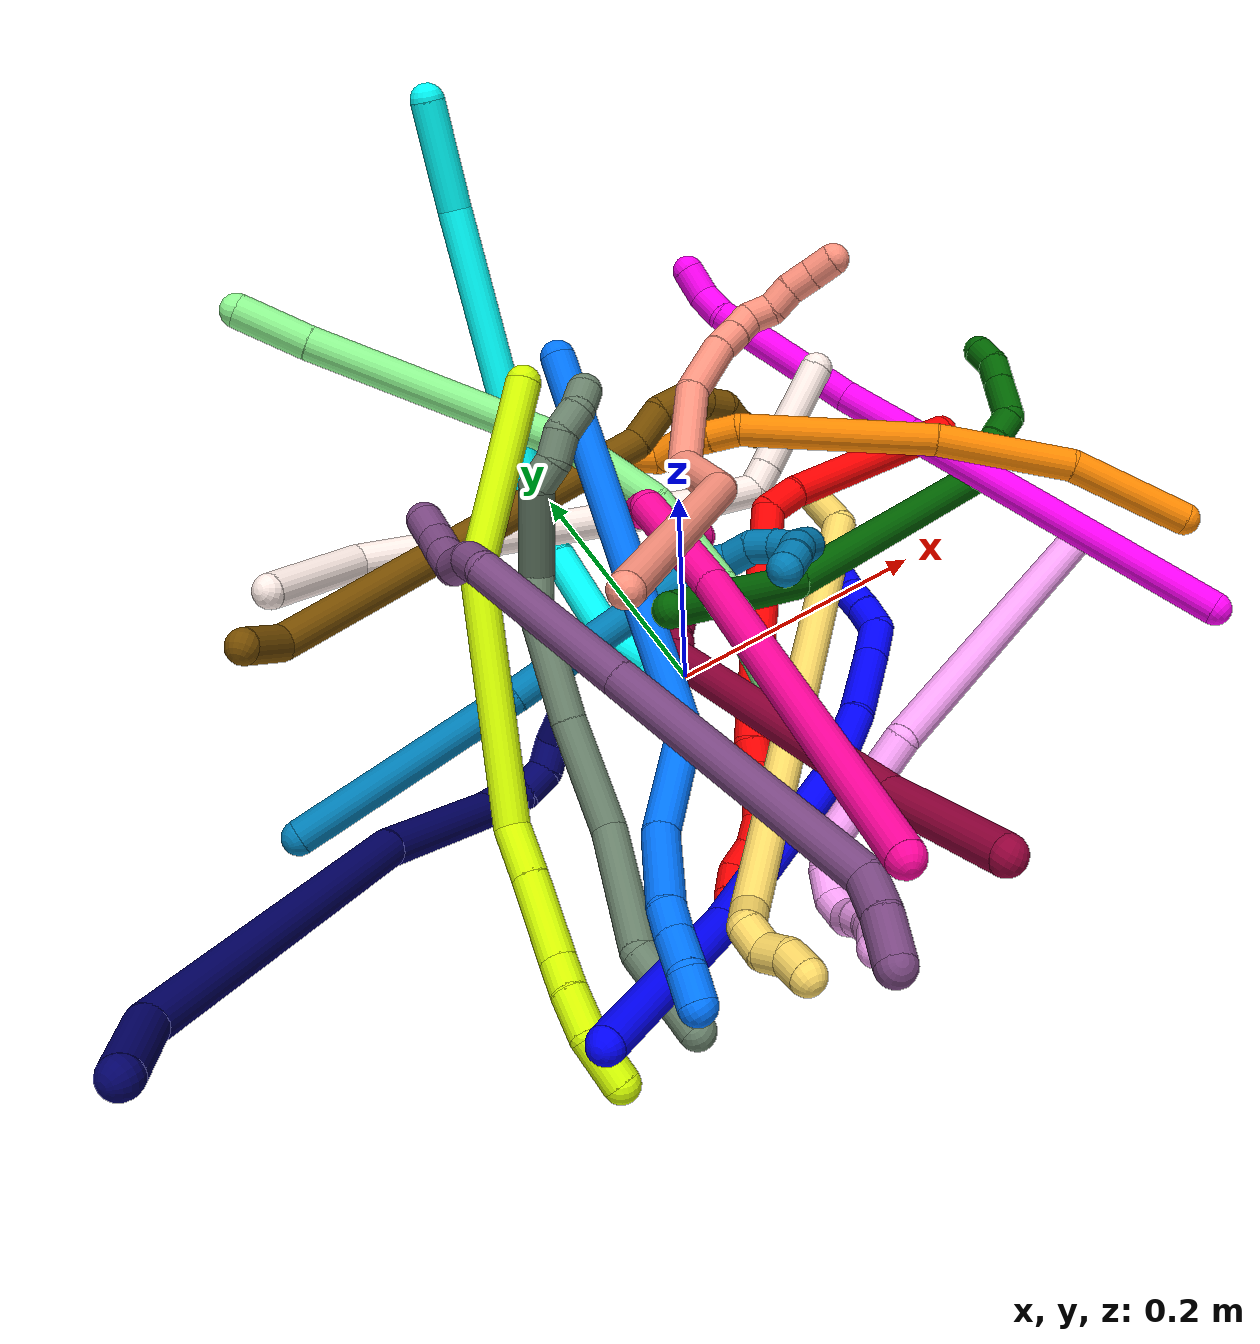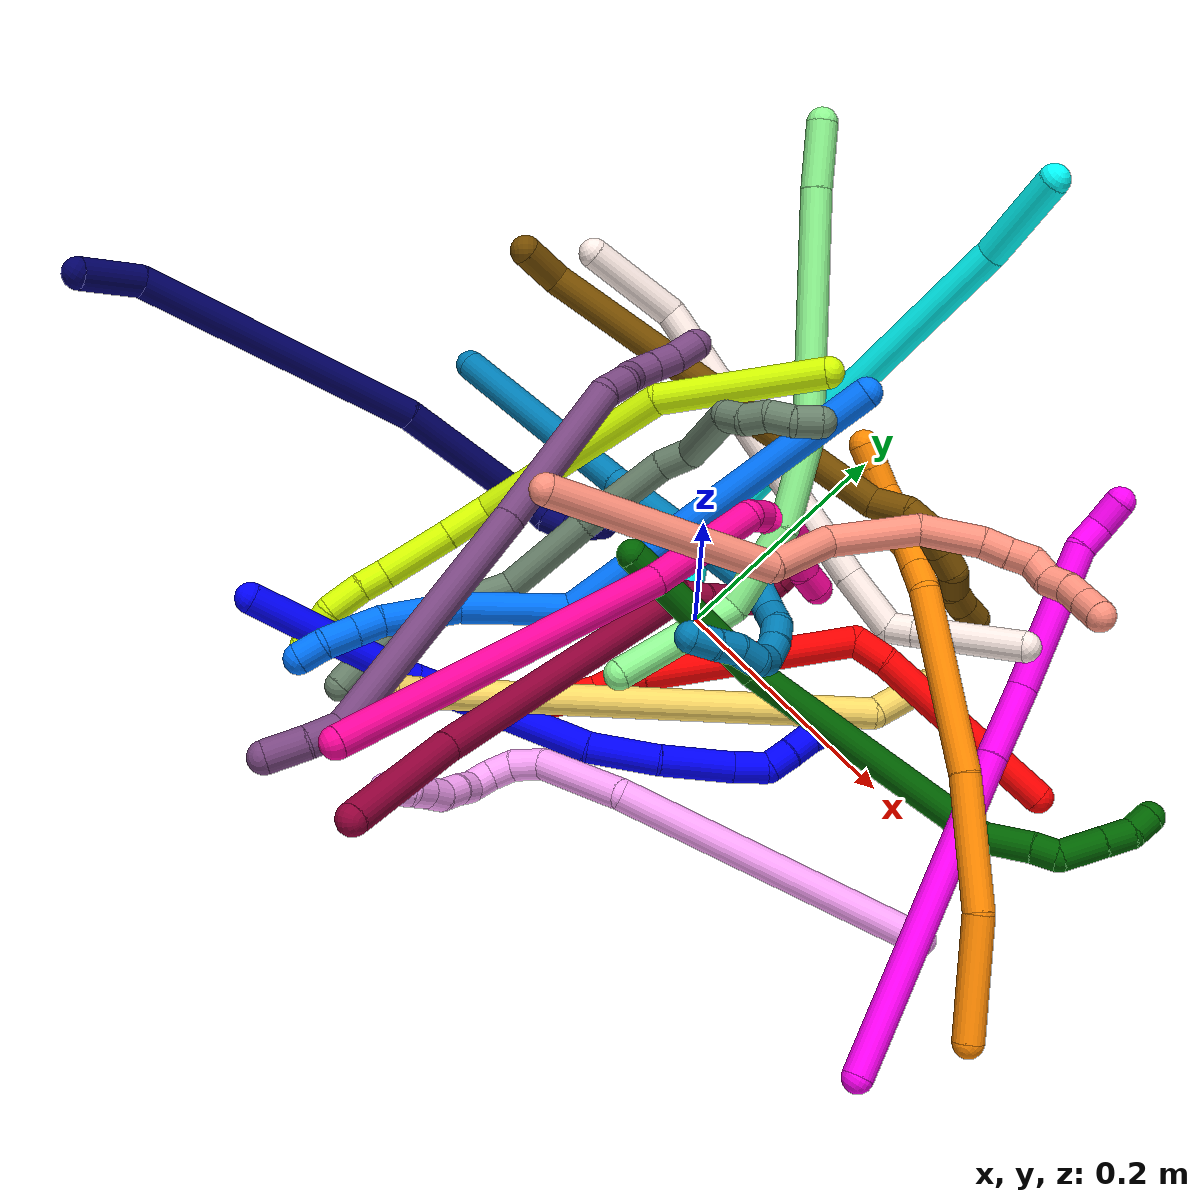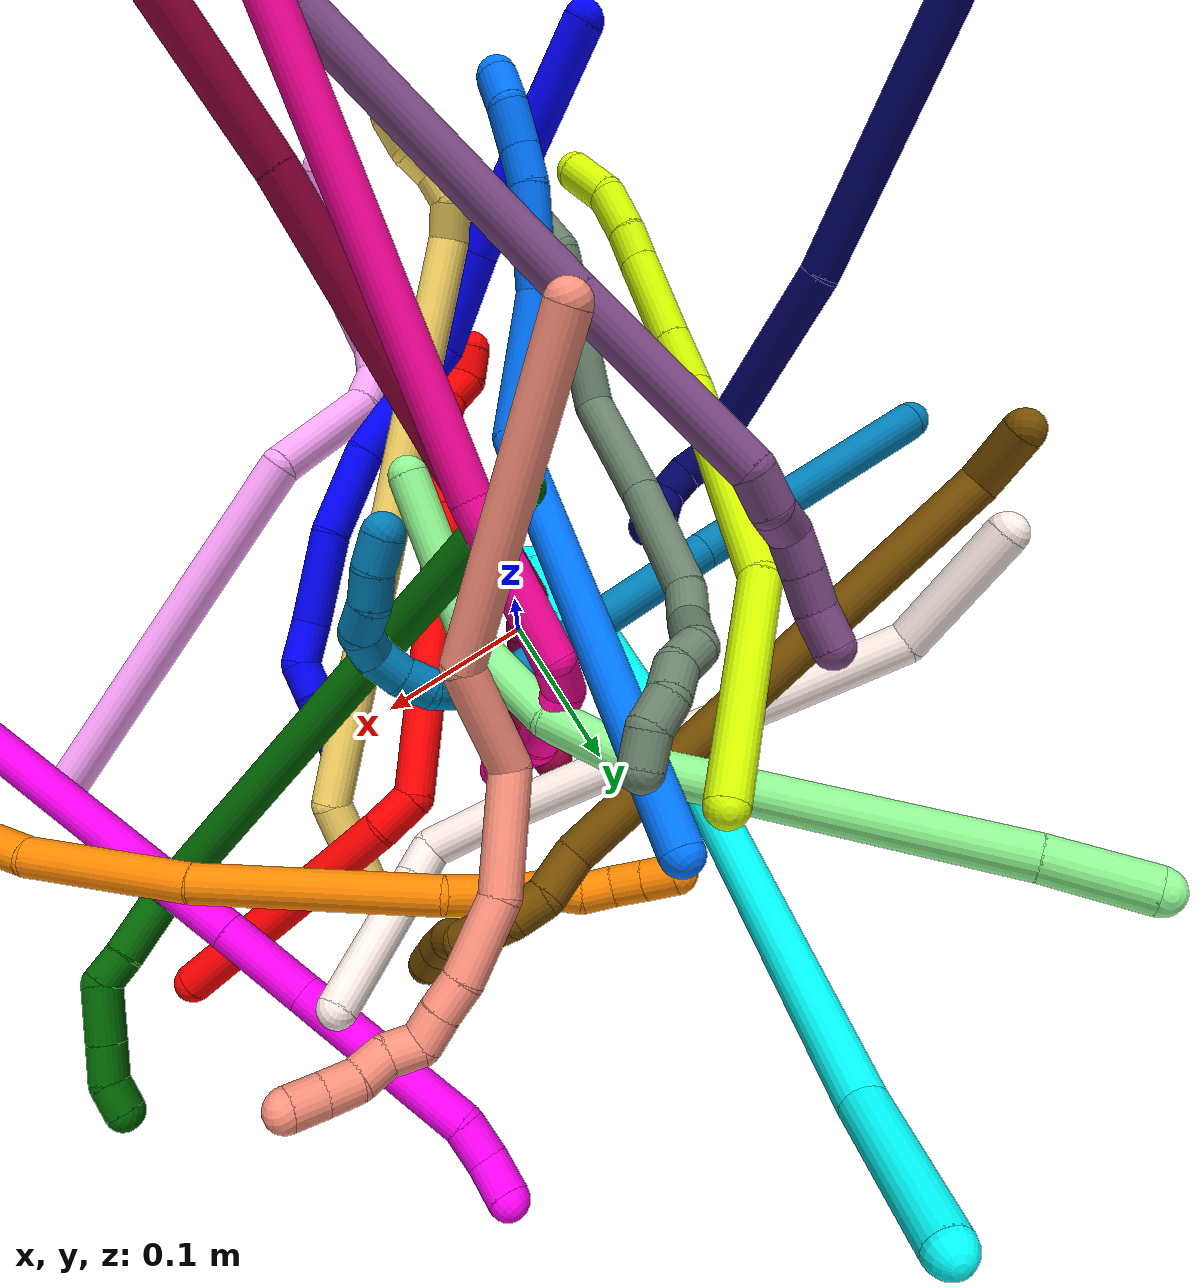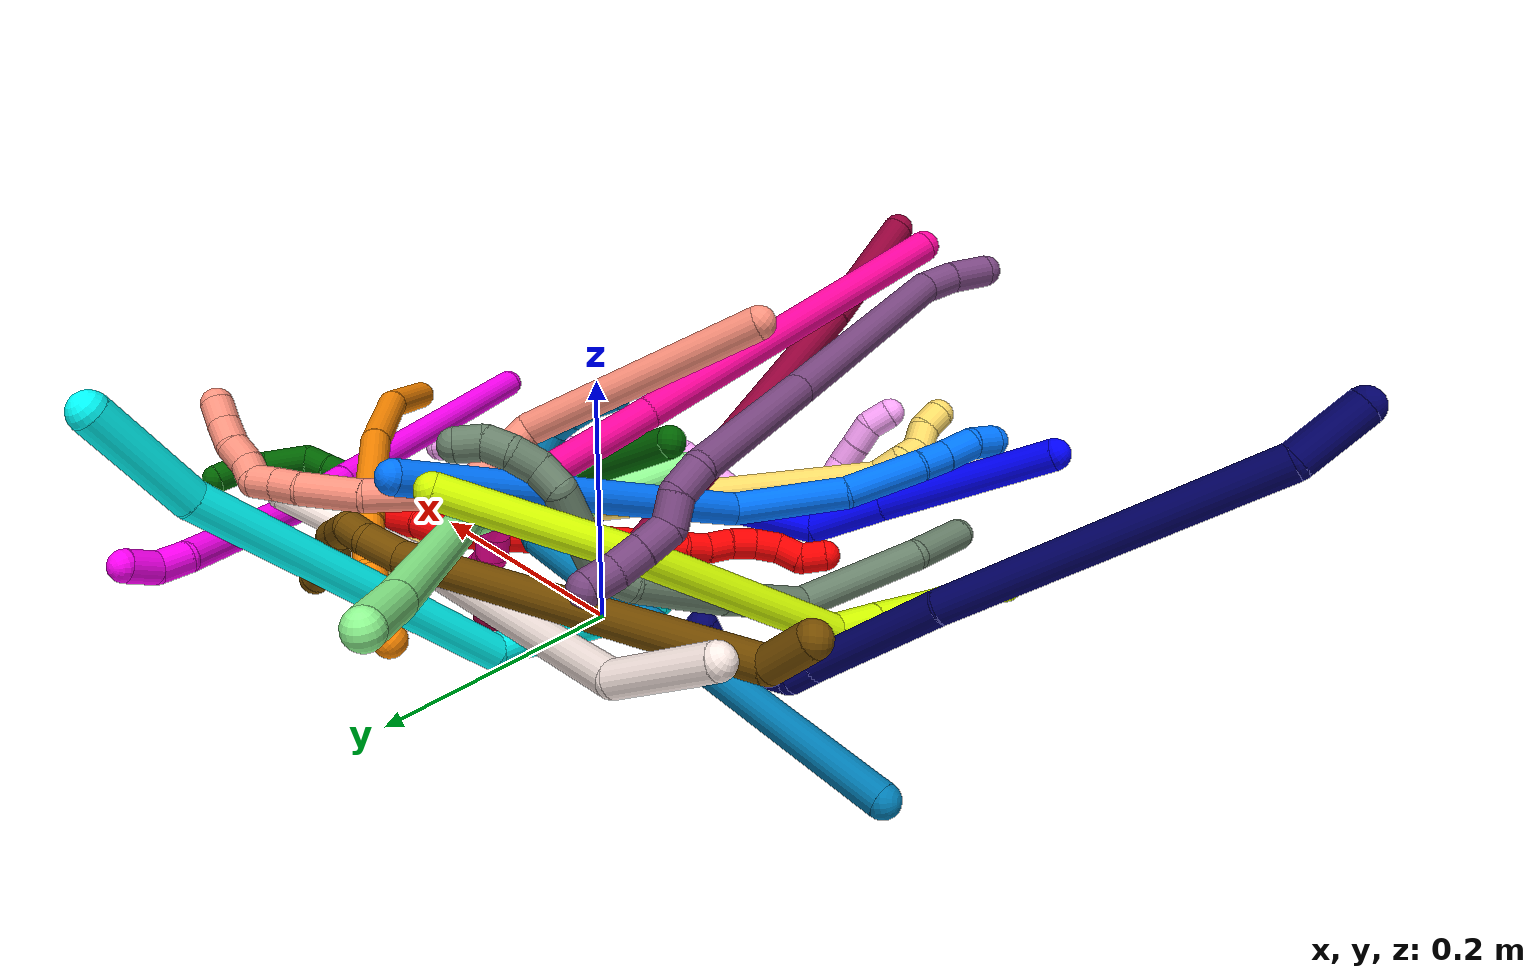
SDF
<sdf version="1.7">
 <world name="default">
  <plugin name="TubeGeneratorPlugin" filename="libtube_generator_plugin.so"/>
  <model name="photoneo_s_sensor">
   <static>1</static>
   <pose>0 0 2 1.57079 1.57079 3.14159</pose>
   <link name="link">
    <inertial><mass>0.1</mass></inertial>
    <sensor name="sensor" type="depth">
     <update_rate>30</update_rate>
     <camera>
      <horizontal_fov>1.22</horizontal_fov>
      <image><width>1920</width><height>1200</height><format>B8G8R8</format></image>
      <clip><near>0.1</near><far>4</far></clip>
      <depth_camera><output>points</output></depth_camera>
     </camera>
     <plugin name="camera_plugin" filename="libgazebo_ros_depth_camera.so">
      <baseline>0.2</baseline>
      <alwaysOn>1</alwaysOn>
      <updateRate>0.0</updateRate>
      <cameraName>camera_ir</cameraName>
      <imageTopicName>/camera/color/image_raw</imageTopicName>
      <cameraInfoTopicName>/camera/color/camera_info</cameraInfoTopicName>
      <depthImageTopicName>/camera/depth/image_raw</depthImageTopicName>
      <depthImageCameraInfoTopicName>/camera/depth/camera_info</depthImageCameraInfoTopicName>
      <pointCloudTopicName>/camera/depth/points</pointCloudTopicName>
      <frameName>fr_optical</frameName>
      <pointCloudCutoff>0.1</pointCloudCutoff>
      <pointCloudCutoffMax>2.0</pointCloudCutoffMax>
      <distortionK1>0</distortionK1>
      <distortionK2>0</distortionK2>
      <distortionK3>0</distortionK3>
      <distortionT1>0</distortionT1>
      <distortionT2>0</distortionT2>
      <CxPrime>0</CxPrime>
      <Cx>0</Cx>
      <Cy>0</Cy>
      <focalLength>0</focalLength>
      <hackBaseline>0</hackBaseline>
     </plugin>
    </sensor>
   </link>
  </model>
  <gravity>0 0 -9.8</gravity>
  <magnetic_field>6e-06 2.3e-05 -4.2e-05</magnetic_field>
  <atmosphere type="adiabatic"/>
  <physics name="default_physics" default="0" type="ode">
   <max_step_size>0.003</max_step_size>
   <real_time_factor>1</real_time_factor>
   <real_time_update_rate>1000</real_time_update_rate>
   <max_contacts>10000</max_contacts>
   <ode>
    <solver>
     <type>quick</type>
     <iters>100</iters>
     <sor>1.3</sor>
     <use_dynamic_moi_rescaling>0</use_dynamic_moi_rescaling>
    </solver>
    <constraints>
     <contact_max_correcting_vel>0</contact_max_correcting_vel>
     <contact_surface_layer>0.001</contact_surface_layer>
     <cfm>0</cfm>
     <erp>0.2</erp>
    </constraints>
   </ode>
  </physics>
  <scene><ambient>0.4 0.4 0.4 1</ambient><background>0.7 0.7 0.7 1</background><shadows>0</shadows></scene>
  <audio><device>default</device></audio>
  <spherical_coordinates>
   <surface_model>EARTH_WGS84</surface_model>
   <latitude_deg>0</latitude_deg>
   <longitude_deg>0</longitude_deg>
   <elevation>0</elevation>
   <heading_deg>0</heading_deg>
  </spherical_coordinates>
  <model name="bin">
   <static>1</static>
   <link name="bottom">
    <collision name="collision-bottom">
     <pose>0 0 -0.01 0 -0 0</pose>
     <geometry><box><size>0.8 0.6 0.02</size></box></geometry>
     <surface>
      <friction><ode><mu>100</mu><mu2>100</mu2></ode></friction>
      <contact><collide_bitmask>65535</collide_bitmask></contact>
     </surface>
    </collision>
   </link>
   <link name="west_wall">
    <collision name="collision-west_wall">
     <pose>-0.41 0 0.1 0 -0 0</pose>
     <geometry><box><size>0.02 0.6 0.2</size></box></geometry>
     <surface>
      <friction><ode><mu>100</mu><mu2>100</mu2></ode></friction>
      <contact><collide_bitmask>65535</collide_bitmask></contact>
     </surface>
    </collision>
   </link>
   <link name="east_wall">
    <collision name="collision-east_wall">
     <pose>0.41 0 0.1 0 -0 0</pose>
     <geometry><box><size>0.02 0.6 0.2</size></box></geometry>
     <surface>
      <friction><ode><mu>100</mu><mu2>100</mu2></ode></friction>
      <contact><collide_bitmask>65535</collide_bitmask></contact>
     </surface>
    </collision>
   </link>
   <link name="south_wall">
    <collision name="collision-south_wall">
     <pose>0 -0.31 0.1 0 -0 0</pose>
     <geometry><box><size>0.8 0.02 0.2</size></box></geometry>
     <surface>
      <friction><ode><mu>100</mu><mu2>100</mu2></ode></friction>
      <contact><collide_bitmask>65535</collide_bitmask></contact>
     </surface>
    </collision>
   </link>
   <link name="north_wall">
    <collision name="collision-north_wall">
     <pose>0 0.31 0.1 0 -0 0</pose>
     <geometry><box><size>0.8 0.02 0.2</size></box></geometry>
     <surface>
      <friction><ode><mu>100</mu><mu2>100</mu2></ode></friction>
      <contact><collide_bitmask>65535</collide_bitmask></contact>
     </surface>
    </collision>
   </link>
  </model>
  <model name="1">
   <static>0</static>
   <link name="1">
    <collision name="collision-cylinder-e_1_1_4">
     <pose>0.009241 0.002889 -0.070736 -3.10077 0.129797 -2.53294</pose>
     <geometry><cylinder><radius>0.0125</radius><length>0.142792</length></cylinder></geometry>
     <surface>
      <friction><ode><mu>1.16</mu><mu2>1.16</mu2><slip1>0</slip1><slip2>0</slip2></ode></friction>
      <contact><ode><kp>1e+06</kp><kd>1</kd><max_vel>0</max_vel><min_depth>0.001</min_depth></ode></contact>
     </surface>
    </collision>
    <visual name="visual-cylinder-e_1_1_4">
     <pose>0.009241 0.002889 -0.070736 -3.10077 0.129797 -2.53294</pose>
     <geometry><cylinder><radius>0.0125</radius><length>0.142792</length></cylinder></geometry>
     <material><ambient>0 0 1 1</ambient></material>
    </visual>
    <collision name="collision-cylinder-e_2_4_5">
     <pose>0.021598 0.009668 -0.172392 -3.01645 0.099661 -1.34458</pose>
     <geometry><cylinder><radius>0.0125</radius><length>0.062638</length></cylinder></geometry>
     <surface>
      <friction><ode><mu>1.16</mu><mu2>1.16</mu2><slip1>0</slip1><slip2>0</slip2></ode></friction>
      <contact><ode><kp>1e+06</kp><kd>1</kd><max_vel>0</max_vel><min_depth>0.001</min_depth></ode></contact>
     </surface>
    </collision>
    <visual name="visual-cylinder-e_2_4_5">
     <pose>0.021598 0.009668 -0.172392 -3.01645 0.099661 -1.34458</pose>
     <geometry><cylinder><radius>0.0125</radius><length>0.062638</length></cylinder></geometry>
     <material><ambient>0 0 1 1</ambient></material>
    </visual>
    <collision name="collision-cylinder-e_3_5_6">
     <pose>0.050846 0.022088 -0.237975 -2.90028 0.63191 -2.43128</pose>
     <geometry><cylinder><radius>0.0125</radius><length>0.088479</length></cylinder></geometry>
     <surface>
      <friction><ode><mu>1.16</mu><mu2>1.16</mu2><slip1>0</slip1><slip2>0</slip2></ode></friction>
      <contact><ode><kp>1e+06</kp><kd>1</kd><max_vel>0</max_vel><min_depth>0.001</min_depth></ode></contact>
     </surface>
    </collision>
    <visual name="visual-cylinder-e_3_5_6">
     <pose>0.050846 0.022088 -0.237975 -2.90028 0.63191 -2.43128</pose>
     <geometry><cylinder><radius>0.0125</radius><length>0.088479</length></cylinder></geometry>
     <material><ambient>0 0 1 1</ambient></material>
    </visual>
    <collision name="collision-cylinder-e_4_6_7">
     <pose>0.089277 0.041057 -0.295782 -2.7179 0.451105 -1.6355</pose>
     <geometry><cylinder><radius>0.0125</radius><length>0.056422</length></cylinder></geometry>
     <surface>
      <friction><ode><mu>1.16</mu><mu2>1.16</mu2><slip1>0</slip1><slip2>0</slip2></ode></friction>
      <contact><ode><kp>1e+06</kp><kd>1</kd><max_vel>0</max_vel><min_depth>0.001</min_depth></ode></contact>
     </surface>
    </collision>
    <visual name="visual-cylinder-e_4_6_7">
     <pose>0.089277 0.041057 -0.295782 -2.7179 0.451105 -1.6355</pose>
     <geometry><cylinder><radius>0.0125</radius><length>0.056422</length></cylinder></geometry>
     <material><ambient>0 0 1 1</ambient></material>
    </visual>
    <collision name="collision-cylinder-e_5_7_8">
     <pose>0.10803 0.063651 -0.345298 -2.70969 0.218711 -0.928079</pose>
     <geometry><cylinder><radius>0.0125</radius><length>0.059494</length></cylinder></geometry>
     <surface>
      <friction><ode><mu>1.16</mu><mu2>1.16</mu2><slip1>0</slip1><slip2>0</slip2></ode></friction>
      <contact><ode><kp>1e+06</kp><kd>1</kd><max_vel>0</max_vel><min_depth>0.001</min_depth></ode></contact>
     </surface>
    </collision>
    <visual name="visual-cylinder-e_5_7_8">
     <pose>0.10803 0.063651 -0.345298 -2.70969 0.218711 -0.928079</pose>
     <geometry><cylinder><radius>0.0125</radius><length>0.059494</length></cylinder></geometry>
     <material><ambient>0 0 1 1</ambient></material>
    </visual>
    <collision name="collision-cylinder-e_6_8_9">
     <pose>0.119732 0.082973 -0.382546 -2.55891 0.382988 -1.14782</pose>
     <geometry><cylinder><radius>0.0125</radius><length>0.028084</length></cylinder></geometry>
     <surface>
      <friction><ode><mu>1.16</mu><mu2>1.16</mu2><slip1>0</slip1><slip2>0</slip2></ode></friction>
      <contact><ode><kp>1e+06</kp><kd>1</kd><max_vel>0</max_vel><min_depth>0.001</min_depth></ode></contact>
     </surface>
    </collision>
    <visual name="visual-cylinder-e_6_8_9">
     <pose>0.119732 0.082973 -0.382546 -2.55891 0.382988 -1.14782</pose>
     <geometry><cylinder><radius>0.0125</radius><length>0.028084</length></cylinder></geometry>
     <material><ambient>0 0 1 1</ambient></material>
    </visual>
    <collision name="collision-cylinder-e_7_9_10">
     <pose>0.123751 0.09912 -0.399004 -2.12703 -0.115646 0.207556</pose>
     <geometry><cylinder><radius>0.0125</radius><length>0.021288</length></cylinder></geometry>
     <surface>
      <friction><ode><mu>1.16</mu><mu2>1.16</mu2><slip1>0</slip1><slip2>0</slip2></ode></friction>
      <contact><ode><kp>1e+06</kp><kd>1</kd><max_vel>0</max_vel><min_depth>0.001</min_depth></ode></contact>
     </surface>
    </collision>
    <visual name="visual-cylinder-e_7_9_10">
     <pose>0.123751 0.09912 -0.399004 -2.12703 -0.115646 0.207556</pose>
     <geometry><cylinder><radius>0.0125</radius><length>0.021288</length></cylinder></geometry>
     <material><ambient>0 0 1 1</ambient></material>
    </visual>
    <collision name="collision-cylinder-e_8_10_11">
     <pose>0.120486 0.116552 -0.40989 -2.13115 -0.201373 0.361332</pose>
     <geometry><cylinder><radius>0.0125</radius><length>0.02037</length></cylinder></geometry>
     <surface>
      <friction><ode><mu>1.16</mu><mu2>1.16</mu2><slip1>0</slip1><slip2>0</slip2></ode></friction>
      <contact><ode><kp>1e+06</kp><kd>1</kd><max_vel>0</max_vel><min_depth>0.001</min_depth></ode></contact>
     </surface>
    </collision>
    <visual name="visual-cylinder-e_8_10_11">
     <pose>0.120486 0.116552 -0.40989 -2.13115 -0.201373 0.361332</pose>
     <geometry><cylinder><radius>0.0125</radius><length>0.02037</length></cylinder></geometry>
     <material><ambient>0 0 1 1</ambient></material>
    </visual>
    <collision name="collision-cylinder-e_9_11_2">
     <pose>0.116881 0.132814 -0.421591 -2.25714 -0.154024 0.323091</pose>
     <geometry><cylinder><radius>0.0125</radius><length>0.020431</length></cylinder></geometry>
     <surface>
      <friction><ode><mu>1.16</mu><mu2>1.16</mu2><slip1>0</slip1><slip2>0</slip2></ode></friction>
      <contact><ode><kp>1e+06</kp><kd>1</kd><max_vel>0</max_vel><min_depth>0.001</min_depth></ode></contact>
     </surface>
    </collision>
    <visual name="visual-cylinder-e_9_11_2">
     <pose>0.116881 0.132814 -0.421591 -2.25714 -0.154024 0.323091</pose>
     <geometry><cylinder><radius>0.0125</radius><length>0.020431</length></cylinder></geometry>
     <material><ambient>0 0 1 1</ambient></material>
    </visual>
    <collision name="collision-sphere-2">
     <pose>0.115314 0.140623 -0.427988 0 -0 0</pose>
     <geometry><sphere><radius>0.0125</radius></sphere></geometry>
     <surface>
      <friction><ode><mu>1.16</mu><mu2>1.16</mu2><slip1>0</slip1><slip2>0</slip2></ode></friction>
      <contact><ode><kp>1e+06</kp><kd>1</kd><max_vel>0</max_vel><min_depth>0.001</min_depth></ode></contact>
     </surface>
    </collision>
    <visual name="visual-sphere-2">
     <pose>0.115314 0.140623 -0.427988 0 -0 0</pose>
     <geometry><sphere><radius>0.0125</radius></sphere></geometry>
     <material><ambient>0 0 1 1</ambient></material>
    </visual>
    <collision name="collision-sphere-11">
     <pose>0.118449 0.125005 -0.415194 0 -0 0</pose>
     <geometry><sphere><radius>0.0125</radius></sphere></geometry>
     <surface>
      <friction><ode><mu>1.16</mu><mu2>1.16</mu2><slip1>0</slip1><slip2>0</slip2></ode></friction>
      <contact><ode><kp>1e+06</kp><kd>1</kd><max_vel>0</max_vel><min_depth>0.001</min_depth></ode></contact>
     </surface>
    </collision>
    <visual name="visual-sphere-11">
     <pose>0.118449 0.125005 -0.415194 0 -0 0</pose>
     <geometry><sphere><radius>0.0125</radius></sphere></geometry>
     <material><ambient>0 0 1 1</ambient></material>
    </visual>
    <collision name="collision-sphere-10">
     <pose>0.122523 0.108099 -0.404586 0 -0 0</pose>
     <geometry><sphere><radius>0.0125</radius></sphere></geometry>
     <surface>
      <friction><ode><mu>1.16</mu><mu2>1.16</mu2><slip1>0</slip1><slip2>0</slip2></ode></friction>
      <contact><ode><kp>1e+06</kp><kd>1</kd><max_vel>0</max_vel><min_depth>0.001</min_depth></ode></contact>
     </surface>
    </collision>
    <visual name="visual-sphere-10">
     <pose>0.122523 0.108099 -0.404586 0 -0 0</pose>
     <geometry><sphere><radius>0.0125</radius></sphere></geometry>
     <material><ambient>0 0 1 1</ambient></material>
    </visual>
    <collision name="collision-sphere-9">
     <pose>0.124979 0.09014 -0.393421 0 -0 0</pose>
     <geometry><sphere><radius>0.0125</radius></sphere></geometry>
     <surface>
      <friction><ode><mu>1.16</mu><mu2>1.16</mu2><slip1>0</slip1><slip2>0</slip2></ode></friction>
      <contact><ode><kp>1e+06</kp><kd>1</kd><max_vel>0</max_vel><min_depth>0.001</min_depth></ode></contact>
     </surface>
    </collision>
    <visual name="visual-sphere-9">
     <pose>0.124979 0.09014 -0.393421 0 -0 0</pose>
     <geometry><sphere><radius>0.0125</radius></sphere></geometry>
     <material><ambient>0 0 1 1</ambient></material>
    </visual>
    <collision name="collision-sphere-4">
     <pose>0.018482 0.005778 -0.141473 0 -0 0</pose>
     <geometry><sphere><radius>0.0125</radius></sphere></geometry>
     <surface>
      <friction><ode><mu>1.16</mu><mu2>1.16</mu2><slip1>0</slip1><slip2>0</slip2></ode></friction>
      <contact><ode><kp>1e+06</kp><kd>1</kd><max_vel>0</max_vel><min_depth>0.001</min_depth></ode></contact>
     </surface>
    </collision>
    <visual name="visual-sphere-4">
     <pose>0.018482 0.005778 -0.141473 0 -0 0</pose>
     <geometry><sphere><radius>0.0125</radius></sphere></geometry>
     <material><ambient>0 0 1 1</ambient></material>
    </visual>
    <collision name="collision-sphere-1">
     <geometry><sphere><radius>0.0125</radius></sphere></geometry>
     <surface>
      <friction><ode><mu>1.16</mu><mu2>1.16</mu2><slip1>0</slip1><slip2>0</slip2></ode></friction>
      <contact><ode><kp>1e+06</kp><kd>1</kd><max_vel>0</max_vel><min_depth>0.001</min_depth></ode></contact>
     </surface>
    </collision>
    <visual name="visual-sphere-1">
     <geometry><sphere><radius>0.0125</radius></sphere></geometry>
     <material><ambient>0 0 1 1</ambient></material>
    </visual>
    <collision name="collision-sphere-8">
     <pose>0.114484 0.075806 -0.37167 0 -0 0</pose>
     <geometry><sphere><radius>0.0125</radius></sphere></geometry>
     <surface>
      <friction><ode><mu>1.16</mu><mu2>1.16</mu2><slip1>0</slip1><slip2>0</slip2></ode></friction>
      <contact><ode><kp>1e+06</kp><kd>1</kd><max_vel>0</max_vel><min_depth>0.001</min_depth></ode></contact>
     </surface>
    </collision>
    <visual name="visual-sphere-8">
     <pose>0.114484 0.075806 -0.37167 0 -0 0</pose>
     <geometry><sphere><radius>0.0125</radius></sphere></geometry>
     <material><ambient>0 0 1 1</ambient></material>
    </visual>
    <collision name="collision-sphere-5">
     <pose>0.024714 0.013557 -0.203312 0 -0 0</pose>
     <geometry><sphere><radius>0.0125</radius></sphere></geometry>
     <surface>
      <friction><ode><mu>1.16</mu><mu2>1.16</mu2><slip1>0</slip1><slip2>0</slip2></ode></friction>
      <contact><ode><kp>1e+06</kp><kd>1</kd><max_vel>0</max_vel><min_depth>0.001</min_depth></ode></contact>
     </surface>
    </collision>
    <visual name="visual-sphere-5">
     <pose>0.024714 0.013557 -0.203312 0 -0 0</pose>
     <geometry><sphere><radius>0.0125</radius></sphere></geometry>
     <material><ambient>0 0 1 1</ambient></material>
    </visual>
    <collision name="collision-sphere-6">
     <pose>0.076978 0.030619 -0.272638 0 -0 0</pose>
     <geometry><sphere><radius>0.0125</radius></sphere></geometry>
     <surface>
      <friction><ode><mu>1.16</mu><mu2>1.16</mu2><slip1>0</slip1><slip2>0</slip2></ode></friction>
      <contact><ode><kp>1e+06</kp><kd>1</kd><max_vel>0</max_vel><min_depth>0.001</min_depth></ode></contact>
     </surface>
    </collision>
    <visual name="visual-sphere-6">
     <pose>0.076978 0.030619 -0.272638 0 -0 0</pose>
     <geometry><sphere><radius>0.0125</radius></sphere></geometry>
     <material><ambient>0 0 1 1</ambient></material>
    </visual>
    <collision name="collision-sphere-7">
     <pose>0.101576 0.051495 -0.318926 0 -0 0</pose>
     <geometry><sphere><radius>0.0125</radius></sphere></geometry>
     <surface>
      <friction><ode><mu>1.16</mu><mu2>1.16</mu2><slip1>0</slip1><slip2>0</slip2></ode></friction>
      <contact><ode><kp>1e+06</kp><kd>1</kd><max_vel>0</max_vel><min_depth>0.001</min_depth></ode></contact>
     </surface>
    </collision>
    <visual name="visual-sphere-7">
     <pose>0.101576 0.051495 -0.318926 0 -0 0</pose>
     <geometry><sphere><radius>0.0125</radius></sphere></geometry>
     <material><ambient>0 0 1 1</ambient></material>
    </visual>
    <inertial>
     <pose>0.05895 0.037208 -0.230775 0 -0 0</pose>
     <mass>0.5</mass>
     <inertia>
      <ixx>-0.000436</ixx>
      <ixy>0</ixy>
      <ixz>0</ixz>
      <iyy>2.6e-05</iyy>
      <iyz>0</iyz>
      <izz>-0.000161</izz>
     </inertia>
    </inertial>
   </link>
   <pose>-0.215657 -0.265855 0.127899 0.561567 -0.805591 -0.225946</pose>
  </model>
  <model name="2">
   <static>0</static>
   <link name="2">
    <collision name="collision-cylinder-e_1_1_4">
     <pose>-0.045443 -0.034044 0.056692 0.540791 -0.602076 -0.171694</pose>
     <geometry><cylinder><radius>0.0125</radius><length>0.160476</length></cylinder></geometry>
     <surface>
      <friction><ode><mu>1.16</mu><mu2>1.16</mu2><slip1>0</slip1><slip2>0</slip2></ode></friction>
      <contact><ode><kp>1e+06</kp><kd>1</kd><max_vel>0</max_vel><min_depth>0.001</min_depth></ode></contact>
     </surface>
    </collision>
    <visual name="visual-cylinder-e_1_1_4">
     <pose>-0.045443 -0.034044 0.056692 0.540791 -0.602076 -0.171694</pose>
     <geometry><cylinder><radius>0.0125</radius><length>0.160476</length></cylinder></geometry>
     <material><ambient>1 0 0 1</ambient></material>
    </visual>
    <collision name="collision-cylinder-e_2_4_5">
     <pose>-0.100859 -0.072039 0.122672 0.402217 -0.779429 -0.167073</pose>
     <geometry><cylinder><radius>0.0125</radius><length>0.028378</length></cylinder></geometry>
     <surface>
      <friction><ode><mu>1.16</mu><mu2>1.16</mu2><slip1>0</slip1><slip2>0</slip2></ode></friction>
      <contact><ode><kp>1e+06</kp><kd>1</kd><max_vel>0</max_vel><min_depth>0.001</min_depth></ode></contact>
     </surface>
    </collision>
    <visual name="visual-cylinder-e_2_4_5">
     <pose>-0.100859 -0.072039 0.122672 0.402217 -0.779429 -0.167073</pose>
     <geometry><cylinder><radius>0.0125</radius><length>0.028378</length></cylinder></geometry>
     <material><ambient>1 0 0 1</ambient></material>
    </visual>
    <collision name="collision-cylinder-e_3_5_6">
     <pose>-0.192776 -0.094385 0.129532 1.70201 -1.34812 -1.47799</pose>
     <geometry><cylinder><radius>0.0125</radius><length>0.168037</length></cylinder></geometry>
     <surface>
      <friction><ode><mu>1.16</mu><mu2>1.16</mu2><slip1>0</slip1><slip2>0</slip2></ode></friction>
      <contact><ode><kp>1e+06</kp><kd>1</kd><max_vel>0</max_vel><min_depth>0.001</min_depth></ode></contact>
     </surface>
    </collision>
    <visual name="visual-cylinder-e_3_5_6">
     <pose>-0.192776 -0.094385 0.129532 1.70201 -1.34812 -1.47799</pose>
     <geometry><cylinder><radius>0.0125</radius><length>0.168037</length></cylinder></geometry>
     <material><ambient>1 0 0 1</ambient></material>
    </visual>
    <collision name="collision-cylinder-e_4_6_7">
     <pose>-0.285558 -0.114702 0.126561 1.84654 -1.38857 -1.66671</pose>
     <geometry><cylinder><radius>0.0125</radius><length>0.02204</length></cylinder></geometry>
     <surface>
      <friction><ode><mu>1.16</mu><mu2>1.16</mu2><slip1>0</slip1><slip2>0</slip2></ode></friction>
      <contact><ode><kp>1e+06</kp><kd>1</kd><max_vel>0</max_vel><min_depth>0.001</min_depth></ode></contact>
     </surface>
    </collision>
    <visual name="visual-cylinder-e_4_6_7">
     <pose>-0.285558 -0.114702 0.126561 1.84654 -1.38857 -1.66671</pose>
     <geometry><cylinder><radius>0.0125</radius><length>0.02204</length></cylinder></geometry>
     <material><ambient>1 0 0 1</ambient></material>
    </visual>
    <collision name="collision-cylinder-e_5_7_8">
     <pose>-0.306146 -0.117605 0.123247 2.80109 -1.27809 -2.68686</pose>
     <geometry><cylinder><radius>0.0125</radius><length>0.020368</length></cylinder></geometry>
     <surface>
      <friction><ode><mu>1.16</mu><mu2>1.16</mu2><slip1>0</slip1><slip2>0</slip2></ode></friction>
      <contact><ode><kp>1e+06</kp><kd>1</kd><max_vel>0</max_vel><min_depth>0.001</min_depth></ode></contact>
     </surface>
    </collision>
    <visual name="visual-cylinder-e_5_7_8">
     <pose>-0.306146 -0.117605 0.123247 2.80109 -1.27809 -2.68686</pose>
     <geometry><cylinder><radius>0.0125</radius><length>0.020368</length></cylinder></geometry>
     <material><ambient>1 0 0 1</ambient></material>
    </visual>
    <collision name="collision-cylinder-e_6_8_9">
     <pose>-0.324944 -0.122734 0.118523 2.0111 -1.10171 -1.53876</pose>
     <geometry><cylinder><radius>0.0125</radius><length>0.020285</length></cylinder></geometry>
     <surface>
      <friction><ode><mu>1.16</mu><mu2>1.16</mu2><slip1>0</slip1><slip2>0</slip2></ode></friction>
      <contact><ode><kp>1e+06</kp><kd>1</kd><max_vel>0</max_vel><min_depth>0.001</min_depth></ode></contact>
     </surface>
    </collision>
    <visual name="visual-cylinder-e_6_8_9">
     <pose>-0.324944 -0.122734 0.118523 2.0111 -1.10171 -1.53876</pose>
     <geometry><cylinder><radius>0.0125</radius><length>0.020285</length></cylinder></geometry>
     <material><ambient>1 0 0 1</ambient></material>
    </visual>
    <collision name="collision-cylinder-e_7_9_10">
     <pose>-0.343651 -0.129343 0.115562 1.95892 -1.30217 -1.6968</pose>
     <geometry><cylinder><radius>0.0125</radius><length>0.02004</length></cylinder></geometry>
     <surface>
      <friction><ode><mu>1.16</mu><mu2>1.16</mu2><slip1>0</slip1><slip2>0</slip2></ode></friction>
      <contact><ode><kp>1e+06</kp><kd>1</kd><max_vel>0</max_vel><min_depth>0.001</min_depth></ode></contact>
     </surface>
    </collision>
    <visual name="visual-cylinder-e_7_9_10">
     <pose>-0.343651 -0.129343 0.115562 1.95892 -1.30217 -1.6968</pose>
     <geometry><cylinder><radius>0.0125</radius><length>0.02004</length></cylinder></geometry>
     <material><ambient>1 0 0 1</ambient></material>
    </visual>
    <collision name="collision-cylinder-e_8_10_11">
     <pose>-0.363081 -0.133616 0.116032 0.886897 -1.33607 -0.717199</pose>
     <geometry><cylinder><radius>0.0125</radius><length>0.020089</length></cylinder></geometry>
     <surface>
      <friction><ode><mu>1.16</mu><mu2>1.16</mu2><slip1>0</slip1><slip2>0</slip2></ode></friction>
      <contact><ode><kp>1e+06</kp><kd>1</kd><max_vel>0</max_vel><min_depth>0.001</min_depth></ode></contact>
     </surface>
    </collision>
    <visual name="visual-cylinder-e_8_10_11">
     <pose>-0.363081 -0.133616 0.116032 0.886897 -1.33607 -0.717199</pose>
     <geometry><cylinder><radius>0.0125</radius><length>0.020089</length></cylinder></geometry>
     <material><ambient>1 0 0 1</ambient></material>
    </visual>
    <collision name="collision-cylinder-e_9_11_12">
     <pose>-0.38177 -0.135722 0.122326 0.061247 -1.07472 -0.036501</pose>
     <geometry><cylinder><radius>0.0125</radius><length>0.020284</length></cylinder></geometry>
     <surface>
      <friction><ode><mu>1.16</mu><mu2>1.16</mu2><slip1>0</slip1><slip2>0</slip2></ode></friction>
      <contact><ode><kp>1e+06</kp><kd>1</kd><max_vel>0</max_vel><min_depth>0.001</min_depth></ode></contact>
     </surface>
    </collision>
    <visual name="visual-cylinder-e_9_11_12">
     <pose>-0.38177 -0.135722 0.122326 0.061247 -1.07472 -0.036501</pose>
     <geometry><cylinder><radius>0.0125</radius><length>0.020284</length></cylinder></geometry>
     <material><ambient>1 0 0 1</ambient></material>
    </visual>
    <collision name="collision-cylinder-e_10_12_2">
     <pose>-0.399566 -0.140601 0.127618 1.46778 -1.09197 -1.00264</pose>
     <geometry><cylinder><radius>0.0125</radius><length>0.020003</length></cylinder></geometry>
     <surface>
      <friction><ode><mu>1.16</mu><mu2>1.16</mu2><slip1>0</slip1><slip2>0</slip2></ode></friction>
      <contact><ode><kp>1e+06</kp><kd>1</kd><max_vel>0</max_vel><min_depth>0.001</min_depth></ode></contact>
     </surface>
    </collision>
    <visual name="visual-cylinder-e_10_12_2">
     <pose>-0.399566 -0.140601 0.127618 1.46778 -1.09197 -1.00264</pose>
     <geometry><cylinder><radius>0.0125</radius><length>0.020003</length></cylinder></geometry>
     <material><ambient>1 0 0 1</ambient></material>
    </visual>
    <collision name="collision-sphere-2">
     <pose>-0.408443 -0.145185 0.128092 0 -0 0</pose>
     <geometry><sphere><radius>0.0125</radius></sphere></geometry>
     <surface>
      <friction><ode><mu>1.16</mu><mu2>1.16</mu2><slip1>0</slip1><slip2>0</slip2></ode></friction>
      <contact><ode><kp>1e+06</kp><kd>1</kd><max_vel>0</max_vel><min_depth>0.001</min_depth></ode></contact>
     </surface>
    </collision>
    <visual name="visual-sphere-2">
     <pose>-0.408443 -0.145185 0.128092 0 -0 0</pose>
     <geometry><sphere><radius>0.0125</radius></sphere></geometry>
     <material><ambient>1 0 0 1</ambient></material>
    </visual>
    <collision name="collision-sphere-12">
     <pose>-0.390689 -0.136017 0.127145 0 -0 0</pose>
     <geometry><sphere><radius>0.0125</radius></sphere></geometry>
     <surface>
      <friction><ode><mu>1.16</mu><mu2>1.16</mu2><slip1>0</slip1><slip2>0</slip2></ode></friction>
      <contact><ode><kp>1e+06</kp><kd>1</kd><max_vel>0</max_vel><min_depth>0.001</min_depth></ode></contact>
     </surface>
    </collision>
    <visual name="visual-sphere-12">
     <pose>-0.390689 -0.136017 0.127145 0 -0 0</pose>
     <geometry><sphere><radius>0.0125</radius></sphere></geometry>
     <material><ambient>1 0 0 1</ambient></material>
    </visual>
    <collision name="collision-sphere-11">
     <pose>-0.372851 -0.135427 0.117508 0 -0 0</pose>
     <geometry><sphere><radius>0.0125</radius></sphere></geometry>
     <surface>
      <friction><ode><mu>1.16</mu><mu2>1.16</mu2><slip1>0</slip1><slip2>0</slip2></ode></friction>
      <contact><ode><kp>1e+06</kp><kd>1</kd><max_vel>0</max_vel><min_depth>0.001</min_depth></ode></contact>
     </surface>
    </collision>
    <visual name="visual-sphere-11">
     <pose>-0.372851 -0.135427 0.117508 0 -0 0</pose>
     <geometry><sphere><radius>0.0125</radius></sphere></geometry>
     <material><ambient>1 0 0 1</ambient></material>
    </visual>
    <collision name="collision-sphere-10">
     <pose>-0.353312 -0.131805 0.114556 0 -0 0</pose>
     <geometry><sphere><radius>0.0125</radius></sphere></geometry>
     <surface>
      <friction><ode><mu>1.16</mu><mu2>1.16</mu2><slip1>0</slip1><slip2>0</slip2></ode></friction>
      <contact><ode><kp>1e+06</kp><kd>1</kd><max_vel>0</max_vel><min_depth>0.001</min_depth></ode></contact>
     </surface>
    </collision>
    <visual name="visual-sphere-10">
     <pose>-0.353312 -0.131805 0.114556 0 -0 0</pose>
     <geometry><sphere><radius>0.0125</radius></sphere></geometry>
     <material><ambient>1 0 0 1</ambient></material>
    </visual>
    <collision name="collision-sphere-9">
     <pose>-0.333991 -0.126882 0.116569 0 -0 0</pose>
     <geometry><sphere><radius>0.0125</radius></sphere></geometry>
     <surface>
      <friction><ode><mu>1.16</mu><mu2>1.16</mu2><slip1>0</slip1><slip2>0</slip2></ode></friction>
      <contact><ode><kp>1e+06</kp><kd>1</kd><max_vel>0</max_vel><min_depth>0.001</min_depth></ode></contact>
     </surface>
    </collision>
    <visual name="visual-sphere-9">
     <pose>-0.333991 -0.126882 0.116569 0 -0 0</pose>
     <geometry><sphere><radius>0.0125</radius></sphere></geometry>
     <material><ambient>1 0 0 1</ambient></material>
    </visual>
    <collision name="collision-sphere-4">
     <pose>-0.090886 -0.068088 0.113385 0 -0 0</pose>
     <geometry><sphere><radius>0.0125</radius></sphere></geometry>
     <surface>
      <friction><ode><mu>1.16</mu><mu2>1.16</mu2><slip1>0</slip1><slip2>0</slip2></ode></friction>
      <contact><ode><kp>1e+06</kp><kd>1</kd><max_vel>0</max_vel><min_depth>0.001</min_depth></ode></contact>
     </surface>
    </collision>
    <visual name="visual-sphere-4">
     <pose>-0.090886 -0.068088 0.113385 0 -0 0</pose>
     <geometry><sphere><radius>0.0125</radius></sphere></geometry>
     <material><ambient>1 0 0 1</ambient></material>
    </visual>
    <collision name="collision-sphere-1">
     <geometry><sphere><radius>0.0125</radius></sphere></geometry>
     <surface>
      <friction><ode><mu>1.16</mu><mu2>1.16</mu2><slip1>0</slip1><slip2>0</slip2></ode></friction>
      <contact><ode><kp>1e+06</kp><kd>1</kd><max_vel>0</max_vel><min_depth>0.001</min_depth></ode></contact>
     </surface>
    </collision>
    <visual name="visual-sphere-1">
     <geometry><sphere><radius>0.0125</radius></sphere></geometry>
     <material><ambient>1 0 0 1</ambient></material>
    </visual>
    <collision name="collision-sphere-8">
     <pose>-0.315897 -0.118586 0.120477 0 -0 0</pose>
     <geometry><sphere><radius>0.0125</radius></sphere></geometry>
     <surface>
      <friction><ode><mu>1.16</mu><mu2>1.16</mu2><slip1>0</slip1><slip2>0</slip2></ode></friction>
      <contact><ode><kp>1e+06</kp><kd>1</kd><max_vel>0</max_vel><min_depth>0.001</min_depth></ode></contact>
     </surface>
    </collision>
    <visual name="visual-sphere-8">
     <pose>-0.315897 -0.118586 0.120477 0 -0 0</pose>
     <geometry><sphere><radius>0.0125</radius></sphere></geometry>
     <material><ambient>1 0 0 1</ambient></material>
    </visual>
    <collision name="collision-sphere-5">
     <pose>-0.110832 -0.07599 0.13196 0 -0 0</pose>
     <geometry><sphere><radius>0.0125</radius></sphere></geometry>
     <surface>
      <friction><ode><mu>1.16</mu><mu2>1.16</mu2><slip1>0</slip1><slip2>0</slip2></ode></friction>
      <contact><ode><kp>1e+06</kp><kd>1</kd><max_vel>0</max_vel><min_depth>0.001</min_depth></ode></contact>
     </surface>
    </collision>
    <visual name="visual-sphere-5">
     <pose>-0.110832 -0.07599 0.13196 0 -0 0</pose>
     <geometry><sphere><radius>0.0125</radius></sphere></geometry>
     <material><ambient>1 0 0 1</ambient></material>
    </visual>
    <collision name="collision-sphere-6">
     <pose>-0.27472 -0.11278 0.127104 0 -0 0</pose>
     <geometry><sphere><radius>0.0125</radius></sphere></geometry>
     <surface>
      <friction><ode><mu>1.16</mu><mu2>1.16</mu2><slip1>0</slip1><slip2>0</slip2></ode></friction>
      <contact><ode><kp>1e+06</kp><kd>1</kd><max_vel>0</max_vel><min_depth>0.001</min_depth></ode></contact>
     </surface>
    </collision>
    <visual name="visual-sphere-6">
     <pose>-0.27472 -0.11278 0.127104 0 -0 0</pose>
     <geometry><sphere><radius>0.0125</radius></sphere></geometry>
     <material><ambient>1 0 0 1</ambient></material>
    </visual>
    <collision name="collision-sphere-7">
     <pose>-0.296395 -0.116624 0.126017 0 -0 0</pose>
     <geometry><sphere><radius>0.0125</radius></sphere></geometry>
     <surface>
      <friction><ode><mu>1.16</mu><mu2>1.16</mu2><slip1>0</slip1><slip2>0</slip2></ode></friction>
      <contact><ode><kp>1e+06</kp><kd>1</kd><max_vel>0</max_vel><min_depth>0.001</min_depth></ode></contact>
     </surface>
    </collision>
    <visual name="visual-sphere-7">
     <pose>-0.296395 -0.116624 0.126017 0 -0 0</pose>
     <geometry><sphere><radius>0.0125</radius></sphere></geometry>
     <material><ambient>1 0 0 1</ambient></material>
    </visual>
    <inertial>
     <pose>-0.183172 -0.083245 0.10346 0 -0 0</pose>
     <mass>0.5</mass>
     <inertia>
      <ixx>0.000124</ixx>
      <ixy>0</ixy>
      <ixz>0</ixz>
      <iyy>0.000557</iyy>
      <iyz>0</iyz>
      <izz>0.000853</izz>
     </inertia>
    </inertial>
   </link>
   <pose>0.296326 0.08392 0.012449 -1.50734 -0.3551 0.87862</pose>
  </model>
  <model name="3">
   <static>0</static>
   <link name="3">
    <collision name="collision-cylinder-e_1_1_4">
     <pose>6.5e-05 -0.003432 -0.03926 3.05441 0.001657 0.037986</pose>
     <geometry><cylinder><radius>0.0125</radius><length>0.078819</length></cylinder></geometry>
     <surface>
      <friction><ode><mu>1.16</mu><mu2>1.16</mu2><slip1>0</slip1><slip2>0</slip2></ode></friction>
      <contact><ode><kp>1e+06</kp><kd>1</kd><max_vel>0</max_vel><min_depth>0.001</min_depth></ode></contact>
     </surface>
    </collision>
    <visual name="visual-cylinder-e_1_1_4">
     <pose>6.5e-05 -0.003432 -0.03926 3.05441 0.001657 0.037986</pose>
     <geometry><cylinder><radius>0.0125</radius><length>0.078819</length></cylinder></geometry>
     <material><ambient>0.003922 1 0.996078 1</ambient></material>
    </visual>
    <collision name="collision-cylinder-e_2_4_5">
     <pose>-0.008635 -0.043093 -0.196009 2.84248 -0.071176 -0.464046</pose>
     <geometry><cylinder><radius>0.0125</radius><length>0.246522</length></cylinder></geometry>
     <surface>
      <friction><ode><mu>1.16</mu><mu2>1.16</mu2><slip1>0</slip1><slip2>0</slip2></ode></friction>
      <contact><ode><kp>1e+06</kp><kd>1</kd><max_vel>0</max_vel><min_depth>0.001</min_depth></ode></contact>
     </surface>
    </collision>
    <visual name="visual-cylinder-e_2_4_5">
     <pose>-0.008635 -0.043093 -0.196009 2.84248 -0.071176 -0.464046</pose>
     <geometry><cylinder><radius>0.0125</radius><length>0.246522</length></cylinder></geometry>
     <material><ambient>0.003922 1 0.996078 1</ambient></material>
    </visual>
    <collision name="collision-cylinder-e_3_5_6">
     <pose>-0.016253 -0.087351 -0.31939 2.20387 0.114799 0.225921</pose>
     <geometry><cylinder><radius>0.0125</radius><length>0.020046</length></cylinder></geometry>
     <surface>
      <friction><ode><mu>1.16</mu><mu2>1.16</mu2><slip1>0</slip1><slip2>0</slip2></ode></friction>
      <contact><ode><kp>1e+06</kp><kd>1</kd><max_vel>0</max_vel><min_depth>0.001</min_depth></ode></contact>
     </surface>
    </collision>
    <visual name="visual-cylinder-e_3_5_6">
     <pose>-0.016253 -0.087351 -0.31939 2.20387 0.114799 0.225921</pose>
     <geometry><cylinder><radius>0.0125</radius><length>0.020046</length></cylinder></geometry>
     <material><ambient>0.003922 1 0.996078 1</ambient></material>
    </visual>
    <collision name="collision-cylinder-e_4_6_7">
     <pose>-0.01518 -0.124884 -0.349577 2.25967 -0.001957 -0.004146</pose>
     <geometry><cylinder><radius>0.0125</radius><length>0.076443</length></cylinder></geometry>
     <surface>
      <friction><ode><mu>1.16</mu><mu2>1.16</mu2><slip1>0</slip1><slip2>0</slip2></ode></friction>
      <contact><ode><kp>1e+06</kp><kd>1</kd><max_vel>0</max_vel><min_depth>0.001</min_depth></ode></contact>
     </surface>
    </collision>
    <visual name="visual-cylinder-e_4_6_7">
     <pose>-0.01518 -0.124884 -0.349577 2.25967 -0.001957 -0.004146</pose>
     <geometry><cylinder><radius>0.0125</radius><length>0.076443</length></cylinder></geometry>
     <material><ambient>0.003922 1 0.996078 1</ambient></material>
    </visual>
    <collision name="collision-cylinder-e_5_7_8">
     <pose>-0.006158 -0.163719 -0.383959 2.39512 0.584777 1.31072</pose>
     <geometry><cylinder><radius>0.0125</radius><length>0.032955</length></cylinder></geometry>
     <surface>
      <friction><ode><mu>1.16</mu><mu2>1.16</mu2><slip1>0</slip1><slip2>0</slip2></ode></friction>
      <contact><ode><kp>1e+06</kp><kd>1</kd><max_vel>0</max_vel><min_depth>0.001</min_depth></ode></contact>
     </surface>
    </collision>
    <visual name="visual-cylinder-e_5_7_8">
     <pose>-0.006158 -0.163719 -0.383959 2.39512 0.584777 1.31072</pose>
     <geometry><cylinder><radius>0.0125</radius><length>0.032955</length></cylinder></geometry>
     <material><ambient>0.003922 1 0.996078 1</ambient></material>
    </visual>
    <collision name="collision-cylinder-e_6_8_2">
     <pose>7.9e-05 -0.190301 -0.408372 2.26385 -0.126793 -0.268845</pose>
     <geometry><cylinder><radius>0.0125</radius><length>0.045215</length></cylinder></geometry>
     <surface>
      <friction><ode><mu>1.16</mu><mu2>1.16</mu2><slip1>0</slip1><slip2>0</slip2></ode></friction>
      <contact><ode><kp>1e+06</kp><kd>1</kd><max_vel>0</max_vel><min_depth>0.001</min_depth></ode></contact>
     </surface>
    </collision>
    <visual name="visual-cylinder-e_6_8_2">
     <pose>7.9e-05 -0.190301 -0.408372 2.26385 -0.126793 -0.268845</pose>
     <geometry><cylinder><radius>0.0125</radius><length>0.045215</length></cylinder></geometry>
     <material><ambient>0.003922 1 0.996078 1</ambient></material>
    </visual>
    <collision name="collision-sphere-2">
     <pose>-0.00278 -0.207554 -0.4227 0 -0 0</pose>
     <geometry><sphere><radius>0.0125</radius></sphere></geometry>
     <surface>
      <friction><ode><mu>1.16</mu><mu2>1.16</mu2><slip1>0</slip1><slip2>0</slip2></ode></friction>
      <contact><ode><kp>1e+06</kp><kd>1</kd><max_vel>0</max_vel><min_depth>0.001</min_depth></ode></contact>
     </surface>
    </collision>
    <visual name="visual-sphere-2">
     <pose>-0.00278 -0.207554 -0.4227 0 -0 0</pose>
     <geometry><sphere><radius>0.0125</radius></sphere></geometry>
     <material><ambient>0.003922 1 0.996078 1</ambient></material>
    </visual>
    <collision name="collision-sphere-4">
     <pose>0.000131 -0.006863 -0.078519 0 -0 0</pose>
     <geometry><sphere><radius>0.0125</radius></sphere></geometry>
     <surface>
      <friction><ode><mu>1.16</mu><mu2>1.16</mu2><slip1>0</slip1><slip2>0</slip2></ode></friction>
      <contact><ode><kp>1e+06</kp><kd>1</kd><max_vel>0</max_vel><min_depth>0.001</min_depth></ode></contact>
     </surface>
    </collision>
    <visual name="visual-sphere-4">
     <pose>0.000131 -0.006863 -0.078519 0 -0 0</pose>
     <geometry><sphere><radius>0.0125</radius></sphere></geometry>
     <material><ambient>0.003922 1 0.996078 1</ambient></material>
    </visual>
    <collision name="collision-sphere-1">
     <geometry><sphere><radius>0.0125</radius></sphere></geometry>
     <surface>
      <friction><ode><mu>1.16</mu><mu2>1.16</mu2><slip1>0</slip1><slip2>0</slip2></ode></friction>
      <contact><ode><kp>1e+06</kp><kd>1</kd><max_vel>0</max_vel><min_depth>0.001</min_depth></ode></contact>
     </surface>
    </collision>
    <visual name="visual-sphere-1">
     <geometry><sphere><radius>0.0125</radius></sphere></geometry>
     <material><ambient>0.003922 1 0.996078 1</ambient></material>
    </visual>
    <collision name="collision-sphere-8">
     <pose>0.002938 -0.173049 -0.394045 0 -0 0</pose>
     <geometry><sphere><radius>0.0125</radius></sphere></geometry>
     <surface>
      <friction><ode><mu>1.16</mu><mu2>1.16</mu2><slip1>0</slip1><slip2>0</slip2></ode></friction>
      <contact><ode><kp>1e+06</kp><kd>1</kd><max_vel>0</max_vel><min_depth>0.001</min_depth></ode></contact>
     </surface>
    </collision>
    <visual name="visual-sphere-8">
     <pose>0.002938 -0.173049 -0.394045 0 -0 0</pose>
     <geometry><sphere><radius>0.0125</radius></sphere></geometry>
     <material><ambient>0.003922 1 0.996078 1</ambient></material>
    </visual>
    <collision name="collision-sphere-5">
     <pose>-0.017401 -0.079323 -0.313499 0 -0 0</pose>
     <geometry><sphere><radius>0.0125</radius></sphere></geometry>
     <surface>
      <friction><ode><mu>1.16</mu><mu2>1.16</mu2><slip1>0</slip1><slip2>0</slip2></ode></friction>
      <contact><ode><kp>1e+06</kp><kd>1</kd><max_vel>0</max_vel><min_depth>0.001</min_depth></ode></contact>
     </surface>
    </collision>
    <visual name="visual-sphere-5">
     <pose>-0.017401 -0.079323 -0.313499 0 -0 0</pose>
     <geometry><sphere><radius>0.0125</radius></sphere></geometry>
     <material><ambient>0.003922 1 0.996078 1</ambient></material>
    </visual>
    <collision name="collision-sphere-6">
     <pose>-0.015105 -0.095378 -0.325281 0 -0 0</pose>
     <geometry><sphere><radius>0.0125</radius></sphere></geometry>
     <surface>
      <friction><ode><mu>1.16</mu><mu2>1.16</mu2><slip1>0</slip1><slip2>0</slip2></ode></friction>
      <contact><ode><kp>1e+06</kp><kd>1</kd><max_vel>0</max_vel><min_depth>0.001</min_depth></ode></contact>
     </surface>
    </collision>
    <visual name="visual-sphere-6">
     <pose>-0.015105 -0.095378 -0.325281 0 -0 0</pose>
     <geometry><sphere><radius>0.0125</radius></sphere></geometry>
     <material><ambient>0.003922 1 0.996078 1</ambient></material>
    </visual>
    <collision name="collision-sphere-7">
     <pose>-0.015254 -0.154389 -0.373872 0 -0 0</pose>
     <geometry><sphere><radius>0.0125</radius></sphere></geometry>
     <surface>
      <friction><ode><mu>1.16</mu><mu2>1.16</mu2><slip1>0</slip1><slip2>0</slip2></ode></friction>
      <contact><ode><kp>1e+06</kp><kd>1</kd><max_vel>0</max_vel><min_depth>0.001</min_depth></ode></contact>
     </surface>
    </collision>
    <visual name="visual-sphere-7">
     <pose>-0.015254 -0.154389 -0.373872 0 -0 0</pose>
     <geometry><sphere><radius>0.0125</radius></sphere></geometry>
     <material><ambient>0.003922 1 0.996078 1</ambient></material>
    </visual>
    <inertial>
     <pose>-0.007618 -0.072382 -0.231316 0 -0 0</pose>
     <mass>0.5</mass>
     <inertia>
      <ixx>0.000659</ixx>
      <ixy>0</ixy>
      <ixz>0</ixz>
      <iyy>-0.001713</iyy>
      <iyz>0</iyz>
      <izz>0.000471</izz>
     </inertia>
    </inertial>
   </link>
   <pose>0.009972 0.348839 0.28756 -0.478876 0.158279 0.022902</pose>
  </model>
  <model name="4">
   <static>0</static>
   <link name="4">
    <collision name="collision-cylinder-e_1_1_4">
     <pose>-0.051315 -0.038771 -0.110385 2.80382 -0.413337 -1.77603</pose>
     <geometry><cylinder><radius>0.0125</radius><length>0.255509</length></cylinder></geometry>
     <surface>
      <friction><ode><mu>1.16</mu><mu2>1.16</mu2><slip1>0</slip1><slip2>0</slip2></ode></friction>
      <contact><ode><kp>1e+06</kp><kd>1</kd><max_vel>0</max_vel><min_depth>0.001</min_depth></ode></contact>
     </surface>
    </collision>
    <visual name="visual-cylinder-e_1_1_4">
     <pose>-0.051315 -0.038771 -0.110385 2.80382 -0.413337 -1.77603</pose>
     <geometry><cylinder><radius>0.0125</radius><length>0.255509</length></cylinder></geometry>
     <material><ambient>1 0.65098 0.996078 1</ambient></material>
    </visual>
    <collision name="collision-cylinder-e_2_4_5">
     <pose>-0.135547 -0.089374 -0.237269 2.51947 -1.01811 -2.09636</pose>
     <geometry><cylinder><radius>0.0125</radius><length>0.077351</length></cylinder></geometry>
     <surface>
      <friction><ode><mu>1.16</mu><mu2>1.16</mu2><slip1>0</slip1><slip2>0</slip2></ode></friction>
      <contact><ode><kp>1e+06</kp><kd>1</kd><max_vel>0</max_vel><min_depth>0.001</min_depth></ode></contact>
     </surface>
    </collision>
    <visual name="visual-cylinder-e_2_4_5">
     <pose>-0.135547 -0.089374 -0.237269 2.51947 -1.01811 -2.09636</pose>
     <geometry><cylinder><radius>0.0125</radius><length>0.077351</length></cylinder></geometry>
     <material><ambient>1 0.65098 0.996078 1</ambient></material>
    </visual>
    <collision name="collision-cylinder-e_3_5_6">
     <pose>-0.17902 -0.100192 -0.26141 -3.00962 -0.940059 2.88289</pose>
     <geometry><cylinder><radius>0.0125</radius><length>0.026143</length></cylinder></geometry>
     <surface>
      <friction><ode><mu>1.16</mu><mu2>1.16</mu2><slip1>0</slip1><slip2>0</slip2></ode></friction>
      <contact><ode><kp>1e+06</kp><kd>1</kd><max_vel>0</max_vel><min_depth>0.001</min_depth></ode></contact>
     </surface>
    </collision>
    <visual name="visual-cylinder-e_3_5_6">
     <pose>-0.17902 -0.100192 -0.26141 -3.00962 -0.940059 2.88289</pose>
     <geometry><cylinder><radius>0.0125</radius><length>0.026143</length></cylinder></geometry>
     <material><ambient>1 0.65098 0.996078 1</ambient></material>
    </visual>
    <collision name="collision-cylinder-e_4_6_7">
     <pose>-0.195812 -0.094344 -0.275513 -2.49934 -0.657901 1.59664</pose>
     <geometry><cylinder><radius>0.0125</radius><length>0.020396</length></cylinder></geometry>
     <surface>
      <friction><ode><mu>1.16</mu><mu2>1.16</mu2><slip1>0</slip1><slip2>0</slip2></ode></friction>
      <contact><ode><kp>1e+06</kp><kd>1</kd><max_vel>0</max_vel><min_depth>0.001</min_depth></ode></contact>
     </surface>
    </collision>
    <visual name="visual-cylinder-e_4_6_7">
     <pose>-0.195812 -0.094344 -0.275513 -2.49934 -0.657901 1.59664</pose>
     <geometry><cylinder><radius>0.0125</radius><length>0.020396</length></cylinder></geometry>
     <material><ambient>1 0.65098 0.996078 1</ambient></material>
    </visual>
    <collision name="collision-cylinder-e_5_7_8">
     <pose>-0.202412 -0.083189 -0.289719 -2.45698 -0.036355 0.101947</pose>
     <geometry><cylinder><radius>0.0125</radius><length>0.020007</length></cylinder></geometry>
     <surface>
      <friction><ode><mu>1.16</mu><mu2>1.16</mu2><slip1>0</slip1><slip2>0</slip2></ode></friction>
      <contact><ode><kp>1e+06</kp><kd>1</kd><max_vel>0</max_vel><min_depth>0.001</min_depth></ode></contact>
     </surface>
    </collision>
    <visual name="visual-cylinder-e_5_7_8">
     <pose>-0.202412 -0.083189 -0.289719 -2.45698 -0.036355 0.101947</pose>
     <geometry><cylinder><radius>0.0125</radius><length>0.020007</length></cylinder></geometry>
     <material><ambient>1 0.65098 0.996078 1</ambient></material>
    </visual>
    <collision name="collision-cylinder-e_6_8_9">
     <pose>-0.197648 -0.073632 -0.305464 -2.75736 0.536082 -1.90913</pose>
     <geometry><cylinder><radius>0.0125</radius><length>0.020075</length></cylinder></geometry>
     <surface>
      <friction><ode><mu>1.16</mu><mu2>1.16</mu2><slip1>0</slip1><slip2>0</slip2></ode></friction>
      <contact><ode><kp>1e+06</kp><kd>1</kd><max_vel>0</max_vel><min_depth>0.001</min_depth></ode></contact>
     </surface>
    </collision>
    <visual name="visual-cylinder-e_6_8_9">
     <pose>-0.197648 -0.073632 -0.305464 -2.75736 0.536082 -1.90913</pose>
     <geometry><cylinder><radius>0.0125</radius><length>0.020075</length></cylinder></geometry>
     <material><ambient>1 0.65098 0.996078 1</ambient></material>
    </visual>
    <collision name="collision-cylinder-e_7_9_10">
     <pose>-0.18885 -0.065946 -0.321764 -2.64935 0.371669 -1.28492</pose>
     <geometry><cylinder><radius>0.0125</radius><length>0.020218</length></cylinder></geometry>
     <surface>
      <friction><ode><mu>1.16</mu><mu2>1.16</mu2><slip1>0</slip1><slip2>0</slip2></ode></friction>
      <contact><ode><kp>1e+06</kp><kd>1</kd><max_vel>0</max_vel><min_depth>0.001</min_depth></ode></contact>
     </surface>
    </collision>
    <visual name="visual-cylinder-e_7_9_10">
     <pose>-0.18885 -0.065946 -0.321764 -2.64935 0.371669 -1.28492</pose>
     <geometry><cylinder><radius>0.0125</radius><length>0.020218</length></cylinder></geometry>
     <material><ambient>1 0.65098 0.996078 1</ambient></material>
    </visual>
    <collision name="collision-cylinder-e_8_10_11">
     <pose>-0.180981 -0.060483 -0.339213 -3.03154 0.427933 -2.64507</pose>
     <geometry><cylinder><radius>0.0125</radius><length>0.020232</length></cylinder></geometry>
     <surface>
      <friction><ode><mu>1.16</mu><mu2>1.16</mu2><slip1>0</slip1><slip2>0</slip2></ode></friction>
      <contact><ode><kp>1e+06</kp><kd>1</kd><max_vel>0</max_vel><min_depth>0.001</min_depth></ode></contact>
     </surface>
    </collision>
    <visual name="visual-cylinder-e_8_10_11">
     <pose>-0.180981 -0.060483 -0.339213 -3.03154 0.427933 -2.64507</pose>
     <geometry><cylinder><radius>0.0125</radius><length>0.020232</length></cylinder></geometry>
     <material><ambient>1 0.65098 0.996078 1</ambient></material>
    </visual>
    <collision name="collision-cylinder-e_9_11_12">
     <pose>-0.172535 -0.057888 -0.357275 -2.96568 0.43872 -2.38829</pose>
     <geometry><cylinder><radius>0.0125</radius><length>0.020002</length></cylinder></geometry>
     <surface>
      <friction><ode><mu>1.16</mu><mu2>1.16</mu2><slip1>0</slip1><slip2>0</slip2></ode></friction>
      <contact><ode><kp>1e+06</kp><kd>1</kd><max_vel>0</max_vel><min_depth>0.001</min_depth></ode></contact>
     </surface>
    </collision>
    <visual name="visual-cylinder-e_9_11_12">
     <pose>-0.172535 -0.057888 -0.357275 -2.96568 0.43872 -2.38829</pose>
     <geometry><cylinder><radius>0.0125</radius><length>0.020002</length></cylinder></geometry>
     <material><ambient>1 0.65098 0.996078 1</ambient></material>
    </visual>
    <collision name="collision-cylinder-e_10_12_2">
     <pose>-0.168296 -0.054885 -0.376123 -2.99972 -0.000974 0.013713</pose>
     <geometry><cylinder><radius>0.0125</radius><length>0.020067</length></cylinder></geometry>
     <surface>
      <friction><ode><mu>1.16</mu><mu2>1.16</mu2><slip1>0</slip1><slip2>0</slip2></ode></friction>
      <contact><ode><kp>1e+06</kp><kd>1</kd><max_vel>0</max_vel><min_depth>0.001</min_depth></ode></contact>
     </surface>
    </collision>
    <visual name="visual-cylinder-e_10_12_2">
     <pose>-0.168296 -0.054885 -0.376123 -2.99972 -0.000974 0.013713</pose>
     <geometry><cylinder><radius>0.0125</radius><length>0.020067</length></cylinder></geometry>
     <material><ambient>1 0.65098 0.996078 1</ambient></material>
    </visual>
    <collision name="collision-sphere-2">
     <pose>-0.168306 -0.053466 -0.386056 0 -0 0</pose>
     <geometry><sphere><radius>0.0125</radius></sphere></geometry>
     <surface>
      <friction><ode><mu>1.16</mu><mu2>1.16</mu2><slip1>0</slip1><slip2>0</slip2></ode></friction>
      <contact><ode><kp>1e+06</kp><kd>1</kd><max_vel>0</max_vel><min_depth>0.001</min_depth></ode></contact>
     </surface>
    </collision>
    <visual name="visual-sphere-2">
     <pose>-0.168306 -0.053466 -0.386056 0 -0 0</pose>
     <geometry><sphere><radius>0.0125</radius></sphere></geometry>
     <material><ambient>1 0.65098 0.996078 1</ambient></material>
    </visual>
    <collision name="collision-sphere-12">
     <pose>-0.168286 -0.056304 -0.36619 0 -0 0</pose>
     <geometry><sphere><radius>0.0125</radius></sphere></geometry>
     <surface>
      <friction><ode><mu>1.16</mu><mu2>1.16</mu2><slip1>0</slip1><slip2>0</slip2></ode></friction>
      <contact><ode><kp>1e+06</kp><kd>1</kd><max_vel>0</max_vel><min_depth>0.001</min_depth></ode></contact>
     </surface>
    </collision>
    <visual name="visual-sphere-12">
     <pose>-0.168286 -0.056304 -0.36619 0 -0 0</pose>
     <geometry><sphere><radius>0.0125</radius></sphere></geometry>
     <material><ambient>1 0.65098 0.996078 1</ambient></material>
    </visual>
    <collision name="collision-sphere-11">
     <pose>-0.176783 -0.059473 -0.348361 0 -0 0</pose>
     <geometry><sphere><radius>0.0125</radius></sphere></geometry>
     <surface>
      <friction><ode><mu>1.16</mu><mu2>1.16</mu2><slip1>0</slip1><slip2>0</slip2></ode></friction>
      <contact><ode><kp>1e+06</kp><kd>1</kd><max_vel>0</max_vel><min_depth>0.001</min_depth></ode></contact>
     </surface>
    </collision>
    <visual name="visual-sphere-11">
     <pose>-0.176783 -0.059473 -0.348361 0 -0 0</pose>
     <geometry><sphere><radius>0.0125</radius></sphere></geometry>
     <material><ambient>1 0.65098 0.996078 1</ambient></material>
    </visual>
    <collision name="collision-sphere-10">
     <pose>-0.185179 -0.061494 -0.330065 0 -0 0</pose>
     <geometry><sphere><radius>0.0125</radius></sphere></geometry>
     <surface>
      <friction><ode><mu>1.16</mu><mu2>1.16</mu2><slip1>0</slip1><slip2>0</slip2></ode></friction>
      <contact><ode><kp>1e+06</kp><kd>1</kd><max_vel>0</max_vel><min_depth>0.001</min_depth></ode></contact>
     </surface>
    </collision>
    <visual name="visual-sphere-10">
     <pose>-0.185179 -0.061494 -0.330065 0 -0 0</pose>
     <geometry><sphere><radius>0.0125</radius></sphere></geometry>
     <material><ambient>1 0.65098 0.996078 1</ambient></material>
    </visual>
    <collision name="collision-sphere-9">
     <pose>-0.192522 -0.070397 -0.313464 0 -0 0</pose>
     <geometry><sphere><radius>0.0125</radius></sphere></geometry>
     <surface>
      <friction><ode><mu>1.16</mu><mu2>1.16</mu2><slip1>0</slip1><slip2>0</slip2></ode></friction>
      <contact><ode><kp>1e+06</kp><kd>1</kd><max_vel>0</max_vel><min_depth>0.001</min_depth></ode></contact>
     </surface>
    </collision>
    <visual name="visual-sphere-9">
     <pose>-0.192522 -0.070397 -0.313464 0 -0 0</pose>
     <geometry><sphere><radius>0.0125</radius></sphere></geometry>
     <material><ambient>1 0.65098 0.996078 1</ambient></material>
    </visual>
    <collision name="collision-sphere-4">
     <pose>-0.10263 -0.077542 -0.220769 0 -0 0</pose>
     <geometry><sphere><radius>0.0125</radius></sphere></geometry>
     <surface>
      <friction><ode><mu>1.16</mu><mu2>1.16</mu2><slip1>0</slip1><slip2>0</slip2></ode></friction>
      <contact><ode><kp>1e+06</kp><kd>1</kd><max_vel>0</max_vel><min_depth>0.001</min_depth></ode></contact>
     </surface>
    </collision>
    <visual name="visual-sphere-4">
     <pose>-0.10263 -0.077542 -0.220769 0 -0 0</pose>
     <geometry><sphere><radius>0.0125</radius></sphere></geometry>
     <material><ambient>1 0.65098 0.996078 1</ambient></material>
    </visual>
    <collision name="collision-sphere-1">
     <geometry><sphere><radius>0.0125</radius></sphere></geometry>
     <surface>
      <friction><ode><mu>1.16</mu><mu2>1.16</mu2><slip1>0</slip1><slip2>0</slip2></ode></friction>
      <contact><ode><kp>1e+06</kp><kd>1</kd><max_vel>0</max_vel><min_depth>0.001</min_depth></ode></contact>
     </surface>
    </collision>
    <visual name="visual-sphere-1">
     <geometry><sphere><radius>0.0125</radius></sphere></geometry>
     <material><ambient>1 0.65098 0.996078 1</ambient></material>
    </visual>
    <collision name="collision-sphere-8">
     <pose>-0.202775 -0.076867 -0.297463 0 -0 0</pose>
     <geometry><sphere><radius>0.0125</radius></sphere></geometry>
     <surface>
      <friction><ode><mu>1.16</mu><mu2>1.16</mu2><slip1>0</slip1><slip2>0</slip2></ode></friction>
      <contact><ode><kp>1e+06</kp><kd>1</kd><max_vel>0</max_vel><min_depth>0.001</min_depth></ode></contact>
     </surface>
    </collision>
    <visual name="visual-sphere-8">
     <pose>-0.202775 -0.076867 -0.297463 0 -0 0</pose>
     <geometry><sphere><radius>0.0125</radius></sphere></geometry>
     <material><ambient>1 0.65098 0.996078 1</ambient></material>
    </visual>
    <collision name="collision-sphere-5">
     <pose>-0.168464 -0.101206 -0.253768 0 -0 0</pose>
     <geometry><sphere><radius>0.0125</radius></sphere></geometry>
     <surface>
      <friction><ode><mu>1.16</mu><mu2>1.16</mu2><slip1>0</slip1><slip2>0</slip2></ode></friction>
      <contact><ode><kp>1e+06</kp><kd>1</kd><max_vel>0</max_vel><min_depth>0.001</min_depth></ode></contact>
     </surface>
    </collision>
    <visual name="visual-sphere-5">
     <pose>-0.168464 -0.101206 -0.253768 0 -0 0</pose>
     <geometry><sphere><radius>0.0125</radius></sphere></geometry>
     <material><ambient>1 0.65098 0.996078 1</ambient></material>
    </visual>
    <collision name="collision-sphere-6">
     <pose>-0.189577 -0.099178 -0.269052 0 -0 0</pose>
     <geometry><sphere><radius>0.0125</radius></sphere></geometry>
     <surface>
      <friction><ode><mu>1.16</mu><mu2>1.16</mu2><slip1>0</slip1><slip2>0</slip2></ode></friction>
      <contact><ode><kp>1e+06</kp><kd>1</kd><max_vel>0</max_vel><min_depth>0.001</min_depth></ode></contact>
     </surface>
    </collision>
    <visual name="visual-sphere-6">
     <pose>-0.189577 -0.099178 -0.269052 0 -0 0</pose>
     <geometry><sphere><radius>0.0125</radius></sphere></geometry>
     <material><ambient>1 0.65098 0.996078 1</ambient></material>
    </visual>
    <collision name="collision-sphere-7">
     <pose>-0.202048 -0.08951 -0.281975 0 -0 0</pose>
     <geometry><sphere><radius>0.0125</radius></sphere></geometry>
     <surface>
      <friction><ode><mu>1.16</mu><mu2>1.16</mu2><slip1>0</slip1><slip2>0</slip2></ode></friction>
      <contact><ode><kp>1e+06</kp><kd>1</kd><max_vel>0</max_vel><min_depth>0.001</min_depth></ode></contact>
     </surface>
    </collision>
    <visual name="visual-sphere-7">
     <pose>-0.202048 -0.08951 -0.281975 0 -0 0</pose>
     <geometry><sphere><radius>0.0125</radius></sphere></geometry>
     <material><ambient>1 0.65098 0.996078 1</ambient></material>
    </visual>
    <inertial>
     <pose>-0.109191 -0.058644 -0.198003 0 -0 0</pose>
     <mass>0.5</mass>
     <inertia>
      <ixx>-0.001563</ixx>
      <ixy>0</ixy>
      <ixz>0</ixz>
      <iyy>-0.000791</iyy>
      <iyz>0</iyz>
      <izz>0.001002</izz>
     </inertia>
    </inertial>
   </link>
   <pose>0.308616 -0.064967 0.011598 -2.99099 -0.965941 0.554545</pose>
  </model>
  <model name="5">
   <static>0</static>
   <link name="5">
    <collision name="collision-cylinder-e_1_1_4">
     <pose>-0.007293 -0.000369 0.027575 0.013381 -0.258518 -0.001739</pose>
     <geometry><cylinder><radius>0.0125</radius><length>0.057052</length></cylinder></geometry>
     <surface>
      <friction><ode><mu>1.16</mu><mu2>1.16</mu2><slip1>0</slip1><slip2>0</slip2></ode></friction>
      <contact><ode><kp>1e+06</kp><kd>1</kd><max_vel>0</max_vel><min_depth>0.001</min_depth></ode></contact>
     </surface>
    </collision>
    <visual name="visual-cylinder-e_1_1_4">
     <pose>-0.007293 -0.000369 0.027575 0.013381 -0.258518 -0.001739</pose>
     <geometry><cylinder><radius>0.0125</radius><length>0.057052</length></cylinder></geometry>
     <material><ambient>1 0.858824 0.4 1</ambient></material>
    </visual>
    <collision name="collision-cylinder-e_2_4_5">
     <pose>-0.062048 -0.106567 0.192363 0.65698 -0.267346 -0.091604</pose>
     <geometry><cylinder><radius>0.0125</radius><length>0.359331</length></cylinder></geometry>
     <surface>
      <friction><ode><mu>1.16</mu><mu2>1.16</mu2><slip1>0</slip1><slip2>0</slip2></ode></friction>
      <contact><ode><kp>1e+06</kp><kd>1</kd><max_vel>0</max_vel><min_depth>0.001</min_depth></ode></contact>
     </surface>
    </collision>
    <visual name="visual-cylinder-e_2_4_5">
     <pose>-0.062048 -0.106567 0.192363 0.65698 -0.267346 -0.091604</pose>
     <geometry><cylinder><radius>0.0125</radius><length>0.359331</length></cylinder></geometry>
     <material><ambient>1 0.858824 0.4 1</ambient></material>
    </visual>
    <collision name="collision-cylinder-e_3_5_6">
     <pose>-0.116951 -0.215411 0.337875 0.348447 -0.700212 -0.128362</pose>
     <geometry><cylinder><radius>0.0125</radius><length>0.023095</length></cylinder></geometry>
     <surface>
      <friction><ode><mu>1.16</mu><mu2>1.16</mu2><slip1>0</slip1><slip2>0</slip2></ode></friction>
      <contact><ode><kp>1e+06</kp><kd>1</kd><max_vel>0</max_vel><min_depth>0.001</min_depth></ode></contact>
     </surface>
    </collision>
    <visual name="visual-cylinder-e_3_5_6">
     <pose>-0.116951 -0.215411 0.337875 0.348447 -0.700212 -0.128362</pose>
     <geometry><cylinder><radius>0.0125</radius><length>0.023095</length></cylinder></geometry>
     <material><ambient>1 0.858824 0.4 1</ambient></material>
    </visual>
    <collision name="collision-cylinder-e_4_6_7">
     <pose>-0.124512 -0.217947 0.356323 -0.047096 -0.011757 0.000277</pose>
     <geometry><cylinder><radius>0.0125</radius><length>0.020321</length></cylinder></geometry>
     <surface>
      <friction><ode><mu>1.16</mu><mu2>1.16</mu2><slip1>0</slip1><slip2>0</slip2></ode></friction>
      <contact><ode><kp>1e+06</kp><kd>1</kd><max_vel>0</max_vel><min_depth>0.001</min_depth></ode></contact>
     </surface>
    </collision>
    <visual name="visual-cylinder-e_4_6_7">
     <pose>-0.124512 -0.217947 0.356323 -0.047096 -0.011757 0.000277</pose>
     <geometry><cylinder><radius>0.0125</radius><length>0.020321</length></cylinder></geometry>
     <material><ambient>1 0.858824 0.4 1</ambient></material>
    </visual>
    <collision name="collision-cylinder-e_5_7_8">
     <pose>-0.127837 -0.212114 0.37437 -0.595771 -0.324145 0.100316</pose>
     <geometry><cylinder><radius>0.0125</radius><length>0.020134</length></cylinder></geometry>
     <surface>
      <friction><ode><mu>1.16</mu><mu2>1.16</mu2><slip1>0</slip1><slip2>0</slip2></ode></friction>
      <contact><ode><kp>1e+06</kp><kd>1</kd><max_vel>0</max_vel><min_depth>0.001</min_depth></ode></contact>
     </surface>
    </collision>
    <visual name="visual-cylinder-e_5_7_8">
     <pose>-0.127837 -0.212114 0.37437 -0.595771 -0.324145 0.100316</pose>
     <geometry><cylinder><radius>0.0125</radius><length>0.020134</length></cylinder></geometry>
     <material><ambient>1 0.858824 0.4 1</ambient></material>
    </visual>
    <collision name="collision-cylinder-e_6_8_2">
     <pose>-0.133276 -0.20511 0.391912 -0.169405 -0.224337 0.019127</pose>
     <geometry><cylinder><radius>0.0125</radius><length>0.020068</length></cylinder></geometry>
     <surface>
      <friction><ode><mu>1.16</mu><mu2>1.16</mu2><slip1>0</slip1><slip2>0</slip2></ode></friction>
      <contact><ode><kp>1e+06</kp><kd>1</kd><max_vel>0</max_vel><min_depth>0.001</min_depth></ode></contact>
     </surface>
    </collision>
    <visual name="visual-cylinder-e_6_8_2">
     <pose>-0.133276 -0.20511 0.391912 -0.169405 -0.224337 0.019127</pose>
     <geometry><cylinder><radius>0.0125</radius><length>0.020068</length></cylinder></geometry>
     <material><ambient>1 0.858824 0.4 1</ambient></material>
    </visual>
    <collision name="collision-sphere-2">
     <pose>-0.135508 -0.203461 0.401554 0 -0 0</pose>
     <geometry><sphere><radius>0.0125</radius></sphere></geometry>
     <surface>
      <friction><ode><mu>1.16</mu><mu2>1.16</mu2><slip1>0</slip1><slip2>0</slip2></ode></friction>
      <contact><ode><kp>1e+06</kp><kd>1</kd><max_vel>0</max_vel><min_depth>0.001</min_depth></ode></contact>
     </surface>
    </collision>
    <visual name="visual-sphere-2">
     <pose>-0.135508 -0.203461 0.401554 0 -0 0</pose>
     <geometry><sphere><radius>0.0125</radius></sphere></geometry>
     <material><ambient>1 0.858824 0.4 1</ambient></material>
    </visual>
    <collision name="collision-sphere-4">
     <pose>-0.014585 -0.000738 0.055151 0 -0 0</pose>
     <geometry><sphere><radius>0.0125</radius></sphere></geometry>
     <surface>
      <friction><ode><mu>1.16</mu><mu2>1.16</mu2><slip1>0</slip1><slip2>0</slip2></ode></friction>
      <contact><ode><kp>1e+06</kp><kd>1</kd><max_vel>0</max_vel><min_depth>0.001</min_depth></ode></contact>
     </surface>
    </collision>
    <visual name="visual-sphere-4">
     <pose>-0.014585 -0.000738 0.055151 0 -0 0</pose>
     <geometry><sphere><radius>0.0125</radius></sphere></geometry>
     <material><ambient>1 0.858824 0.4 1</ambient></material>
    </visual>
    <collision name="collision-sphere-1">
     <geometry><sphere><radius>0.0125</radius></sphere></geometry>
     <surface>
      <friction><ode><mu>1.16</mu><mu2>1.16</mu2><slip1>0</slip1><slip2>0</slip2></ode></friction>
      <contact><ode><kp>1e+06</kp><kd>1</kd><max_vel>0</max_vel><min_depth>0.001</min_depth></ode></contact>
     </surface>
    </collision>
    <visual name="visual-sphere-1">
     <geometry><sphere><radius>0.0125</radius></sphere></geometry>
     <material><ambient>1 0.858824 0.4 1</ambient></material>
    </visual>
    <collision name="collision-sphere-8">
     <pose>-0.131044 -0.206759 0.382269 0 -0 0</pose>
     <geometry><sphere><radius>0.0125</radius></sphere></geometry>
     <surface>
      <friction><ode><mu>1.16</mu><mu2>1.16</mu2><slip1>0</slip1><slip2>0</slip2></ode></friction>
      <contact><ode><kp>1e+06</kp><kd>1</kd><max_vel>0</max_vel><min_depth>0.001</min_depth></ode></contact>
     </surface>
    </collision>
    <visual name="visual-sphere-8">
     <pose>-0.131044 -0.206759 0.382269 0 -0 0</pose>
     <geometry><sphere><radius>0.0125</radius></sphere></geometry>
     <material><ambient>1 0.858824 0.4 1</ambient></material>
    </visual>
    <collision name="collision-sphere-5">
     <pose>-0.109511 -0.212396 0.329576 0 -0 0</pose>
     <geometry><sphere><radius>0.0125</radius></sphere></geometry>
     <surface>
      <friction><ode><mu>1.16</mu><mu2>1.16</mu2><slip1>0</slip1><slip2>0</slip2></ode></friction>
      <contact><ode><kp>1e+06</kp><kd>1</kd><max_vel>0</max_vel><min_depth>0.001</min_depth></ode></contact>
     </surface>
    </collision>
    <visual name="visual-sphere-5">
     <pose>-0.109511 -0.212396 0.329576 0 -0 0</pose>
     <geometry><sphere><radius>0.0125</radius></sphere></geometry>
     <material><ambient>1 0.858824 0.4 1</ambient></material>
    </visual>
    <collision name="collision-sphere-6">
     <pose>-0.124392 -0.218426 0.346175 0 -0 0</pose>
     <geometry><sphere><radius>0.0125</radius></sphere></geometry>
     <surface>
      <friction><ode><mu>1.16</mu><mu2>1.16</mu2><slip1>0</slip1><slip2>0</slip2></ode></friction>
      <contact><ode><kp>1e+06</kp><kd>1</kd><max_vel>0</max_vel><min_depth>0.001</min_depth></ode></contact>
     </surface>
    </collision>
    <visual name="visual-sphere-6">
     <pose>-0.124392 -0.218426 0.346175 0 -0 0</pose>
     <geometry><sphere><radius>0.0125</radius></sphere></geometry>
     <material><ambient>1 0.858824 0.4 1</ambient></material>
    </visual>
    <collision name="collision-sphere-7">
     <pose>-0.124631 -0.217469 0.366472 0 -0 0</pose>
     <geometry><sphere><radius>0.0125</radius></sphere></geometry>
     <surface>
      <friction><ode><mu>1.16</mu><mu2>1.16</mu2><slip1>0</slip1><slip2>0</slip2></ode></friction>
      <contact><ode><kp>1e+06</kp><kd>1</kd><max_vel>0</max_vel><min_depth>0.001</min_depth></ode></contact>
     </surface>
    </collision>
    <visual name="visual-sphere-7">
     <pose>-0.124631 -0.217469 0.366472 0 -0 0</pose>
     <geometry><sphere><radius>0.0125</radius></sphere></geometry>
     <material><ambient>1 0.858824 0.4 1</ambient></material>
    </visual>
    <inertial>
     <pose>-0.066383 -0.112209 0.202283 0 -0 0</pose>
     <mass>0.5</mass>
     <inertia>
      <ixx>0.003397</ixx>
      <ixy>0</ixy>
      <ixz>0</ixz>
      <iyy>0.002782</iyy>
      <iyz>0</iyz>
      <izz>0.003348</izz>
     </inertia>
    </inertial>
   </link>
   <pose>0.17078 0.089195 0.012324 1.28511 1.22205 -0.339595</pose>
  </model>
  <model name="6">
   <static>0</static>
   <link name="6">
    <collision name="collision-cylinder-e_1_1_4">
     <pose>0.052209 0.040701 0.012307 -1.27716 0.887308 -0.678327</pose>
     <geometry><cylinder><radius>0.0125</radius><length>0.134667</length></cylinder></geometry>
     <surface>
      <friction><ode><mu>1.16</mu><mu2>1.16</mu2><slip1>0</slip1><slip2>0</slip2></ode></friction>
      <contact><ode><kp>1e+06</kp><kd>1</kd><max_vel>0</max_vel><min_depth>0.001</min_depth></ode></contact>
     </surface>
    </collision>
    <visual name="visual-cylinder-e_1_1_4">
     <pose>0.052209 0.040701 0.012307 -1.27716 0.887308 -0.678327</pose>
     <geometry><cylinder><radius>0.0125</radius><length>0.134667</length></cylinder></geometry>
     <material><ambient>0 0.392157 0.003922 1</ambient></material>
    </visual>
    <collision name="collision-cylinder-e_2_4_5">
     <pose>0.203934 0.131909 0.026001 -1.54335 1.101 -1.07668</pose>
     <geometry><cylinder><radius>0.0125</radius><length>0.223216</length></cylinder></geometry>
     <surface>
      <friction><ode><mu>1.16</mu><mu2>1.16</mu2><slip1>0</slip1><slip2>0</slip2></ode></friction>
      <contact><ode><kp>1e+06</kp><kd>1</kd><max_vel>0</max_vel><min_depth>0.001</min_depth></ode></contact>
     </surface>
    </collision>
    <visual name="visual-cylinder-e_2_4_5">
     <pose>0.203934 0.131909 0.026001 -1.54335 1.101 -1.07668</pose>
     <geometry><cylinder><radius>0.0125</radius><length>0.223216</length></cylinder></geometry>
     <material><ambient>0 0.392157 0.003922 1</ambient></material>
    </visual>
    <collision name="collision-cylinder-e_3_5_6">
     <pose>0.322559 0.180619 0.021103 2.86338 1.2412 2.75474</pose>
     <geometry><cylinder><radius>0.0125</radius><length>0.040391</length></cylinder></geometry>
     <surface>
      <friction><ode><mu>1.16</mu><mu2>1.16</mu2><slip1>0</slip1><slip2>0</slip2></ode></friction>
      <contact><ode><kp>1e+06</kp><kd>1</kd><max_vel>0</max_vel><min_depth>0.001</min_depth></ode></contact>
     </surface>
    </collision>
    <visual name="visual-cylinder-e_3_5_6">
     <pose>0.322559 0.180619 0.021103 2.86338 1.2412 2.75474</pose>
     <geometry><cylinder><radius>0.0125</radius><length>0.040391</length></cylinder></geometry>
     <material><ambient>0 0.392157 0.003922 1</ambient></material>
    </visual>
    <collision name="collision-cylinder-e_4_6_7">
     <pose>0.351336 0.179214 0.011523 -3.02384 1.24026 -2.97688</pose>
     <geometry><cylinder><radius>0.0125</radius><length>0.020443</length></cylinder></geometry>
     <surface>
      <friction><ode><mu>1.16</mu><mu2>1.16</mu2><slip1>0</slip1><slip2>0</slip2></ode></friction>
      <contact><ode><kp>1e+06</kp><kd>1</kd><max_vel>0</max_vel><min_depth>0.001</min_depth></ode></contact>
     </surface>
    </collision>
    <visual name="visual-cylinder-e_4_6_7">
     <pose>0.351336 0.179214 0.011523 -3.02384 1.24026 -2.97688</pose>
     <geometry><cylinder><radius>0.0125</radius><length>0.020443</length></cylinder></geometry>
     <material><ambient>0 0.392157 0.003922 1</ambient></material>
    </visual>
    <collision name="collision-cylinder-e_5_7_8">
     <pose>0.377145 0.172725 0.01353 0.914195 1.0772 0.571681</pose>
     <geometry><cylinder><radius>0.0125</radius><length>0.036657</length></cylinder></geometry>
     <surface>
      <friction><ode><mu>1.16</mu><mu2>1.16</mu2><slip1>0</slip1><slip2>0</slip2></ode></friction>
      <contact><ode><kp>1e+06</kp><kd>1</kd><max_vel>0</max_vel><min_depth>0.001</min_depth></ode></contact>
     </surface>
    </collision>
    <visual name="visual-cylinder-e_5_7_8">
     <pose>0.377145 0.172725 0.01353 0.914195 1.0772 0.571681</pose>
     <geometry><cylinder><radius>0.0125</radius><length>0.036657</length></cylinder></geometry>
     <material><ambient>0 0.392157 0.003922 1</ambient></material>
    </visual>
    <collision name="collision-cylinder-e_6_8_9">
     <pose>0.40396 0.161305 0.022275 0.92197 1.08027 0.5789</pose>
     <geometry><cylinder><radius>0.0125</radius><length>0.024203</length></cylinder></geometry>
     <surface>
      <friction><ode><mu>1.16</mu><mu2>1.16</mu2><slip1>0</slip1><slip2>0</slip2></ode></friction>
      <contact><ode><kp>1e+06</kp><kd>1</kd><max_vel>0</max_vel><min_depth>0.001</min_depth></ode></contact>
     </surface>
    </collision>
    <visual name="visual-cylinder-e_6_8_9">
     <pose>0.40396 0.161305 0.022275 0.92197 1.08027 0.5789</pose>
     <geometry><cylinder><radius>0.0125</radius><length>0.024203</length></cylinder></geometry>
     <material><ambient>0 0.392157 0.003922 1</ambient></material>
    </visual>
    <collision name="collision-cylinder-e_7_9_2">
     <pose>0.421104 0.150956 0.031078 0.825531 0.686064 0.310296</pose>
     <geometry><cylinder><radius>0.0125</radius><length>0.020422</length></cylinder></geometry>
     <surface>
      <friction><ode><mu>1.16</mu><mu2>1.16</mu2><slip1>0</slip1><slip2>0</slip2></ode></friction>
      <contact><ode><kp>1e+06</kp><kd>1</kd><max_vel>0</max_vel><min_depth>0.001</min_depth></ode></contact>
     </surface>
    </collision>
    <visual name="visual-cylinder-e_7_9_2">
     <pose>0.421104 0.150956 0.031078 0.825531 0.686064 0.310296</pose>
     <geometry><cylinder><radius>0.0125</radius><length>0.020422</length></cylinder></geometry>
     <material><ambient>0 0.392157 0.003922 1</ambient></material>
    </visual>
    <collision name="collision-sphere-2">
     <pose>0.427572 0.145149 0.036436 0 -0 0</pose>
     <geometry><sphere><radius>0.0125</radius></sphere></geometry>
     <surface>
      <friction><ode><mu>1.16</mu><mu2>1.16</mu2><slip1>0</slip1><slip2>0</slip2></ode></friction>
      <contact><ode><kp>1e+06</kp><kd>1</kd><max_vel>0</max_vel><min_depth>0.001</min_depth></ode></contact>
     </surface>
    </collision>
    <visual name="visual-sphere-2">
     <pose>0.427572 0.145149 0.036436 0 -0 0</pose>
     <geometry><sphere><radius>0.0125</radius></sphere></geometry>
     <material><ambient>0 0.392157 0.003922 1</ambient></material>
    </visual>
    <collision name="collision-sphere-9">
     <pose>0.414635 0.156762 0.02572 0 -0 0</pose>
     <geometry><sphere><radius>0.0125</radius></sphere></geometry>
     <surface>
      <friction><ode><mu>1.16</mu><mu2>1.16</mu2><slip1>0</slip1><slip2>0</slip2></ode></friction>
      <contact><ode><kp>1e+06</kp><kd>1</kd><max_vel>0</max_vel><min_depth>0.001</min_depth></ode></contact>
     </surface>
    </collision>
    <visual name="visual-sphere-9">
     <pose>0.414635 0.156762 0.02572 0 -0 0</pose>
     <geometry><sphere><radius>0.0125</radius></sphere></geometry>
     <material><ambient>0 0.392157 0.003922 1</ambient></material>
    </visual>
    <collision name="collision-sphere-4">
     <pose>0.104418 0.081403 0.024615 0 -0 0</pose>
     <geometry><sphere><radius>0.0125</radius></sphere></geometry>
     <surface>
      <friction><ode><mu>1.16</mu><mu2>1.16</mu2><slip1>0</slip1><slip2>0</slip2></ode></friction>
      <contact><ode><kp>1e+06</kp><kd>1</kd><max_vel>0</max_vel><min_depth>0.001</min_depth></ode></contact>
     </surface>
    </collision>
    <visual name="visual-sphere-4">
     <pose>0.104418 0.081403 0.024615 0 -0 0</pose>
     <geometry><sphere><radius>0.0125</radius></sphere></geometry>
     <material><ambient>0 0.392157 0.003922 1</ambient></material>
    </visual>
    <collision name="collision-sphere-1">
     <geometry><sphere><radius>0.0125</radius></sphere></geometry>
     <surface>
      <friction><ode><mu>1.16</mu><mu2>1.16</mu2><slip1>0</slip1><slip2>0</slip2></ode></friction>
      <contact><ode><kp>1e+06</kp><kd>1</kd><max_vel>0</max_vel><min_depth>0.001</min_depth></ode></contact>
     </surface>
    </collision>
    <visual name="visual-sphere-1">
     <geometry><sphere><radius>0.0125</radius></sphere></geometry>
     <material><ambient>0 0.392157 0.003922 1</ambient></material>
    </visual>
    <collision name="collision-sphere-8">
     <pose>0.393286 0.165847 0.018831 0 -0 0</pose>
     <geometry><sphere><radius>0.0125</radius></sphere></geometry>
     <surface>
      <friction><ode><mu>1.16</mu><mu2>1.16</mu2><slip1>0</slip1><slip2>0</slip2></ode></friction>
      <contact><ode><kp>1e+06</kp><kd>1</kd><max_vel>0</max_vel><min_depth>0.001</min_depth></ode></contact>
     </surface>
    </collision>
    <visual name="visual-sphere-8">
     <pose>0.393286 0.165847 0.018831 0 -0 0</pose>
     <geometry><sphere><radius>0.0125</radius></sphere></geometry>
     <material><ambient>0 0.392157 0.003922 1</ambient></material>
    </visual>
    <collision name="collision-sphere-5">
     <pose>0.30345 0.182415 0.027388 0 -0 0</pose>
     <geometry><sphere><radius>0.0125</radius></sphere></geometry>
     <surface>
      <friction><ode><mu>1.16</mu><mu2>1.16</mu2><slip1>0</slip1><slip2>0</slip2></ode></friction>
      <contact><ode><kp>1e+06</kp><kd>1</kd><max_vel>0</max_vel><min_depth>0.001</min_depth></ode></contact>
     </surface>
    </collision>
    <visual name="visual-sphere-5">
     <pose>0.30345 0.182415 0.027388 0 -0 0</pose>
     <geometry><sphere><radius>0.0125</radius></sphere></geometry>
     <material><ambient>0 0.392157 0.003922 1</ambient></material>
    </visual>
    <collision name="collision-sphere-6">
     <pose>0.341668 0.178824 0.014818 0 -0 0</pose>
     <geometry><sphere><radius>0.0125</radius></sphere></geometry>
     <surface>
      <friction><ode><mu>1.16</mu><mu2>1.16</mu2><slip1>0</slip1><slip2>0</slip2></ode></friction>
      <contact><ode><kp>1e+06</kp><kd>1</kd><max_vel>0</max_vel><min_depth>0.001</min_depth></ode></contact>
     </surface>
    </collision>
    <visual name="visual-sphere-6">
     <pose>0.341668 0.178824 0.014818 0 -0 0</pose>
     <geometry><sphere><radius>0.0125</radius></sphere></geometry>
     <material><ambient>0 0.392157 0.003922 1</ambient></material>
    </visual>
    <collision name="collision-sphere-7">
     <pose>0.361004 0.179604 0.008229 0 -0 0</pose>
     <geometry><sphere><radius>0.0125</radius></sphere></geometry>
     <surface>
      <friction><ode><mu>1.16</mu><mu2>1.16</mu2><slip1>0</slip1><slip2>0</slip2></ode></friction>
      <contact><ode><kp>1e+06</kp><kd>1</kd><max_vel>0</max_vel><min_depth>0.001</min_depth></ode></contact>
     </surface>
    </collision>
    <visual name="visual-sphere-7">
     <pose>0.361004 0.179604 0.008229 0 -0 0</pose>
     <geometry><sphere><radius>0.0125</radius></sphere></geometry>
     <material><ambient>0 0.392157 0.003922 1</ambient></material>
    </visual>
    <inertial>
     <pose>0.20993 0.118406 0.020438 0 -0 0</pose>
     <mass>0.5</mass>
     <inertia>
      <ixx>-0.000114</ixx>
      <ixy>0</ixy>
      <ixz>0</ixz>
      <iyy>0.000466</iyy>
      <iyz>0</iyz>
      <izz>-0.001554</izz>
     </inertia>
    </inertial>
   </link>
   <pose>-0.032952 -0.040437 0.150013 -2.50628 0.020583 0.620776</pose>
  </model>
  <model name="7">
   <static>0</static>
   <link name="7">
    <collision name="collision-cylinder-e_1_1_4">
     <pose>-0.000954 0.014287 -0.020716 -2.53783 -0.037892 0.121547</pose>
     <geometry><cylinder><radius>0.0125</radius><length>0.050365</length></cylinder></geometry>
     <surface>
      <friction><ode><mu>1.16</mu><mu2>1.16</mu2><slip1>0</slip1><slip2>0</slip2></ode></friction>
      <contact><ode><kp>1e+06</kp><kd>1</kd><max_vel>0</max_vel><min_depth>0.001</min_depth></ode></contact>
     </surface>
    </collision>
    <visual name="visual-cylinder-e_1_1_4">
     <pose>-0.000954 0.014287 -0.020716 -2.53783 -0.037892 0.121547</pose>
     <geometry><cylinder><radius>0.0125</radius><length>0.050365</length></cylinder></geometry>
     <material><ambient>0.003922 0 0.403922 1</ambient></material>
    </visual>
    <collision name="collision-cylinder-e_2_4_5">
     <pose>-0.009048 0.050434 -0.156898 -2.95449 -0.060684 0.625707</pose>
     <geometry><cylinder><radius>0.0125</radius><length>0.235469</length></cylinder></geometry>
     <surface>
      <friction><ode><mu>1.16</mu><mu2>1.16</mu2><slip1>0</slip1><slip2>0</slip2></ode></friction>
      <contact><ode><kp>1e+06</kp><kd>1</kd><max_vel>0</max_vel><min_depth>0.001</min_depth></ode></contact>
     </surface>
    </collision>
    <visual name="visual-cylinder-e_2_4_5">
     <pose>-0.009048 0.050434 -0.156898 -2.95449 -0.060684 0.625707</pose>
     <geometry><cylinder><radius>0.0125</radius><length>0.235469</length></cylinder></geometry>
     <material><ambient>0.003922 0 0.403922 1</ambient></material>
    </visual>
    <collision name="collision-cylinder-e_3_5_6">
     <pose>-0.027205 0.077745 -0.325205 -3.03882 -0.204496 2.21226</pose>
     <geometry><cylinder><radius>0.0125</radius><length>0.108503</length></cylinder></geometry>
     <surface>
      <friction><ode><mu>1.16</mu><mu2>1.16</mu2><slip1>0</slip1><slip2>0</slip2></ode></friction>
      <contact><ode><kp>1e+06</kp><kd>1</kd><max_vel>0</max_vel><min_depth>0.001</min_depth></ode></contact>
     </surface>
    </collision>
    <visual name="visual-cylinder-e_3_5_6">
     <pose>-0.027205 0.077745 -0.325205 -3.03882 -0.204496 2.21226</pose>
     <geometry><cylinder><radius>0.0125</radius><length>0.108503</length></cylinder></geometry>
     <material><ambient>0.003922 0 0.403922 1</ambient></material>
    </visual>
    <collision name="collision-cylinder-e_4_6_7">
     <pose>-0.039865 0.08525 -0.388574 -2.94884 -0.151986 1.33424</pose>
     <geometry><cylinder><radius>0.0125</radius><length>0.021704</length></cylinder></geometry>
     <surface>
      <friction><ode><mu>1.16</mu><mu2>1.16</mu2><slip1>0</slip1><slip2>0</slip2></ode></friction>
      <contact><ode><kp>1e+06</kp><kd>1</kd><max_vel>0</max_vel><min_depth>0.001</min_depth></ode></contact>
     </surface>
    </collision>
    <visual name="visual-cylinder-e_4_6_7">
     <pose>-0.039865 0.08525 -0.388574 -2.94884 -0.151986 1.33424</pose>
     <geometry><cylinder><radius>0.0125</radius><length>0.021704</length></cylinder></geometry>
     <material><ambient>0.003922 0 0.403922 1</ambient></material>
    </visual>
    <collision name="collision-cylinder-e_5_7_8">
     <pose>-0.041121 0.083208 -0.408616 2.73503 0.037369 0.180819</pose>
     <geometry><cylinder><radius>0.0125</radius><length>0.020731</length></cylinder></geometry>
     <surface>
      <friction><ode><mu>1.16</mu><mu2>1.16</mu2><slip1>0</slip1><slip2>0</slip2></ode></friction>
      <contact><ode><kp>1e+06</kp><kd>1</kd><max_vel>0</max_vel><min_depth>0.001</min_depth></ode></contact>
     </surface>
    </collision>
    <visual name="visual-cylinder-e_5_7_8">
     <pose>-0.041121 0.083208 -0.408616 2.73503 0.037369 0.180819</pose>
     <geometry><cylinder><radius>0.0125</radius><length>0.020731</length></cylinder></geometry>
     <material><ambient>0.003922 0 0.403922 1</ambient></material>
    </visual>
    <collision name="collision-cylinder-e_6_8_9">
     <pose>-0.036313 0.076289 -0.4271 2.83665 0.439518 1.93643</pose>
     <geometry><cylinder><radius>0.0125</radius><length>0.020782</length></cylinder></geometry>
     <surface>
      <friction><ode><mu>1.16</mu><mu2>1.16</mu2><slip1>0</slip1><slip2>0</slip2></ode></friction>
      <contact><ode><kp>1e+06</kp><kd>1</kd><max_vel>0</max_vel><min_depth>0.001</min_depth></ode></contact>
     </surface>
    </collision>
    <visual name="visual-cylinder-e_6_8_9">
     <pose>-0.036313 0.076289 -0.4271 2.83665 0.439518 1.93643</pose>
     <geometry><cylinder><radius>0.0125</radius><length>0.020782</length></cylinder></geometry>
     <material><ambient>0.003922 0 0.403922 1</ambient></material>
    </visual>
    <collision name="collision-cylinder-e_7_9_10">
     <pose>-0.023267 0.073317 -0.442527 3.11857 0.927969 3.0956</pose>
     <geometry><cylinder><radius>0.0125</radius><length>0.02155</length></cylinder></geometry>
     <surface>
      <friction><ode><mu>1.16</mu><mu2>1.16</mu2><slip1>0</slip1><slip2>0</slip2></ode></friction>
      <contact><ode><kp>1e+06</kp><kd>1</kd><max_vel>0</max_vel><min_depth>0.001</min_depth></ode></contact>
     </surface>
    </collision>
    <visual name="visual-cylinder-e_7_9_10">
     <pose>-0.023267 0.073317 -0.442527 3.11857 0.927969 3.0956</pose>
     <geometry><cylinder><radius>0.0125</radius><length>0.02155</length></cylinder></geometry>
     <material><ambient>0.003922 0 0.403922 1</ambient></material>
    </visual>
    <collision name="collision-cylinder-e_8_10_2">
     <pose>-0.005629 0.068015 -0.450154 1.79382 1.04049 1.24457</pose>
     <geometry><cylinder><radius>0.0125</radius><length>0.020895</length></cylinder></geometry>
     <surface>
      <friction><ode><mu>1.16</mu><mu2>1.16</mu2><slip1>0</slip1><slip2>0</slip2></ode></friction>
      <contact><ode><kp>1e+06</kp><kd>1</kd><max_vel>0</max_vel><min_depth>0.001</min_depth></ode></contact>
     </surface>
    </collision>
    <visual name="visual-cylinder-e_8_10_2">
     <pose>-0.005629 0.068015 -0.450154 1.79382 1.04049 1.24457</pose>
     <geometry><cylinder><radius>0.0125</radius><length>0.020895</length></cylinder></geometry>
     <material><ambient>0.003922 0 0.403922 1</ambient></material>
    </visual>
    <collision name="collision-sphere-2">
     <pose>0.003383 0.062861 -0.451322 0 -0 0</pose>
     <geometry><sphere><radius>0.0125</radius></sphere></geometry>
     <surface>
      <friction><ode><mu>1.16</mu><mu2>1.16</mu2><slip1>0</slip1><slip2>0</slip2></ode></friction>
      <contact><ode><kp>1e+06</kp><kd>1</kd><max_vel>0</max_vel><min_depth>0.001</min_depth></ode></contact>
     </surface>
    </collision>
    <visual name="visual-sphere-2">
     <pose>0.003383 0.062861 -0.451322 0 -0 0</pose>
     <geometry><sphere><radius>0.0125</radius></sphere></geometry>
     <material><ambient>0.003922 0 0.403922 1</ambient></material>
    </visual>
    <collision name="collision-sphere-10">
     <pose>-0.014642 0.073168 -0.448985 0 -0 0</pose>
     <geometry><sphere><radius>0.0125</radius></sphere></geometry>
     <surface>
      <friction><ode><mu>1.16</mu><mu2>1.16</mu2><slip1>0</slip1><slip2>0</slip2></ode></friction>
      <contact><ode><kp>1e+06</kp><kd>1</kd><max_vel>0</max_vel><min_depth>0.001</min_depth></ode></contact>
     </surface>
    </collision>
    <visual name="visual-sphere-10">
     <pose>-0.014642 0.073168 -0.448985 0 -0 0</pose>
     <geometry><sphere><radius>0.0125</radius></sphere></geometry>
     <material><ambient>0.003922 0 0.403922 1</ambient></material>
    </visual>
    <collision name="collision-sphere-9">
     <pose>-0.031891 0.073466 -0.43607 0 -0 0</pose>
     <geometry><sphere><radius>0.0125</radius></sphere></geometry>
     <surface>
      <friction><ode><mu>1.16</mu><mu2>1.16</mu2><slip1>0</slip1><slip2>0</slip2></ode></friction>
      <contact><ode><kp>1e+06</kp><kd>1</kd><max_vel>0</max_vel><min_depth>0.001</min_depth></ode></contact>
     </surface>
    </collision>
    <visual name="visual-sphere-9">
     <pose>-0.031891 0.073466 -0.43607 0 -0 0</pose>
     <geometry><sphere><radius>0.0125</radius></sphere></geometry>
     <material><ambient>0.003922 0 0.403922 1</ambient></material>
    </visual>
    <collision name="collision-sphere-4">
     <pose>-0.001908 0.028574 -0.041431 0 -0 0</pose>
     <geometry><sphere><radius>0.0125</radius></sphere></geometry>
     <surface>
      <friction><ode><mu>1.16</mu><mu2>1.16</mu2><slip1>0</slip1><slip2>0</slip2></ode></friction>
      <contact><ode><kp>1e+06</kp><kd>1</kd><max_vel>0</max_vel><min_depth>0.001</min_depth></ode></contact>
     </surface>
    </collision>
    <visual name="visual-sphere-4">
     <pose>-0.001908 0.028574 -0.041431 0 -0 0</pose>
     <geometry><sphere><radius>0.0125</radius></sphere></geometry>
     <material><ambient>0.003922 0 0.403922 1</ambient></material>
    </visual>
    <collision name="collision-sphere-1">
     <geometry><sphere><radius>0.0125</radius></sphere></geometry>
     <surface>
      <friction><ode><mu>1.16</mu><mu2>1.16</mu2><slip1>0</slip1><slip2>0</slip2></ode></friction>
      <contact><ode><kp>1e+06</kp><kd>1</kd><max_vel>0</max_vel><min_depth>0.001</min_depth></ode></contact>
     </surface>
    </collision>
    <visual name="visual-sphere-1">
     <geometry><sphere><radius>0.0125</radius></sphere></geometry>
     <material><ambient>0.003922 0 0.403922 1</ambient></material>
    </visual>
    <collision name="collision-sphere-8">
     <pose>-0.040734 0.079112 -0.418131 0 -0 0</pose>
     <geometry><sphere><radius>0.0125</radius></sphere></geometry>
     <surface>
      <friction><ode><mu>1.16</mu><mu2>1.16</mu2><slip1>0</slip1><slip2>0</slip2></ode></friction>
      <contact><ode><kp>1e+06</kp><kd>1</kd><max_vel>0</max_vel><min_depth>0.001</min_depth></ode></contact>
     </surface>
    </collision>
    <visual name="visual-sphere-8">
     <pose>-0.040734 0.079112 -0.418131 0 -0 0</pose>
     <geometry><sphere><radius>0.0125</radius></sphere></geometry>
     <material><ambient>0.003922 0 0.403922 1</ambient></material>
    </visual>
    <collision name="collision-sphere-5">
     <pose>-0.016188 0.072295 -0.272364 0 -0 0</pose>
     <geometry><sphere><radius>0.0125</radius></sphere></geometry>
     <surface>
      <friction><ode><mu>1.16</mu><mu2>1.16</mu2><slip1>0</slip1><slip2>0</slip2></ode></friction>
      <contact><ode><kp>1e+06</kp><kd>1</kd><max_vel>0</max_vel><min_depth>0.001</min_depth></ode></contact>
     </surface>
    </collision>
    <visual name="visual-sphere-5">
     <pose>-0.016188 0.072295 -0.272364 0 -0 0</pose>
     <geometry><sphere><radius>0.0125</radius></sphere></geometry>
     <material><ambient>0.003922 0 0.403922 1</ambient></material>
    </visual>
    <collision name="collision-sphere-6">
     <pose>-0.038222 0.083195 -0.378045 0 -0 0</pose>
     <geometry><sphere><radius>0.0125</radius></sphere></geometry>
     <surface>
      <friction><ode><mu>1.16</mu><mu2>1.16</mu2><slip1>0</slip1><slip2>0</slip2></ode></friction>
      <contact><ode><kp>1e+06</kp><kd>1</kd><max_vel>0</max_vel><min_depth>0.001</min_depth></ode></contact>
     </surface>
    </collision>
    <visual name="visual-sphere-6">
     <pose>-0.038222 0.083195 -0.378045 0 -0 0</pose>
     <geometry><sphere><radius>0.0125</radius></sphere></geometry>
     <material><ambient>0.003922 0 0.403922 1</ambient></material>
    </visual>
    <collision name="collision-sphere-7">
     <pose>-0.041508 0.087305 -0.399102 0 -0 0</pose>
     <geometry><sphere><radius>0.0125</radius></sphere></geometry>
     <surface>
      <friction><ode><mu>1.16</mu><mu2>1.16</mu2><slip1>0</slip1><slip2>0</slip2></ode></friction>
      <contact><ode><kp>1e+06</kp><kd>1</kd><max_vel>0</max_vel><min_depth>0.001</min_depth></ode></contact>
     </surface>
    </collision>
    <visual name="visual-sphere-7">
     <pose>-0.041508 0.087305 -0.399102 0 -0 0</pose>
     <geometry><sphere><radius>0.0125</radius></sphere></geometry>
     <material><ambient>0.003922 0 0.403922 1</ambient></material>
    </visual>
    <inertial>
     <pose>-0.016444 0.058386 -0.235994 0 -0 0</pose>
     <mass>0.5</mass>
     <inertia>
      <ixx>0.00157</ixx>
      <ixy>0</ixy>
      <ixz>0</ixz>
      <iyy>-6.9e-05</iyy>
      <iyz>0</iyz>
      <izz>-0.000169</izz>
     </inertia>
    </inertial>
   </link>
   <pose>-0.442189 -0.208846 0.264594 -0.659456 -0.951579 1.14845</pose>
  </model>
  <model name="8">
   <static>0</static>
   <link name="8">
    <collision name="collision-cylinder-e_1_1_4">
     <pose>0.013442 0.047788 -0.010038 -1.77784 0.268617 -0.329884</pose>
     <geometry><cylinder><radius>0.0125</radius><length>0.101295</length></cylinder></geometry>
     <surface>
      <friction><ode><mu>1.16</mu><mu2>1.16</mu2><slip1>0</slip1><slip2>0</slip2></ode></friction>
      <contact><ode><kp>1e+06</kp><kd>1</kd><max_vel>0</max_vel><min_depth>0.001</min_depth></ode></contact>
     </surface>
    </collision>
    <visual name="visual-cylinder-e_1_1_4">
     <pose>0.013442 0.047788 -0.010038 -1.77784 0.268617 -0.329884</pose>
     <geometry><cylinder><radius>0.0125</radius><length>0.101295</length></cylinder></geometry>
     <material><ambient>0.584314 0 0.227451 1</ambient></material>
    </visual>
    <collision name="collision-cylinder-e_2_4_5">
     <pose>0.069556 0.227133 -0.039388 -1.71654 0.310544 -0.358484</pose>
     <geometry><cylinder><radius>0.0125</radius><length>0.279292</length></cylinder></geometry>
     <surface>
      <friction><ode><mu>1.16</mu><mu2>1.16</mu2><slip1>0</slip1><slip2>0</slip2></ode></friction>
      <contact><ode><kp>1e+06</kp><kd>1</kd><max_vel>0</max_vel><min_depth>0.001</min_depth></ode></contact>
     </surface>
    </collision>
    <visual name="visual-cylinder-e_2_4_5">
     <pose>0.069556 0.227133 -0.039388 -1.71654 0.310544 -0.358484</pose>
     <geometry><cylinder><radius>0.0125</radius><length>0.279292</length></cylinder></geometry>
     <material><ambient>0.584314 0 0.227451 1</ambient></material>
    </visual>
    <collision name="collision-cylinder-e_3_5_6">
     <pose>0.120481 0.366825 -0.056554 -1.31302 0.775728 -0.60997</pose>
     <geometry><cylinder><radius>0.0125</radius><length>0.023569</length></cylinder></geometry>
     <surface>
      <friction><ode><mu>1.16</mu><mu2>1.16</mu2><slip1>0</slip1><slip2>0</slip2></ode></friction>
      <contact><ode><kp>1e+06</kp><kd>1</kd><max_vel>0</max_vel><min_depth>0.001</min_depth></ode></contact>
     </surface>
    </collision>
    <visual name="visual-cylinder-e_3_5_6">
     <pose>0.120481 0.366825 -0.056554 -1.31302 0.775728 -0.60997</pose>
     <geometry><cylinder><radius>0.0125</radius><length>0.023569</length></cylinder></geometry>
     <material><ambient>0.584314 0 0.227451 1</ambient></material>
    </visual>
    <collision name="collision-cylinder-e_4_6_7">
     <pose>0.137385 0.384512 -0.054989 -1.63142 0.7351 -0.7767</pose>
     <geometry><cylinder><radius>0.0125</radius><length>0.025802</length></cylinder></geometry>
     <surface>
      <friction><ode><mu>1.16</mu><mu2>1.16</mu2><slip1>0</slip1><slip2>0</slip2></ode></friction>
      <contact><ode><kp>1e+06</kp><kd>1</kd><max_vel>0</max_vel><min_depth>0.001</min_depth></ode></contact>
     </surface>
    </collision>
    <visual name="visual-cylinder-e_4_6_7">
     <pose>0.137385 0.384512 -0.054989 -1.63142 0.7351 -0.7767</pose>
     <geometry><cylinder><radius>0.0125</radius><length>0.025802</length></cylinder></geometry>
     <material><ambient>0.584314 0 0.227451 1</ambient></material>
    </visual>
    <collision name="collision-cylinder-e_5_7_8">
     <pose>0.151414 0.401434 -0.048184 -0.784397 0.47585 -0.199956</pose>
     <geometry><cylinder><radius>0.0125</radius><length>0.023473</length></cylinder></geometry>
     <surface>
      <friction><ode><mu>1.16</mu><mu2>1.16</mu2><slip1>0</slip1><slip2>0</slip2></ode></friction>
      <contact><ode><kp>1e+06</kp><kd>1</kd><max_vel>0</max_vel><min_depth>0.001</min_depth></ode></contact>
     </surface>
    </collision>
    <visual name="visual-cylinder-e_5_7_8">
     <pose>0.151414 0.401434 -0.048184 -0.784397 0.47585 -0.199956</pose>
     <geometry><cylinder><radius>0.0125</radius><length>0.023473</length></cylinder></geometry>
     <material><ambient>0.584314 0 0.227451 1</ambient></material>
    </visual>
    <collision name="collision-cylinder-e_6_8_9">
     <pose>0.154438 0.419457 -0.034804 -1.05816 -0.190067 0.11135</pose>
     <geometry><cylinder><radius>0.0125</radius><length>0.024898</length></cylinder></geometry>
     <surface>
      <friction><ode><mu>1.16</mu><mu2>1.16</mu2><slip1>0</slip1><slip2>0</slip2></ode></friction>
      <contact><ode><kp>1e+06</kp><kd>1</kd><max_vel>0</max_vel><min_depth>0.001</min_depth></ode></contact>
     </surface>
    </collision>
    <visual name="visual-cylinder-e_6_8_9">
     <pose>0.154438 0.419457 -0.034804 -1.05816 -0.190067 0.11135</pose>
     <geometry><cylinder><radius>0.0125</radius><length>0.024898</length></cylinder></geometry>
     <material><ambient>0.584314 0 0.227451 1</ambient></material>
    </visual>
    <collision name="collision-cylinder-e_7_9_2">
     <pose>0.148711 0.439074 -0.023743 -1.05651 -0.316756 0.185876</pose>
     <geometry><cylinder><radius>0.0125</radius><length>0.021671</length></cylinder></geometry>
     <surface>
      <friction><ode><mu>1.16</mu><mu2>1.16</mu2><slip1>0</slip1><slip2>0</slip2></ode></friction>
      <contact><ode><kp>1e+06</kp><kd>1</kd><max_vel>0</max_vel><min_depth>0.001</min_depth></ode></contact>
     </surface>
    </collision>
    <visual name="visual-cylinder-e_7_9_2">
     <pose>0.148711 0.439074 -0.023743 -1.05651 -0.316756 0.185876</pose>
     <geometry><cylinder><radius>0.0125</radius><length>0.021671</length></cylinder></geometry>
     <material><ambient>0.584314 0 0.227451 1</ambient></material>
    </visual>
    <collision name="collision-sphere-2">
     <pose>0.145336 0.448039 -0.018678 0 -0 0</pose>
     <geometry><sphere><radius>0.0125</radius></sphere></geometry>
     <surface>
      <friction><ode><mu>1.16</mu><mu2>1.16</mu2><slip1>0</slip1><slip2>0</slip2></ode></friction>
      <contact><ode><kp>1e+06</kp><kd>1</kd><max_vel>0</max_vel><min_depth>0.001</min_depth></ode></contact>
     </surface>
    </collision>
    <visual name="visual-sphere-2">
     <pose>0.145336 0.448039 -0.018678 0 -0 0</pose>
     <geometry><sphere><radius>0.0125</radius></sphere></geometry>
     <material><ambient>0.584314 0 0.227451 1</ambient></material>
    </visual>
    <collision name="collision-sphere-9">
     <pose>0.152086 0.43011 -0.028808 0 -0 0</pose>
     <geometry><sphere><radius>0.0125</radius></sphere></geometry>
     <surface>
      <friction><ode><mu>1.16</mu><mu2>1.16</mu2><slip1>0</slip1><slip2>0</slip2></ode></friction>
      <contact><ode><kp>1e+06</kp><kd>1</kd><max_vel>0</max_vel><min_depth>0.001</min_depth></ode></contact>
     </surface>
    </collision>
    <visual name="visual-sphere-9">
     <pose>0.152086 0.43011 -0.028808 0 -0 0</pose>
     <geometry><sphere><radius>0.0125</radius></sphere></geometry>
     <material><ambient>0.584314 0 0.227451 1</ambient></material>
    </visual>
    <collision name="collision-sphere-4">
     <pose>0.026883 0.095577 -0.020077 0 -0 0</pose>
     <geometry><sphere><radius>0.0125</radius></sphere></geometry>
     <surface>
      <friction><ode><mu>1.16</mu><mu2>1.16</mu2><slip1>0</slip1><slip2>0</slip2></ode></friction>
      <contact><ode><kp>1e+06</kp><kd>1</kd><max_vel>0</max_vel><min_depth>0.001</min_depth></ode></contact>
     </surface>
    </collision>
    <visual name="visual-sphere-4">
     <pose>0.026883 0.095577 -0.020077 0 -0 0</pose>
     <geometry><sphere><radius>0.0125</radius></sphere></geometry>
     <material><ambient>0.584314 0 0.227451 1</ambient></material>
    </visual>
    <collision name="collision-sphere-1">
     <geometry><sphere><radius>0.0125</radius></sphere></geometry>
     <surface>
      <friction><ode><mu>1.16</mu><mu2>1.16</mu2><slip1>0</slip1><slip2>0</slip2></ode></friction>
      <contact><ode><kp>1e+06</kp><kd>1</kd><max_vel>0</max_vel><min_depth>0.001</min_depth></ode></contact>
     </surface>
    </collision>
    <visual name="visual-sphere-1">
     <geometry><sphere><radius>0.0125</radius></sphere></geometry>
     <material><ambient>0.584314 0 0.227451 1</ambient></material>
    </visual>
    <collision name="collision-sphere-8">
     <pose>0.15679 0.408804 -0.0408 0 -0 0</pose>
     <geometry><sphere><radius>0.0125</radius></sphere></geometry>
     <surface>
      <friction><ode><mu>1.16</mu><mu2>1.16</mu2><slip1>0</slip1><slip2>0</slip2></ode></friction>
      <contact><ode><kp>1e+06</kp><kd>1</kd><max_vel>0</max_vel><min_depth>0.001</min_depth></ode></contact>
     </surface>
    </collision>
    <visual name="visual-sphere-8">
     <pose>0.15679 0.408804 -0.0408 0 -0 0</pose>
     <geometry><sphere><radius>0.0125</radius></sphere></geometry>
     <material><ambient>0.584314 0 0.227451 1</ambient></material>
    </visual>
    <collision name="collision-sphere-5">
     <pose>0.112229 0.35869 -0.058698 0 -0 0</pose>
     <geometry><sphere><radius>0.0125</radius></sphere></geometry>
     <surface>
      <friction><ode><mu>1.16</mu><mu2>1.16</mu2><slip1>0</slip1><slip2>0</slip2></ode></friction>
      <contact><ode><kp>1e+06</kp><kd>1</kd><max_vel>0</max_vel><min_depth>0.001</min_depth></ode></contact>
     </surface>
    </collision>
    <visual name="visual-sphere-5">
     <pose>0.112229 0.35869 -0.058698 0 -0 0</pose>
     <geometry><sphere><radius>0.0125</radius></sphere></geometry>
     <material><ambient>0.584314 0 0.227451 1</ambient></material>
    </visual>
    <collision name="collision-sphere-6">
     <pose>0.128733 0.37496 -0.054409 0 -0 0</pose>
     <geometry><sphere><radius>0.0125</radius></sphere></geometry>
     <surface>
      <friction><ode><mu>1.16</mu><mu2>1.16</mu2><slip1>0</slip1><slip2>0</slip2></ode></friction>
      <contact><ode><kp>1e+06</kp><kd>1</kd><max_vel>0</max_vel><min_depth>0.001</min_depth></ode></contact>
     </surface>
    </collision>
    <visual name="visual-sphere-6">
     <pose>0.128733 0.37496 -0.054409 0 -0 0</pose>
     <geometry><sphere><radius>0.0125</radius></sphere></geometry>
     <material><ambient>0.584314 0 0.227451 1</ambient></material>
    </visual>
    <collision name="collision-sphere-7">
     <pose>0.146037 0.394064 -0.055568 0 -0 0</pose>
     <geometry><sphere><radius>0.0125</radius></sphere></geometry>
     <surface>
      <friction><ode><mu>1.16</mu><mu2>1.16</mu2><slip1>0</slip1><slip2>0</slip2></ode></friction>
      <contact><ode><kp>1e+06</kp><kd>1</kd><max_vel>0</max_vel><min_depth>0.001</min_depth></ode></contact>
     </surface>
    </collision>
    <visual name="visual-sphere-7">
     <pose>0.146037 0.394064 -0.055568 0 -0 0</pose>
     <geometry><sphere><radius>0.0125</radius></sphere></geometry>
     <material><ambient>0.584314 0 0.227451 1</ambient></material>
    </visual>
    <inertial>
     <pose>0.075589 0.232451 -0.034563 0 -0 0</pose>
     <mass>0.5</mass>
     <inertia>
      <ixx>0.00109</ixx>
      <ixy>0</ixy>
      <ixz>0</ixz>
      <iyy>-0.000664</iyy>
      <iyz>0</iyz>
      <izz>-0.0024</izz>
     </inertia>
    </inertial>
   </link>
   <pose>-0.001215 -0.335023 0.23669 -0.30136 0.839419 -0.105852</pose>
  </model>
  <model name="9">
   <static>0</static>
   <link name="9">
    <collision name="collision-cylinder-e_1_1_4">
     <pose>0.041623 -0.016449 -0.074744 2.92497 0.498118 2.33358</pose>
     <geometry><cylinder><radius>0.0125</radius><length>0.174239</length></cylinder></geometry>
     <surface>
      <friction><ode><mu>1.16</mu><mu2>1.16</mu2><slip1>0</slip1><slip2>0</slip2></ode></friction>
      <contact><ode><kp>1e+06</kp><kd>1</kd><max_vel>0</max_vel><min_depth>0.001</min_depth></ode></contact>
     </surface>
    </collision>
    <visual name="visual-cylinder-e_1_1_4">
     <pose>0.041623 -0.016449 -0.074744 2.92497 0.498118 2.33358</pose>
     <geometry><cylinder><radius>0.0125</radius><length>0.174239</length></cylinder></geometry>
     <material><ambient>0 0.490196 0.709804 1</ambient></material>
    </visual>
    <collision name="collision-cylinder-e_2_4_5">
     <pose>0.122552 -0.04569 -0.216565 2.95316 0.522289 2.46185</pose>
     <geometry><cylinder><radius>0.0125</radius><length>0.157578</length></cylinder></geometry>
     <surface>
      <friction><ode><mu>1.16</mu><mu2>1.16</mu2><slip1>0</slip1><slip2>0</slip2></ode></friction>
      <contact><ode><kp>1e+06</kp><kd>1</kd><max_vel>0</max_vel><min_depth>0.001</min_depth></ode></contact>
     </surface>
    </collision>
    <visual name="visual-cylinder-e_2_4_5">
     <pose>0.122552 -0.04569 -0.216565 2.95316 0.522289 2.46185</pose>
     <geometry><cylinder><radius>0.0125</radius><length>0.157578</length></cylinder></geometry>
     <material><ambient>0 0.490196 0.709804 1</ambient></material>
    </visual>
    <collision name="collision-cylinder-e_3_5_6">
     <pose>0.168104 -0.065312 -0.291522 2.42746 0.539659 1.27591</pose>
     <geometry><cylinder><radius>0.0125</radius><length>0.024316</length></cylinder></geometry>
     <surface>
      <friction><ode><mu>1.16</mu><mu2>1.16</mu2><slip1>0</slip1><slip2>0</slip2></ode></friction>
      <contact><ode><kp>1e+06</kp><kd>1</kd><max_vel>0</max_vel><min_depth>0.001</min_depth></ode></contact>
     </surface>
    </collision>
    <visual name="visual-cylinder-e_3_5_6">
     <pose>0.168104 -0.065312 -0.291522 2.42746 0.539659 1.27591</pose>
     <geometry><cylinder><radius>0.0125</radius><length>0.024316</length></cylinder></geometry>
     <material><ambient>0 0.490196 0.709804 1</ambient></material>
    </visual>
    <collision name="collision-cylinder-e_4_6_7">
     <pose>0.183006 -0.076727 -0.302951 2.22947 0.980701 1.65526</pose>
     <geometry><cylinder><radius>0.0125</radius><length>0.020833</length></cylinder></geometry>
     <surface>
      <friction><ode><mu>1.16</mu><mu2>1.16</mu2><slip1>0</slip1><slip2>0</slip2></ode></friction>
      <contact><ode><kp>1e+06</kp><kd>1</kd><max_vel>0</max_vel><min_depth>0.001</min_depth></ode></contact>
     </surface>
    </collision>
    <visual name="visual-cylinder-e_4_6_7">
     <pose>0.183006 -0.076727 -0.302951 2.22947 0.980701 1.65526</pose>
     <geometry><cylinder><radius>0.0125</radius><length>0.020833</length></cylinder></geometry>
     <material><ambient>0 0.490196 0.709804 1</ambient></material>
    </visual>
    <collision name="collision-cylinder-e_5_7_8">
     <pose>0.198006 -0.088919 -0.308067 1.77404 0.684872 0.824714</pose>
     <geometry><cylinder><radius>0.0125</radius><length>0.020061</length></cylinder></geometry>
     <surface>
      <friction><ode><mu>1.16</mu><mu2>1.16</mu2><slip1>0</slip1><slip2>0</slip2></ode></friction>
      <contact><ode><kp>1e+06</kp><kd>1</kd><max_vel>0</max_vel><min_depth>0.001</min_depth></ode></contact>
     </surface>
    </collision>
    <visual name="visual-cylinder-e_5_7_8">
     <pose>0.198006 -0.088919 -0.308067 1.77404 0.684872 0.824714</pose>
     <geometry><cylinder><radius>0.0125</radius><length>0.020061</length></cylinder></geometry>
     <material><ambient>0 0.490196 0.709804 1</ambient></material>
    </visual>
    <collision name="collision-cylinder-e_6_8_9">
     <pose>0.210494 -0.104882 -0.308862 1.4785 0.631981 0.579391</pose>
     <geometry><cylinder><radius>0.0125</radius><length>0.020798</length></cylinder></geometry>
     <surface>
      <friction><ode><mu>1.16</mu><mu2>1.16</mu2><slip1>0</slip1><slip2>0</slip2></ode></friction>
      <contact><ode><kp>1e+06</kp><kd>1</kd><max_vel>0</max_vel><min_depth>0.001</min_depth></ode></contact>
     </surface>
    </collision>
    <visual name="visual-cylinder-e_6_8_9">
     <pose>0.210494 -0.104882 -0.308862 1.4785 0.631981 0.579391</pose>
     <geometry><cylinder><radius>0.0125</radius><length>0.020798</length></cylinder></geometry>
     <material><ambient>0 0.490196 0.709804 1</ambient></material>
    </visual>
    <collision name="collision-cylinder-e_7_9_10">
     <pose>0.225006 -0.117287 -0.303474 0.720334 0.937834 0.377037</pose>
     <geometry><cylinder><radius>0.0125</radius><length>0.02076</length></cylinder></geometry>
     <surface>
      <friction><ode><mu>1.16</mu><mu2>1.16</mu2><slip1>0</slip1><slip2>0</slip2></ode></friction>
      <contact><ode><kp>1e+06</kp><kd>1</kd><max_vel>0</max_vel><min_depth>0.001</min_depth></ode></contact>
     </surface>
    </collision>
    <visual name="visual-cylinder-e_7_9_10">
     <pose>0.225006 -0.117287 -0.303474 0.720334 0.937834 0.377037</pose>
     <geometry><cylinder><radius>0.0125</radius><length>0.02076</length></cylinder></geometry>
     <material><ambient>0 0.490196 0.709804 1</ambient></material>
    </visual>
    <collision name="collision-cylinder-e_8_10_11">
     <pose>0.237925 -0.122293 -0.289406 0.100732 0.446579 0.022892</pose>
     <geometry><cylinder><radius>0.0125</radius><length>0.021067</length></cylinder></geometry>
     <surface>
      <friction><ode><mu>1.16</mu><mu2>1.16</mu2><slip1>0</slip1><slip2>0</slip2></ode></friction>
      <contact><ode><kp>1e+06</kp><kd>1</kd><max_vel>0</max_vel><min_depth>0.001</min_depth></ode></contact>
     </surface>
    </collision>
    <visual name="visual-cylinder-e_8_10_11">
     <pose>0.237925 -0.122293 -0.289406 0.100732 0.446579 0.022892</pose>
     <geometry><cylinder><radius>0.0125</radius><length>0.021067</length></cylinder></geometry>
     <material><ambient>0 0.490196 0.709804 1</ambient></material>
    </visual>
    <collision name="collision-cylinder-e_9_11_12">
     <pose>0.246021 -0.126929 -0.271355 0.404447 0.362499 0.075111</pose>
     <geometry><cylinder><radius>0.0125</radius><length>0.020007</length></cylinder></geometry>
     <surface>
      <friction><ode><mu>1.16</mu><mu2>1.16</mu2><slip1>0</slip1><slip2>0</slip2></ode></friction>
      <contact><ode><kp>1e+06</kp><kd>1</kd><max_vel>0</max_vel><min_depth>0.001</min_depth></ode></contact>
     </surface>
    </collision>
    <visual name="visual-cylinder-e_9_11_12">
     <pose>0.246021 -0.126929 -0.271355 0.404447 0.362499 0.075111</pose>
     <geometry><cylinder><radius>0.0125</radius><length>0.020007</length></cylinder></geometry>
     <material><ambient>0 0.490196 0.709804 1</ambient></material>
    </visual>
    <collision name="collision-cylinder-e_10_12_2">
     <pose>0.251367 -0.133634 -0.253214 0.306923 0.177741 0.027563</pose>
     <geometry><cylinder><radius>0.0125</radius><length>0.020342</length></cylinder></geometry>
     <surface>
      <friction><ode><mu>1.16</mu><mu2>1.16</mu2><slip1>0</slip1><slip2>0</slip2></ode></friction>
      <contact><ode><kp>1e+06</kp><kd>1</kd><max_vel>0</max_vel><min_depth>0.001</min_depth></ode></contact>
     </surface>
    </collision>
    <visual name="visual-cylinder-e_10_12_2">
     <pose>0.251367 -0.133634 -0.253214 0.306923 0.177741 0.027563</pose>
     <geometry><cylinder><radius>0.0125</radius><length>0.020342</length></cylinder></geometry>
     <material><ambient>0 0.490196 0.709804 1</ambient></material>
    </visual>
    <collision name="collision-sphere-2">
     <pose>0.253165 -0.136659 -0.243671 0 -0 0</pose>
     <geometry><sphere><radius>0.0125</radius></sphere></geometry>
     <surface>
      <friction><ode><mu>1.16</mu><mu2>1.16</mu2><slip1>0</slip1><slip2>0</slip2></ode></friction>
      <contact><ode><kp>1e+06</kp><kd>1</kd><max_vel>0</max_vel><min_depth>0.001</min_depth></ode></contact>
     </surface>
    </collision>
    <visual name="visual-sphere-2">
     <pose>0.253165 -0.136659 -0.243671 0 -0 0</pose>
     <geometry><sphere><radius>0.0125</radius></sphere></geometry>
     <material><ambient>0 0.490196 0.709804 1</ambient></material>
    </visual>
    <collision name="collision-sphere-12">
     <pose>0.249569 -0.13061 -0.262757 0 -0 0</pose>
     <geometry><sphere><radius>0.0125</radius></sphere></geometry>
     <surface>
      <friction><ode><mu>1.16</mu><mu2>1.16</mu2><slip1>0</slip1><slip2>0</slip2></ode></friction>
      <contact><ode><kp>1e+06</kp><kd>1</kd><max_vel>0</max_vel><min_depth>0.001</min_depth></ode></contact>
     </surface>
    </collision>
    <visual name="visual-sphere-12">
     <pose>0.249569 -0.13061 -0.262757 0 -0 0</pose>
     <geometry><sphere><radius>0.0125</radius></sphere></geometry>
     <material><ambient>0 0.490196 0.709804 1</ambient></material>
    </visual>
    <collision name="collision-sphere-11">
     <pose>0.242474 -0.123248 -0.279954 0 -0 0</pose>
     <geometry><sphere><radius>0.0125</radius></sphere></geometry>
     <surface>
      <friction><ode><mu>1.16</mu><mu2>1.16</mu2><slip1>0</slip1><slip2>0</slip2></ode></friction>
      <contact><ode><kp>1e+06</kp><kd>1</kd><max_vel>0</max_vel><min_depth>0.001</min_depth></ode></contact>
     </surface>
    </collision>
    <visual name="visual-sphere-11">
     <pose>0.242474 -0.123248 -0.279954 0 -0 0</pose>
     <geometry><sphere><radius>0.0125</radius></sphere></geometry>
     <material><ambient>0 0.490196 0.709804 1</ambient></material>
    </visual>
    <collision name="collision-sphere-10">
     <pose>0.233376 -0.121338 -0.298859 0 -0 0</pose>
     <geometry><sphere><radius>0.0125</radius></sphere></geometry>
     <surface>
      <friction><ode><mu>1.16</mu><mu2>1.16</mu2><slip1>0</slip1><slip2>0</slip2></ode></friction>
      <contact><ode><kp>1e+06</kp><kd>1</kd><max_vel>0</max_vel><min_depth>0.001</min_depth></ode></contact>
     </surface>
    </collision>
    <visual name="visual-sphere-10">
     <pose>0.233376 -0.121338 -0.298859 0 -0 0</pose>
     <geometry><sphere><radius>0.0125</radius></sphere></geometry>
     <material><ambient>0 0.490196 0.709804 1</ambient></material>
    </visual>
    <collision name="collision-sphere-9">
     <pose>0.216637 -0.113237 -0.308088 0 -0 0</pose>
     <geometry><sphere><radius>0.0125</radius></sphere></geometry>
     <surface>
      <friction><ode><mu>1.16</mu><mu2>1.16</mu2><slip1>0</slip1><slip2>0</slip2></ode></friction>
      <contact><ode><kp>1e+06</kp><kd>1</kd><max_vel>0</max_vel><min_depth>0.001</min_depth></ode></contact>
     </surface>
    </collision>
    <visual name="visual-sphere-9">
     <pose>0.216637 -0.113237 -0.308088 0 -0 0</pose>
     <geometry><sphere><radius>0.0125</radius></sphere></geometry>
     <material><ambient>0 0.490196 0.709804 1</ambient></material>
    </visual>
    <collision name="collision-sphere-4">
     <pose>0.083247 -0.032898 -0.149489 0 -0 0</pose>
     <geometry><sphere><radius>0.0125</radius></sphere></geometry>
     <surface>
      <friction><ode><mu>1.16</mu><mu2>1.16</mu2><slip1>0</slip1><slip2>0</slip2></ode></friction>
      <contact><ode><kp>1e+06</kp><kd>1</kd><max_vel>0</max_vel><min_depth>0.001</min_depth></ode></contact>
     </surface>
    </collision>
    <visual name="visual-sphere-4">
     <pose>0.083247 -0.032898 -0.149489 0 -0 0</pose>
     <geometry><sphere><radius>0.0125</radius></sphere></geometry>
     <material><ambient>0 0.490196 0.709804 1</ambient></material>
    </visual>
    <collision name="collision-sphere-1">
     <geometry><sphere><radius>0.0125</radius></sphere></geometry>
     <surface>
      <friction><ode><mu>1.16</mu><mu2>1.16</mu2><slip1>0</slip1><slip2>0</slip2></ode></friction>
      <contact><ode><kp>1e+06</kp><kd>1</kd><max_vel>0</max_vel><min_depth>0.001</min_depth></ode></contact>
     </surface>
    </collision>
    <visual name="visual-sphere-1">
     <geometry><sphere><radius>0.0125</radius></sphere></geometry>
     <material><ambient>0 0.490196 0.709804 1</ambient></material>
    </visual>
    <collision name="collision-sphere-8">
     <pose>0.204351 -0.096528 -0.309635 0 -0 0</pose>
     <geometry><sphere><radius>0.0125</radius></sphere></geometry>
     <surface>
      <friction><ode><mu>1.16</mu><mu2>1.16</mu2><slip1>0</slip1><slip2>0</slip2></ode></friction>
      <contact><ode><kp>1e+06</kp><kd>1</kd><max_vel>0</max_vel><min_depth>0.001</min_depth></ode></contact>
     </surface>
    </collision>
    <visual name="visual-sphere-8">
     <pose>0.204351 -0.096528 -0.309635 0 -0 0</pose>
     <geometry><sphere><radius>0.0125</radius></sphere></geometry>
     <material><ambient>0 0.490196 0.709804 1</ambient></material>
    </visual>
    <collision name="collision-sphere-5">
     <pose>0.161857 -0.058481 -0.283641 0 -0 0</pose>
     <geometry><sphere><radius>0.0125</radius></sphere></geometry>
     <surface>
      <friction><ode><mu>1.16</mu><mu2>1.16</mu2><slip1>0</slip1><slip2>0</slip2></ode></friction>
      <contact><ode><kp>1e+06</kp><kd>1</kd><max_vel>0</max_vel><min_depth>0.001</min_depth></ode></contact>
     </surface>
    </collision>
    <visual name="visual-sphere-5">
     <pose>0.161857 -0.058481 -0.283641 0 -0 0</pose>
     <geometry><sphere><radius>0.0125</radius></sphere></geometry>
     <material><ambient>0 0.490196 0.709804 1</ambient></material>
    </visual>
    <collision name="collision-sphere-6">
     <pose>0.174351 -0.072143 -0.299404 0 -0 0</pose>
     <geometry><sphere><radius>0.0125</radius></sphere></geometry>
     <surface>
      <friction><ode><mu>1.16</mu><mu2>1.16</mu2><slip1>0</slip1><slip2>0</slip2></ode></friction>
      <contact><ode><kp>1e+06</kp><kd>1</kd><max_vel>0</max_vel><min_depth>0.001</min_depth></ode></contact>
     </surface>
    </collision>
    <visual name="visual-sphere-6">
     <pose>0.174351 -0.072143 -0.299404 0 -0 0</pose>
     <geometry><sphere><radius>0.0125</radius></sphere></geometry>
     <material><ambient>0 0.490196 0.709804 1</ambient></material>
    </visual>
    <collision name="collision-sphere-7">
     <pose>0.191661 -0.08131 -0.306499 0 -0 0</pose>
     <geometry><sphere><radius>0.0125</radius></sphere></geometry>
     <surface>
      <friction><ode><mu>1.16</mu><mu2>1.16</mu2><slip1>0</slip1><slip2>0</slip2></ode></friction>
      <contact><ode><kp>1e+06</kp><kd>1</kd><max_vel>0</max_vel><min_depth>0.001</min_depth></ode></contact>
     </surface>
    </collision>
    <visual name="visual-sphere-7">
     <pose>0.191661 -0.08131 -0.306499 0 -0 0</pose>
     <geometry><sphere><radius>0.0125</radius></sphere></geometry>
     <material><ambient>0 0.490196 0.709804 1</ambient></material>
    </visual>
    <inertial>
     <pose>0.125066 -0.054973 -0.19226 0 -0 0</pose>
     <mass>0.5</mass>
     <inertia><ixx>1e-06</ixx><ixy>0</ixy><ixz>0</ixz><iyy>0.001076</iyy><iyz>0</iyz><izz>-0.000261</izz></inertia>
    </inertial>
   </link>
   <pose>-0.294264 0.022108 0.013951 0.43423 -1.22143 -0.167668</pose>
  </model>
  <model name="10">
   <static>0</static>
   <link name="10">
    <collision name="collision-cylinder-e_1_1_4">
     <pose>0.008922 0.033724 0.128792 -0.256097 0.066914 -0.008619</pose>
     <geometry><cylinder><radius>0.0125</radius><length>0.266865</length></cylinder></geometry>
     <surface>
      <friction><ode><mu>1.16</mu><mu2>1.16</mu2><slip1>0</slip1><slip2>0</slip2></ode></friction>
      <contact><ode><kp>1e+06</kp><kd>1</kd><max_vel>0</max_vel><min_depth>0.001</min_depth></ode></contact>
     </surface>
    </collision>
    <visual name="visual-cylinder-e_1_1_4">
     <pose>0.008922 0.033724 0.128792 -0.256097 0.066914 -0.008619</pose>
     <geometry><cylinder><radius>0.0125</radius><length>0.266865</length></cylinder></geometry>
     <material><ambient>1 0 0.964706 1</ambient></material>
    </visual>
    <collision name="collision-cylinder-e_2_4_5">
     <pose>0.020992 0.075377 0.286814 -0.264921 0.103587 -0.013814</pose>
     <geometry><cylinder><radius>0.0125</radius><length>0.060899</length></cylinder></geometry>
     <surface>
      <friction><ode><mu>1.16</mu><mu2>1.16</mu2><slip1>0</slip1><slip2>0</slip2></ode></friction>
      <contact><ode><kp>1e+06</kp><kd>1</kd><max_vel>0</max_vel><min_depth>0.001</min_depth></ode></contact>
     </surface>
    </collision>
    <visual name="visual-cylinder-e_2_4_5">
     <pose>0.020992 0.075377 0.286814 -0.264921 0.103587 -0.013814</pose>
     <geometry><cylinder><radius>0.0125</radius><length>0.060899</length></cylinder></geometry>
     <material><ambient>1 0 0.964706 1</ambient></material>
    </visual>
    <collision name="collision-cylinder-e_3_5_6">
     <pose>0.023453 0.095409 0.376221 -0.198454 -0.011201 0.001115</pose>
     <geometry><cylinder><radius>0.0125</radius><length>0.122774</length></cylinder></geometry>
     <surface>
      <friction><ode><mu>1.16</mu><mu2>1.16</mu2><slip1>0</slip1><slip2>0</slip2></ode></friction>
      <contact><ode><kp>1e+06</kp><kd>1</kd><max_vel>0</max_vel><min_depth>0.001</min_depth></ode></contact>
     </surface>
    </collision>
    <visual name="visual-cylinder-e_3_5_6">
     <pose>0.023453 0.095409 0.376221 -0.198454 -0.011201 0.001115</pose>
     <geometry><cylinder><radius>0.0125</radius><length>0.122774</length></cylinder></geometry>
     <material><ambient>1 0 0.964706 1</ambient></material>
    </visual>
    <collision name="collision-cylinder-e_4_6_7">
     <pose>0.026162 0.107859 0.448126 -0.029689 0.281795 -0.004211</pose>
     <geometry><cylinder><radius>0.0125</radius><length>0.024426</length></cylinder></geometry>
     <surface>
      <friction><ode><mu>1.16</mu><mu2>1.16</mu2><slip1>0</slip1><slip2>0</slip2></ode></friction>
      <contact><ode><kp>1e+06</kp><kd>1</kd><max_vel>0</max_vel><min_depth>0.001</min_depth></ode></contact>
     </surface>
    </collision>
    <visual name="visual-cylinder-e_4_6_7">
     <pose>0.026162 0.107859 0.448126 -0.029689 0.281795 -0.004211</pose>
     <geometry><cylinder><radius>0.0125</radius><length>0.024426</length></cylinder></geometry>
     <material><ambient>1 0 0.964706 1</ambient></material>
    </visual>
    <collision name="collision-cylinder-e_5_7_2">
     <pose>0.028914 0.105219 0.471991 0.241394 -0.051477 -0.006245</pose>
     <geometry><cylinder><radius>0.0125</radius><length>0.025036</length></cylinder></geometry>
     <surface>
      <friction><ode><mu>1.16</mu><mu2>1.16</mu2><slip1>0</slip1><slip2>0</slip2></ode></friction>
      <contact><ode><kp>1e+06</kp><kd>1</kd><max_vel>0</max_vel><min_depth>0.001</min_depth></ode></contact>
     </surface>
    </collision>
    <visual name="visual-cylinder-e_5_7_2">
     <pose>0.028914 0.105219 0.471991 0.241394 -0.051477 -0.006245</pose>
     <geometry><cylinder><radius>0.0125</radius><length>0.025036</length></cylinder></geometry>
     <material><ambient>1 0 0.964706 1</ambient></material>
    </visual>
    <collision name="collision-sphere-2">
     <pose>0.02827 0.102231 0.48413 0 -0 0</pose>
     <geometry><sphere><radius>0.0125</radius></sphere></geometry>
     <surface>
      <friction><ode><mu>1.16</mu><mu2>1.16</mu2><slip1>0</slip1><slip2>0</slip2></ode></friction>
      <contact><ode><kp>1e+06</kp><kd>1</kd><max_vel>0</max_vel><min_depth>0.001</min_depth></ode></contact>
     </surface>
    </collision>
    <visual name="visual-sphere-2">
     <pose>0.02827 0.102231 0.48413 0 -0 0</pose>
     <geometry><sphere><radius>0.0125</radius></sphere></geometry>
     <material><ambient>1 0 0.964706 1</ambient></material>
    </visual>
    <collision name="collision-sphere-7">
     <pose>0.029558 0.108208 0.459852 0 -0 0</pose>
     <geometry><sphere><radius>0.0125</radius></sphere></geometry>
     <surface>
      <friction><ode><mu>1.16</mu><mu2>1.16</mu2><slip1>0</slip1><slip2>0</slip2></ode></friction>
      <contact><ode><kp>1e+06</kp><kd>1</kd><max_vel>0</max_vel><min_depth>0.001</min_depth></ode></contact>
     </surface>
    </collision>
    <visual name="visual-sphere-7">
     <pose>0.029558 0.108208 0.459852 0 -0 0</pose>
     <geometry><sphere><radius>0.0125</radius></sphere></geometry>
     <material><ambient>1 0 0.964706 1</ambient></material>
    </visual>
    <collision name="collision-sphere-6">
     <pose>0.022766 0.107511 0.4364 0 -0 0</pose>
     <geometry><sphere><radius>0.0125</radius></sphere></geometry>
     <surface>
      <friction><ode><mu>1.16</mu><mu2>1.16</mu2><slip1>0</slip1><slip2>0</slip2></ode></friction>
      <contact><ode><kp>1e+06</kp><kd>1</kd><max_vel>0</max_vel><min_depth>0.001</min_depth></ode></contact>
     </surface>
    </collision>
    <visual name="visual-sphere-6">
     <pose>0.022766 0.107511 0.4364 0 -0 0</pose>
     <geometry><sphere><radius>0.0125</radius></sphere></geometry>
     <material><ambient>1 0 0.964706 1</ambient></material>
    </visual>
    <collision name="collision-sphere-5">
     <pose>0.024141 0.083307 0.316043 0 -0 0</pose>
     <geometry><sphere><radius>0.0125</radius></sphere></geometry>
     <surface>
      <friction><ode><mu>1.16</mu><mu2>1.16</mu2><slip1>0</slip1><slip2>0</slip2></ode></friction>
      <contact><ode><kp>1e+06</kp><kd>1</kd><max_vel>0</max_vel><min_depth>0.001</min_depth></ode></contact>
     </surface>
    </collision>
    <visual name="visual-sphere-5">
     <pose>0.024141 0.083307 0.316043 0 -0 0</pose>
     <geometry><sphere><radius>0.0125</radius></sphere></geometry>
     <material><ambient>1 0 0.964706 1</ambient></material>
    </visual>
    <collision name="collision-sphere-1">
     <geometry><sphere><radius>0.0125</radius></sphere></geometry>
     <surface>
      <friction><ode><mu>1.16</mu><mu2>1.16</mu2><slip1>0</slip1><slip2>0</slip2></ode></friction>
      <contact><ode><kp>1e+06</kp><kd>1</kd><max_vel>0</max_vel><min_depth>0.001</min_depth></ode></contact>
     </surface>
    </collision>
    <visual name="visual-sphere-1">
     <geometry><sphere><radius>0.0125</radius></sphere></geometry>
     <material><ambient>1 0 0.964706 1</ambient></material>
    </visual>
    <collision name="collision-sphere-4">
     <pose>0.017844 0.067447 0.257584 0 -0 0</pose>
     <geometry><sphere><radius>0.0125</radius></sphere></geometry>
     <surface>
      <friction><ode><mu>1.16</mu><mu2>1.16</mu2><slip1>0</slip1><slip2>0</slip2></ode></friction>
      <contact><ode><kp>1e+06</kp><kd>1</kd><max_vel>0</max_vel><min_depth>0.001</min_depth></ode></contact>
     </surface>
    </collision>
    <visual name="visual-sphere-4">
     <pose>0.017844 0.067447 0.257584 0 -0 0</pose>
     <geometry><sphere><radius>0.0125</radius></sphere></geometry>
     <material><ambient>1 0 0.964706 1</ambient></material>
    </visual>
    <inertial>
     <pose>0.015803 0.061145 0.241579 0 -0 0</pose>
     <mass>0.5</mass>
     <inertia>
      <ixx>0.001763</ixx>
      <ixy>0</ixy>
      <ixz>0</ixz>
      <iyy>0.001717</iyy>
      <iyz>0</iyz>
      <izz>-0.000509</izz>
     </inertia>
    </inertial>
   </link>
   <pose>0.347645 -0.178002 0.028558 -1.1289 0.826154 0.548828</pose>
  </model>
  <model name="11">
   <static>0</static>
   <link name="11">
    <collision name="collision-cylinder-e_1_1_4">
     <pose>0.007926 -0.011685 0.037194 0.304399 0.200577 0.030867</pose>
     <geometry><cylinder><radius>0.0125</radius><length>0.079567</length></cylinder></geometry>
     <surface>
      <friction><ode><mu>1.16</mu><mu2>1.16</mu2><slip1>0</slip1><slip2>0</slip2></ode></friction>
      <contact><ode><kp>1e+06</kp><kd>1</kd><max_vel>0</max_vel><min_depth>0.001</min_depth></ode></contact>
     </surface>
    </collision>
    <visual name="visual-cylinder-e_1_1_4">
     <pose>0.007926 -0.011685 0.037194 0.304399 0.200577 0.030867</pose>
     <geometry><cylinder><radius>0.0125</radius><length>0.079567</length></cylinder></geometry>
     <material><ambient>1 0.933333 0.909804 1</ambient></material>
    </visual>
    <collision name="collision-cylinder-e_2_4_5">
     <pose>0.099896 -0.040515 0.170262 0.176958 0.711942 0.065943</pose>
     <geometry><cylinder><radius>0.0125</radius><length>0.257287</length></cylinder></geometry>
     <surface>
      <friction><ode><mu>1.16</mu><mu2>1.16</mu2><slip1>0</slip1><slip2>0</slip2></ode></friction>
      <contact><ode><kp>1e+06</kp><kd>1</kd><max_vel>0</max_vel><min_depth>0.001</min_depth></ode></contact>
     </surface>
    </collision>
    <visual name="visual-cylinder-e_2_4_5">
     <pose>0.099896 -0.040515 0.170262 0.176958 0.711942 0.065943</pose>
     <geometry><cylinder><radius>0.0125</radius><length>0.257287</length></cylinder></geometry>
     <material><ambient>1 0.933333 0.909804 1</ambient></material>
    </visual>
    <collision name="collision-cylinder-e_3_5_6">
     <pose>0.20063 -0.06276 0.285217 0.261169 0.701615 0.096046</pose>
     <geometry><cylinder><radius>0.0125</radius><length>0.051717</length></cylinder></geometry>
     <surface>
      <friction><ode><mu>1.16</mu><mu2>1.16</mu2><slip1>0</slip1><slip2>0</slip2></ode></friction>
      <contact><ode><kp>1e+06</kp><kd>1</kd><max_vel>0</max_vel><min_depth>0.001</min_depth></ode></contact>
     </surface>
    </collision>
    <visual name="visual-cylinder-e_3_5_6">
     <pose>0.20063 -0.06276 0.285217 0.261169 0.701615 0.096046</pose>
     <geometry><cylinder><radius>0.0125</radius><length>0.051717</length></cylinder></geometry>
     <material><ambient>1 0.933333 0.909804 1</ambient></material>
    </visual>
    <collision name="collision-cylinder-e_4_6_7">
     <pose>0.221567 -0.076659 0.308432 1.13161 0.411842 0.263768</pose>
     <geometry><cylinder><radius>0.0125</radius><length>0.021218</length></cylinder></geometry>
     <surface>
      <friction><ode><mu>1.16</mu><mu2>1.16</mu2><slip1>0</slip1><slip2>0</slip2></ode></friction>
      <contact><ode><kp>1e+06</kp><kd>1</kd><max_vel>0</max_vel><min_depth>0.001</min_depth></ode></contact>
     </surface>
    </collision>
    <visual name="visual-cylinder-e_4_6_7">
     <pose>0.221567 -0.076659 0.308432 1.13161 0.411842 0.263768</pose>
     <geometry><cylinder><radius>0.0125</radius><length>0.021218</length></cylinder></geometry>
     <material><ambient>1 0.933333 0.909804 1</ambient></material>
    </visual>
    <collision name="collision-cylinder-e_5_7_2">
     <pose>0.2445 -0.123495 0.328009 1.18512 0.427149 0.289989</pose>
     <geometry><cylinder><radius>0.0125</radius><length>0.090211</length></cylinder></geometry>
     <surface>
      <friction><ode><mu>1.16</mu><mu2>1.16</mu2><slip1>0</slip1><slip2>0</slip2></ode></friction>
      <contact><ode><kp>1e+06</kp><kd>1</kd><max_vel>0</max_vel><min_depth>0.001</min_depth></ode></contact>
     </surface>
    </collision>
    <visual name="visual-cylinder-e_5_7_2">
     <pose>0.2445 -0.123495 0.328009 1.18512 0.427149 0.289989</pose>
     <geometry><cylinder><radius>0.0125</radius><length>0.090211</length></cylinder></geometry>
     <material><ambient>1 0.933333 0.909804 1</ambient></material>
    </visual>
    <collision name="collision-sphere-2">
     <pose>0.263186 -0.161533 0.343453 0 -0 0</pose>
     <geometry><sphere><radius>0.0125</radius></sphere></geometry>
     <surface>
      <friction><ode><mu>1.16</mu><mu2>1.16</mu2><slip1>0</slip1><slip2>0</slip2></ode></friction>
      <contact><ode><kp>1e+06</kp><kd>1</kd><max_vel>0</max_vel><min_depth>0.001</min_depth></ode></contact>
     </surface>
    </collision>
    <visual name="visual-sphere-2">
     <pose>0.263186 -0.161533 0.343453 0 -0 0</pose>
     <geometry><sphere><radius>0.0125</radius></sphere></geometry>
     <material><ambient>1 0.933333 0.909804 1</ambient></material>
    </visual>
    <collision name="collision-sphere-7">
     <pose>0.225814 -0.085458 0.312565 0 -0 0</pose>
     <geometry><sphere><radius>0.0125</radius></sphere></geometry>
     <surface>
      <friction><ode><mu>1.16</mu><mu2>1.16</mu2><slip1>0</slip1><slip2>0</slip2></ode></friction>
      <contact><ode><kp>1e+06</kp><kd>1</kd><max_vel>0</max_vel><min_depth>0.001</min_depth></ode></contact>
     </surface>
    </collision>
    <visual name="visual-sphere-7">
     <pose>0.225814 -0.085458 0.312565 0 -0 0</pose>
     <geometry><sphere><radius>0.0125</radius></sphere></geometry>
     <material><ambient>1 0.933333 0.909804 1</ambient></material>
    </visual>
    <collision name="collision-sphere-6">
     <pose>0.21732 -0.06786 0.304298 0 -0 0</pose>
     <geometry><sphere><radius>0.0125</radius></sphere></geometry>
     <surface>
      <friction><ode><mu>1.16</mu><mu2>1.16</mu2><slip1>0</slip1><slip2>0</slip2></ode></friction>
      <contact><ode><kp>1e+06</kp><kd>1</kd><max_vel>0</max_vel><min_depth>0.001</min_depth></ode></contact>
     </surface>
    </collision>
    <visual name="visual-sphere-6">
     <pose>0.21732 -0.06786 0.304298 0 -0 0</pose>
     <geometry><sphere><radius>0.0125</radius></sphere></geometry>
     <material><ambient>1 0.933333 0.909804 1</ambient></material>
    </visual>
    <collision name="collision-sphere-5">
     <pose>0.183939 -0.05766 0.266136 0 -0 0</pose>
     <geometry><sphere><radius>0.0125</radius></sphere></geometry>
     <surface>
      <friction><ode><mu>1.16</mu><mu2>1.16</mu2><slip1>0</slip1><slip2>0</slip2></ode></friction>
      <contact><ode><kp>1e+06</kp><kd>1</kd><max_vel>0</max_vel><min_depth>0.001</min_depth></ode></contact>
     </surface>
    </collision>
    <visual name="visual-sphere-5">
     <pose>0.183939 -0.05766 0.266136 0 -0 0</pose>
     <geometry><sphere><radius>0.0125</radius></sphere></geometry>
     <material><ambient>1 0.933333 0.909804 1</ambient></material>
    </visual>
    <collision name="collision-sphere-1">
     <geometry><sphere><radius>0.0125</radius></sphere></geometry>
     <surface>
      <friction><ode><mu>1.16</mu><mu2>1.16</mu2><slip1>0</slip1><slip2>0</slip2></ode></friction>
      <contact><ode><kp>1e+06</kp><kd>1</kd><max_vel>0</max_vel><min_depth>0.001</min_depth></ode></contact>
     </surface>
    </collision>
    <visual name="visual-sphere-1">
     <geometry><sphere><radius>0.0125</radius></sphere></geometry>
     <material><ambient>1 0.933333 0.909804 1</ambient></material>
    </visual>
    <collision name="collision-sphere-4">
     <pose>0.015853 -0.02337 0.074388 0 -0 0</pose>
     <geometry><sphere><radius>0.0125</radius></sphere></geometry>
     <surface>
      <friction><ode><mu>1.16</mu><mu2>1.16</mu2><slip1>0</slip1><slip2>0</slip2></ode></friction>
      <contact><ode><kp>1e+06</kp><kd>1</kd><max_vel>0</max_vel><min_depth>0.001</min_depth></ode></contact>
     </surface>
    </collision>
    <visual name="visual-sphere-4">
     <pose>0.015853 -0.02337 0.074388 0 -0 0</pose>
     <geometry><sphere><radius>0.0125</radius></sphere></geometry>
     <material><ambient>1 0.933333 0.909804 1</ambient></material>
    </visual>
    <inertial>
     <pose>0.126933 -0.054733 0.195301 0 -0 0</pose>
     <mass>0.5</mass>
     <inertia>
      <ixx>0.001304</ixx>
      <ixy>0</ixy>
      <ixz>0</ixz>
      <iyy>0.001581</iyy>
      <iyz>0</iyz>
      <izz>-0.00069</izz>
     </inertia>
    </inertial>
   </link>
   <pose>-0.243262 0.121402 0.14348 -2.55322 -0.439759 -0.738998</pose>
  </model>
  <model name="12">
   <static>0</static>
   <link name="12">
    <collision name="collision-cylinder-e_1_1_4">
     <pose>0.007188 -0.013499 -0.010546 2.234 0.397323 0.782894</pose>
     <geometry><cylinder><radius>0.0125</radius><length>0.037154</length></cylinder></geometry>
     <surface>
      <friction><ode><mu>1.16</mu><mu2>1.16</mu2><slip1>0</slip1><slip2>0</slip2></ode></friction>
      <contact><ode><kp>1e+06</kp><kd>1</kd><max_vel>0</max_vel><min_depth>0.001</min_depth></ode></contact>
     </surface>
    </collision>
    <visual name="visual-cylinder-e_1_1_4">
     <pose>0.007188 -0.013499 -0.010546 2.234 0.397323 0.782894</pose>
     <geometry><cylinder><radius>0.0125</radius><length>0.037154</length></cylinder></geometry>
     <material><ambient>0.466667 0.301961 0 1</ambient></material>
    </visual>
    <collision name="collision-cylinder-e_2_4_5">
     <pose>0.108001 -0.048078 -0.142723 2.96998 0.648876 2.64082</pose>
     <geometry><cylinder><radius>0.0125</radius><length>0.309866</length></cylinder></geometry>
     <surface>
      <friction><ode><mu>1.16</mu><mu2>1.16</mu2><slip1>0</slip1><slip2>0</slip2></ode></friction>
      <contact><ode><kp>1e+06</kp><kd>1</kd><max_vel>0</max_vel><min_depth>0.001</min_depth></ode></contact>
     </surface>
    </collision>
    <visual name="visual-cylinder-e_2_4_5">
     <pose>0.108001 -0.048078 -0.142723 2.96998 0.648876 2.64082</pose>
     <geometry><cylinder><radius>0.0125</radius><length>0.309866</length></cylinder></geometry>
     <material><ambient>0.466667 0.301961 0 1</ambient></material>
    </visual>
    <collision name="collision-cylinder-e_3_5_6">
     <pose>0.207194 -0.06584 -0.278069 -2.90421 0.375889 -2.02149</pose>
     <geometry><cylinder><radius>0.0125</radius><length>0.030336</length></cylinder></geometry>
     <surface>
      <friction><ode><mu>1.16</mu><mu2>1.16</mu2><slip1>0</slip1><slip2>0</slip2></ode></friction>
      <contact><ode><kp>1e+06</kp><kd>1</kd><max_vel>0</max_vel><min_depth>0.001</min_depth></ode></contact>
     </surface>
    </collision>
    <visual name="visual-cylinder-e_3_5_6">
     <pose>0.207194 -0.06584 -0.278069 -2.90421 0.375889 -2.02149</pose>
     <geometry><cylinder><radius>0.0125</radius><length>0.030336</length></cylinder></geometry>
     <material><ambient>0.466667 0.301961 0 1</ambient></material>
    </visual>
    <collision name="collision-cylinder-e_4_6_7">
     <pose>0.220296 -0.0622 -0.29929 -3.09868 0.786672 -3.03825</pose>
     <geometry><cylinder><radius>0.0125</radius><length>0.021281</length></cylinder></geometry>
     <surface>
      <friction><ode><mu>1.16</mu><mu2>1.16</mu2><slip1>0</slip1><slip2>0</slip2></ode></friction>
      <contact><ode><kp>1e+06</kp><kd>1</kd><max_vel>0</max_vel><min_depth>0.001</min_depth></ode></contact>
     </surface>
    </collision>
    <visual name="visual-cylinder-e_4_6_7">
     <pose>0.220296 -0.0622 -0.29929 -3.09868 0.786672 -3.03825</pose>
     <geometry><cylinder><radius>0.0125</radius><length>0.021281</length></cylinder></geometry>
     <material><ambient>0.466667 0.301961 0 1</ambient></material>
    </visual>
    <collision name="collision-cylinder-e_5_7_8">
     <pose>0.235368 -0.067706 -0.311428 2.24218 0.791685 1.42715</pose>
     <geometry><cylinder><radius>0.0125</radius><length>0.021189</length></cylinder></geometry>
     <surface>
      <friction><ode><mu>1.16</mu><mu2>1.16</mu2><slip1>0</slip1><slip2>0</slip2></ode></friction>
      <contact><ode><kp>1e+06</kp><kd>1</kd><max_vel>0</max_vel><min_depth>0.001</min_depth></ode></contact>
     </surface>
    </collision>
    <visual name="visual-cylinder-e_5_7_8">
     <pose>0.235368 -0.067706 -0.311428 2.24218 0.791685 1.42715</pose>
     <geometry><cylinder><radius>0.0125</radius><length>0.021189</length></cylinder></geometry>
     <material><ambient>0.466667 0.301961 0 1</ambient></material>
    </visual>
    <collision name="collision-cylinder-e_6_8_9">
     <pose>0.250213 -0.078914 -0.320432 2.25342 0.81165 1.46904</pose>
     <geometry><cylinder><radius>0.0125</radius><length>0.020143</length></cylinder></geometry>
     <surface>
      <friction><ode><mu>1.16</mu><mu2>1.16</mu2><slip1>0</slip1><slip2>0</slip2></ode></friction>
      <contact><ode><kp>1e+06</kp><kd>1</kd><max_vel>0</max_vel><min_depth>0.001</min_depth></ode></contact>
     </surface>
    </collision>
    <visual name="visual-cylinder-e_6_8_9">
     <pose>0.250213 -0.078914 -0.320432 2.25342 0.81165 1.46904</pose>
     <geometry><cylinder><radius>0.0125</radius><length>0.020143</length></cylinder></geometry>
     <material><ambient>0.466667 0.301961 0 1</ambient></material>
    </visual>
    <collision name="collision-cylinder-e_7_9_10">
     <pose>0.262811 -0.092784 -0.324861 1.57741 0.557322 0.560831</pose>
     <geometry><cylinder><radius>0.0125</radius><length>0.02001</length></cylinder></geometry>
     <surface>
      <friction><ode><mu>1.16</mu><mu2>1.16</mu2><slip1>0</slip1><slip2>0</slip2></ode></friction>
      <contact><ode><kp>1e+06</kp><kd>1</kd><max_vel>0</max_vel><min_depth>0.001</min_depth></ode></contact>
     </surface>
    </collision>
    <visual name="visual-cylinder-e_7_9_10">
     <pose>0.262811 -0.092784 -0.324861 1.57741 0.557322 0.560831</pose>
     <geometry><cylinder><radius>0.0125</radius><length>0.02001</length></cylinder></geometry>
     <material><ambient>0.466667 0.301961 0 1</ambient></material>
    </visual>
    <collision name="collision-cylinder-e_8_10_11">
     <pose>0.272306 -0.109523 -0.328702 2.00099 0.433766 0.661826</pose>
     <geometry><cylinder><radius>0.0125</radius><length>0.020004</length></cylinder></geometry>
     <surface>
      <friction><ode><mu>1.16</mu><mu2>1.16</mu2><slip1>0</slip1><slip2>0</slip2></ode></friction>
      <contact><ode><kp>1e+06</kp><kd>1</kd><max_vel>0</max_vel><min_depth>0.001</min_depth></ode></contact>
     </surface>
    </collision>
    <visual name="visual-cylinder-e_8_10_11">
     <pose>0.272306 -0.109523 -0.328702 2.00099 0.433766 0.661826</pose>
     <geometry><cylinder><radius>0.0125</radius><length>0.020004</length></cylinder></geometry>
     <material><ambient>0.466667 0.301961 0 1</ambient></material>
    </visual>
    <collision name="collision-cylinder-e_9_11_2">
     <pose>0.280251 -0.125532 -0.337582 2.15175 0.383045 0.689792</pose>
     <geometry><cylinder><radius>0.0125</radius><length>0.020016</length></cylinder></geometry>
     <surface>
      <friction><ode><mu>1.16</mu><mu2>1.16</mu2><slip1>0</slip1><slip2>0</slip2></ode></friction>
      <contact><ode><kp>1e+06</kp><kd>1</kd><max_vel>0</max_vel><min_depth>0.001</min_depth></ode></contact>
     </surface>
    </collision>
    <visual name="visual-cylinder-e_9_11_2">
     <pose>0.280251 -0.125532 -0.337582 2.15175 0.383045 0.689792</pose>
     <geometry><cylinder><radius>0.0125</radius><length>0.020016</length></cylinder></geometry>
     <material><ambient>0.466667 0.301961 0 1</ambient></material>
    </visual>
    <collision name="collision-sphere-2">
     <pose>0.283991 -0.133291 -0.342676 0 -0 0</pose>
     <geometry><sphere><radius>0.0125</radius></sphere></geometry>
     <surface>
      <friction><ode><mu>1.16</mu><mu2>1.16</mu2><slip1>0</slip1><slip2>0</slip2></ode></friction>
      <contact><ode><kp>1e+06</kp><kd>1</kd><max_vel>0</max_vel><min_depth>0.001</min_depth></ode></contact>
     </surface>
    </collision>
    <visual name="visual-sphere-2">
     <pose>0.283991 -0.133291 -0.342676 0 -0 0</pose>
     <geometry><sphere><radius>0.0125</radius></sphere></geometry>
     <material><ambient>0.466667 0.301961 0 1</ambient></material>
    </visual>
    <collision name="collision-sphere-11">
     <pose>0.27651 -0.117772 -0.332487 0 -0 0</pose>
     <geometry><sphere><radius>0.0125</radius></sphere></geometry>
     <surface>
      <friction><ode><mu>1.16</mu><mu2>1.16</mu2><slip1>0</slip1><slip2>0</slip2></ode></friction>
      <contact><ode><kp>1e+06</kp><kd>1</kd><max_vel>0</max_vel><min_depth>0.001</min_depth></ode></contact>
     </surface>
    </collision>
    <visual name="visual-sphere-11">
     <pose>0.27651 -0.117772 -0.332487 0 -0 0</pose>
     <geometry><sphere><radius>0.0125</radius></sphere></geometry>
     <material><ambient>0.466667 0.301961 0 1</ambient></material>
    </visual>
    <collision name="collision-sphere-10">
     <pose>0.268103 -0.101274 -0.324917 0 -0 0</pose>
     <geometry><sphere><radius>0.0125</radius></sphere></geometry>
     <surface>
      <friction><ode><mu>1.16</mu><mu2>1.16</mu2><slip1>0</slip1><slip2>0</slip2></ode></friction>
      <contact><ode><kp>1e+06</kp><kd>1</kd><max_vel>0</max_vel><min_depth>0.001</min_depth></ode></contact>
     </surface>
    </collision>
    <visual name="visual-sphere-10">
     <pose>0.268103 -0.101274 -0.324917 0 -0 0</pose>
     <geometry><sphere><radius>0.0125</radius></sphere></geometry>
     <material><ambient>0.466667 0.301961 0 1</ambient></material>
    </visual>
    <collision name="collision-sphere-9">
     <pose>0.257519 -0.084293 -0.324805 0 -0 0</pose>
     <geometry><sphere><radius>0.0125</radius></sphere></geometry>
     <surface>
      <friction><ode><mu>1.16</mu><mu2>1.16</mu2><slip1>0</slip1><slip2>0</slip2></ode></friction>
      <contact><ode><kp>1e+06</kp><kd>1</kd><max_vel>0</max_vel><min_depth>0.001</min_depth></ode></contact>
     </surface>
    </collision>
    <visual name="visual-sphere-9">
     <pose>0.257519 -0.084293 -0.324805 0 -0 0</pose>
     <geometry><sphere><radius>0.0125</radius></sphere></geometry>
     <material><ambient>0.466667 0.301961 0 1</ambient></material>
    </visual>
    <collision name="collision-sphere-4">
     <pose>0.014377 -0.026998 -0.021092 0 -0 0</pose>
     <geometry><sphere><radius>0.0125</radius></sphere></geometry>
     <surface>
      <friction><ode><mu>1.16</mu><mu2>1.16</mu2><slip1>0</slip1><slip2>0</slip2></ode></friction>
      <contact><ode><kp>1e+06</kp><kd>1</kd><max_vel>0</max_vel><min_depth>0.001</min_depth></ode></contact>
     </surface>
    </collision>
    <visual name="visual-sphere-4">
     <pose>0.014377 -0.026998 -0.021092 0 -0 0</pose>
     <geometry><sphere><radius>0.0125</radius></sphere></geometry>
     <material><ambient>0.466667 0.301961 0 1</ambient></material>
    </visual>
    <collision name="collision-sphere-1">
     <geometry><sphere><radius>0.0125</radius></sphere></geometry>
     <surface>
      <friction><ode><mu>1.16</mu><mu2>1.16</mu2><slip1>0</slip1><slip2>0</slip2></ode></friction>
      <contact><ode><kp>1e+06</kp><kd>1</kd><max_vel>0</max_vel><min_depth>0.001</min_depth></ode></contact>
     </surface>
    </collision>
    <visual name="visual-sphere-1">
     <geometry><sphere><radius>0.0125</radius></sphere></geometry>
     <material><ambient>0.466667 0.301961 0 1</ambient></material>
    </visual>
    <collision name="collision-sphere-8">
     <pose>0.242907 -0.073535 -0.316059 0 -0 0</pose>
     <geometry><sphere><radius>0.0125</radius></sphere></geometry>
     <surface>
      <friction><ode><mu>1.16</mu><mu2>1.16</mu2><slip1>0</slip1><slip2>0</slip2></ode></friction>
      <contact><ode><kp>1e+06</kp><kd>1</kd><max_vel>0</max_vel><min_depth>0.001</min_depth></ode></contact>
     </surface>
    </collision>
    <visual name="visual-sphere-8">
     <pose>0.242907 -0.073535 -0.316059 0 -0 0</pose>
     <geometry><sphere><radius>0.0125</radius></sphere></geometry>
     <material><ambient>0.466667 0.301961 0 1</ambient></material>
    </visual>
    <collision name="collision-sphere-5">
     <pose>0.201626 -0.069158 -0.264355 0 -0 0</pose>
     <geometry><sphere><radius>0.0125</radius></sphere></geometry>
     <surface>
      <friction><ode><mu>1.16</mu><mu2>1.16</mu2><slip1>0</slip1><slip2>0</slip2></ode></friction>
      <contact><ode><kp>1e+06</kp><kd>1</kd><max_vel>0</max_vel><min_depth>0.001</min_depth></ode></contact>
     </surface>
    </collision>
    <visual name="visual-sphere-5">
     <pose>0.201626 -0.069158 -0.264355 0 -0 0</pose>
     <geometry><sphere><radius>0.0125</radius></sphere></geometry>
     <material><ambient>0.466667 0.301961 0 1</ambient></material>
    </visual>
    <collision name="collision-sphere-6">
     <pose>0.212763 -0.062523 -0.291782 0 -0 0</pose>
     <geometry><sphere><radius>0.0125</radius></sphere></geometry>
     <surface>
      <friction><ode><mu>1.16</mu><mu2>1.16</mu2><slip1>0</slip1><slip2>0</slip2></ode></friction>
      <contact><ode><kp>1e+06</kp><kd>1</kd><max_vel>0</max_vel><min_depth>0.001</min_depth></ode></contact>
     </surface>
    </collision>
    <visual name="visual-sphere-6">
     <pose>0.212763 -0.062523 -0.291782 0 -0 0</pose>
     <geometry><sphere><radius>0.0125</radius></sphere></geometry>
     <material><ambient>0.466667 0.301961 0 1</ambient></material>
    </visual>
    <collision name="collision-sphere-7">
     <pose>0.22783 -0.061878 -0.306797 0 -0 0</pose>
     <geometry><sphere><radius>0.0125</radius></sphere></geometry>
     <surface>
      <friction><ode><mu>1.16</mu><mu2>1.16</mu2><slip1>0</slip1><slip2>0</slip2></ode></friction>
      <contact><ode><kp>1e+06</kp><kd>1</kd><max_vel>0</max_vel><min_depth>0.001</min_depth></ode></contact>
     </surface>
    </collision>
    <visual name="visual-sphere-7">
     <pose>0.22783 -0.061878 -0.306797 0 -0 0</pose>
     <geometry><sphere><radius>0.0125</radius></sphere></geometry>
     <material><ambient>0.466667 0.301961 0 1</ambient></material>
    </visual>
    <inertial>
     <pose>0.142099 -0.056609 -0.184616 0 -0 0</pose>
     <mass>0.5</mass>
     <inertia>
      <ixx>-0.000756</ixx>
      <ixy>0</ixy>
      <ixz>0</ixz>
      <iyy>0.003228</iyy>
      <iyz>0</iyz>
      <izz>-0.001194</izz>
     </inertia>
    </inertial>
   </link>
   <pose>-0.277749 0.079438 0.155736 1.67595 0.114129 -0.751873</pose>
  </model>
  <model name="13">
   <static>0</static>
   <link name="13">
    <collision name="collision-cylinder-e_1_1_4">
     <pose>0.025053 0.046993 0.000779 -1.55423 0.489739 -0.482004</pose>
     <geometry><cylinder><radius>0.0125</radius><length>0.10652</length></cylinder></geometry>
     <surface>
      <friction><ode><mu>1.16</mu><mu2>1.16</mu2><slip1>0</slip1><slip2>0</slip2></ode></friction>
      <contact><ode><kp>1e+06</kp><kd>1</kd><max_vel>0</max_vel><min_depth>0.001</min_depth></ode></contact>
     </surface>
    </collision>
    <visual name="visual-cylinder-e_1_1_4">
     <pose>0.025053 0.046993 0.000779 -1.55423 0.489739 -0.482004</pose>
     <geometry><cylinder><radius>0.0125</radius><length>0.10652</length></cylinder></geometry>
     <material><ambient>0.564706 0.984314 0.572549 1</ambient></material>
    </visual>
    <collision name="collision-cylinder-e_2_4_5">
     <pose>0.052355 0.126078 0.019528 -1.06031 0.061056 -0.035794</pose>
     <geometry><cylinder><radius>0.0125</radius><length>0.073699</length></cylinder></geometry>
     <surface>
      <friction><ode><mu>1.16</mu><mu2>1.16</mu2><slip1>0</slip1><slip2>0</slip2></ode></friction>
      <contact><ode><kp>1e+06</kp><kd>1</kd><max_vel>0</max_vel><min_depth>0.001</min_depth></ode></contact>
     </surface>
    </collision>
    <visual name="visual-cylinder-e_2_4_5">
     <pose>0.052355 0.126078 0.019528 -1.06031 0.061056 -0.035794</pose>
     <geometry><cylinder><radius>0.0125</radius><length>0.073699</length></cylinder></geometry>
     <material><ambient>0.564706 0.984314 0.572549 1</ambient></material>
    </visual>
    <collision name="collision-cylinder-e_3_5_6">
     <pose>0.046378 0.189084 0.051049 -1.15773 -0.239024 0.15664</pose>
     <geometry><cylinder><radius>0.0125</radius><length>0.069482</length></cylinder></geometry>
     <surface>
      <friction><ode><mu>1.16</mu><mu2>1.16</mu2><slip1>0</slip1><slip2>0</slip2></ode></friction>
      <contact><ode><kp>1e+06</kp><kd>1</kd><max_vel>0</max_vel><min_depth>0.001</min_depth></ode></contact>
     </surface>
    </collision>
    <visual name="visual-cylinder-e_3_5_6">
     <pose>0.046378 0.189084 0.051049 -1.15773 -0.239024 0.15664</pose>
     <geometry><cylinder><radius>0.0125</radius><length>0.069482</length></cylinder></geometry>
     <material><ambient>0.564706 0.984314 0.572549 1</ambient></material>
    </visual>
    <collision name="collision-cylinder-e_4_6_7">
     <pose>-0.006598 0.302301 0.094509 -1.2222 -0.472438 0.334125</pose>
     <geometry><cylinder><radius>0.0125</radius><length>0.196684</length></cylinder></geometry>
     <surface>
      <friction><ode><mu>1.16</mu><mu2>1.16</mu2><slip1>0</slip1><slip2>0</slip2></ode></friction>
      <contact><ode><kp>1e+06</kp><kd>1</kd><max_vel>0</max_vel><min_depth>0.001</min_depth></ode></contact>
     </surface>
    </collision>
    <visual name="visual-cylinder-e_4_6_7">
     <pose>-0.006598 0.302301 0.094509 -1.2222 -0.472438 0.334125</pose>
     <geometry><cylinder><radius>0.0125</radius><length>0.196684</length></cylinder></geometry>
     <material><ambient>0.564706 0.984314 0.572549 1</ambient></material>
    </visual>
    <collision name="collision-cylinder-e_5_7_2">
     <pose>-0.062248 0.407462 0.133217 -1.20345 -0.418694 0.289737</pose>
     <geometry><cylinder><radius>0.0125</radius><length>0.053615</length></cylinder></geometry>
     <surface>
      <friction><ode><mu>1.16</mu><mu2>1.16</mu2><slip1>0</slip1><slip2>0</slip2></ode></friction>
      <contact><ode><kp>1e+06</kp><kd>1</kd><max_vel>0</max_vel><min_depth>0.001</min_depth></ode></contact>
     </surface>
    </collision>
    <visual name="visual-cylinder-e_5_7_2">
     <pose>-0.062248 0.407462 0.133217 -1.20345 -0.418694 0.289737</pose>
     <geometry><cylinder><radius>0.0125</radius><length>0.053615</length></cylinder></geometry>
     <material><ambient>0.564706 0.984314 0.572549 1</ambient></material>
    </visual>
    <collision name="collision-sphere-2">
     <pose>-0.073148 0.43032 0.142013 0 -0 0</pose>
     <geometry><sphere><radius>0.0125</radius></sphere></geometry>
     <surface>
      <friction><ode><mu>1.16</mu><mu2>1.16</mu2><slip1>0</slip1><slip2>0</slip2></ode></friction>
      <contact><ode><kp>1e+06</kp><kd>1</kd><max_vel>0</max_vel><min_depth>0.001</min_depth></ode></contact>
     </surface>
    </collision>
    <visual name="visual-sphere-2">
     <pose>-0.073148 0.43032 0.142013 0 -0 0</pose>
     <geometry><sphere><radius>0.0125</radius></sphere></geometry>
     <material><ambient>0.564706 0.984314 0.572549 1</ambient></material>
    </visual>
    <collision name="collision-sphere-7">
     <pose>-0.051349 0.384604 0.124421 0 -0 0</pose>
     <geometry><sphere><radius>0.0125</radius></sphere></geometry>
     <surface>
      <friction><ode><mu>1.16</mu><mu2>1.16</mu2><slip1>0</slip1><slip2>0</slip2></ode></friction>
      <contact><ode><kp>1e+06</kp><kd>1</kd><max_vel>0</max_vel><min_depth>0.001</min_depth></ode></contact>
     </surface>
    </collision>
    <visual name="visual-sphere-7">
     <pose>-0.051349 0.384604 0.124421 0 -0 0</pose>
     <geometry><sphere><radius>0.0125</radius></sphere></geometry>
     <material><ambient>0.564706 0.984314 0.572549 1</ambient></material>
    </visual>
    <collision name="collision-sphere-6">
     <pose>0.038153 0.219998 0.064598 0 -0 0</pose>
     <geometry><sphere><radius>0.0125</radius></sphere></geometry>
     <surface>
      <friction><ode><mu>1.16</mu><mu2>1.16</mu2><slip1>0</slip1><slip2>0</slip2></ode></friction>
      <contact><ode><kp>1e+06</kp><kd>1</kd><max_vel>0</max_vel><min_depth>0.001</min_depth></ode></contact>
     </surface>
    </collision>
    <visual name="visual-sphere-6">
     <pose>0.038153 0.219998 0.064598 0 -0 0</pose>
     <geometry><sphere><radius>0.0125</radius></sphere></geometry>
     <material><ambient>0.564706 0.984314 0.572549 1</ambient></material>
    </visual>
    <collision name="collision-sphere-5">
     <pose>0.054604 0.158169 0.037499 0 -0 0</pose>
     <geometry><sphere><radius>0.0125</radius></sphere></geometry>
     <surface>
      <friction><ode><mu>1.16</mu><mu2>1.16</mu2><slip1>0</slip1><slip2>0</slip2></ode></friction>
      <contact><ode><kp>1e+06</kp><kd>1</kd><max_vel>0</max_vel><min_depth>0.001</min_depth></ode></contact>
     </surface>
    </collision>
    <visual name="visual-sphere-5">
     <pose>0.054604 0.158169 0.037499 0 -0 0</pose>
     <geometry><sphere><radius>0.0125</radius></sphere></geometry>
     <material><ambient>0.564706 0.984314 0.572549 1</ambient></material>
    </visual>
    <collision name="collision-sphere-1">
     <geometry><sphere><radius>0.0125</radius></sphere></geometry>
     <surface>
      <friction><ode><mu>1.16</mu><mu2>1.16</mu2><slip1>0</slip1><slip2>0</slip2></ode></friction>
      <contact><ode><kp>1e+06</kp><kd>1</kd><max_vel>0</max_vel><min_depth>0.001</min_depth></ode></contact>
     </surface>
    </collision>
    <visual name="visual-sphere-1">
     <geometry><sphere><radius>0.0125</radius></sphere></geometry>
     <material><ambient>0.564706 0.984314 0.572549 1</ambient></material>
    </visual>
    <collision name="collision-sphere-4">
     <pose>0.050107 0.093986 0.001557 0 -0 0</pose>
     <geometry><sphere><radius>0.0125</radius></sphere></geometry>
     <surface>
      <friction><ode><mu>1.16</mu><mu2>1.16</mu2><slip1>0</slip1><slip2>0</slip2></ode></friction>
      <contact><ode><kp>1e+06</kp><kd>1</kd><max_vel>0</max_vel><min_depth>0.001</min_depth></ode></contact>
     </surface>
    </collision>
    <visual name="visual-sphere-4">
     <pose>0.050107 0.093986 0.001557 0 -0 0</pose>
     <geometry><sphere><radius>0.0125</radius></sphere></geometry>
     <material><ambient>0.564706 0.984314 0.572549 1</ambient></material>
    </visual>
    <inertial>
     <pose>0.010229 0.217479 0.0616 0 -0 0</pose>
     <mass>0.5</mass>
     <inertia>
      <ixx>0.000847</ixx>
      <ixy>0</ixy>
      <ixz>0</ixz>
      <iyy>0.000545</iyy>
      <iyz>0</iyz>
      <izz>-0.000436</izz>
     </inertia>
    </inertial>
   </link>
   <pose>0.012981 -0.099217 0.090274 -0.051741 0.081483 0.288843</pose>
  </model>
  <model name="14">
   <static>0</static>
   <link name="14">
    <collision name="collision-cylinder-e_1_1_4">
     <pose>-0.013768 -0.041642 -0.134221 2.84076 -0.097661 -0.623831</pose>
     <geometry><cylinder><radius>0.0125</radius><length>0.282409</length></cylinder></geometry>
     <surface>
      <friction><ode><mu>1.16</mu><mu2>1.16</mu2><slip1>0</slip1><slip2>0</slip2></ode></friction>
      <contact><ode><kp>1e+06</kp><kd>1</kd><max_vel>0</max_vel><min_depth>0.001</min_depth></ode></contact>
     </surface>
    </collision>
    <visual name="visual-cylinder-e_1_1_4">
     <pose>-0.013768 -0.041642 -0.134221 2.84076 -0.097661 -0.623831</pose>
     <geometry><cylinder><radius>0.0125</radius><length>0.282409</length></cylinder></geometry>
     <material><ambient>0 0.462745 1 1</ambient></material>
    </visual>
    <collision name="collision-cylinder-e_2_4_5">
     <pose>-0.035884 -0.119712 -0.290769 2.12067 -0.192944 -0.342256</pose>
     <geometry><cylinder><radius>0.0125</radius><length>0.087069</length></cylinder></geometry>
     <surface>
      <friction><ode><mu>1.16</mu><mu2>1.16</mu2><slip1>0</slip1><slip2>0</slip2></ode></friction>
      <contact><ode><kp>1e+06</kp><kd>1</kd><max_vel>0</max_vel><min_depth>0.001</min_depth></ode></contact>
     </surface>
    </collision>
    <visual name="visual-cylinder-e_2_4_5">
     <pose>-0.035884 -0.119712 -0.290769 2.12067 -0.192944 -0.342256</pose>
     <geometry><cylinder><radius>0.0125</radius><length>0.087069</length></cylinder></geometry>
     <material><ambient>0 0.462745 1 1</ambient></material>
    </visual>
    <collision name="collision-cylinder-e_3_5_6">
     <pose>-0.042523 -0.180861 -0.331141 2.20133 0.055796 0.109723</pose>
     <geometry><cylinder><radius>0.0125</radius><length>0.061306</length></cylinder></geometry>
     <surface>
      <friction><ode><mu>1.16</mu><mu2>1.16</mu2><slip1>0</slip1><slip2>0</slip2></ode></friction>
      <contact><ode><kp>1e+06</kp><kd>1</kd><max_vel>0</max_vel><min_depth>0.001</min_depth></ode></contact>
     </surface>
    </collision>
    <visual name="visual-cylinder-e_3_5_6">
     <pose>-0.042523 -0.180861 -0.331141 2.20133 0.055796 0.109723</pose>
     <geometry><cylinder><radius>0.0125</radius><length>0.061306</length></cylinder></geometry>
     <material><ambient>0 0.462745 1 1</ambient></material>
    </visual>
    <collision name="collision-cylinder-e_4_6_7">
     <pose>-0.039377 -0.213119 -0.357006 2.37465 0.131457 0.323459</pose>
     <geometry><cylinder><radius>0.0125</radius><length>0.021911</length></cylinder></geometry>
     <surface>
      <friction><ode><mu>1.16</mu><mu2>1.16</mu2><slip1>0</slip1><slip2>0</slip2></ode></friction>
      <contact><ode><kp>1e+06</kp><kd>1</kd><max_vel>0</max_vel><min_depth>0.001</min_depth></ode></contact>
     </surface>
    </collision>
    <visual name="visual-cylinder-e_4_6_7">
     <pose>-0.039377 -0.213119 -0.357006 2.37465 0.131457 0.323459</pose>
     <geometry><cylinder><radius>0.0125</radius><length>0.021911</length></cylinder></geometry>
     <material><ambient>0 0.462745 1 1</ambient></material>
    </visual>
    <collision name="collision-cylinder-e_5_7_8">
     <pose>-0.035425 -0.229666 -0.373902 2.35982 0.194265 0.464374</pose>
     <geometry><cylinder><radius>0.0125</radius><length>0.026069</length></cylinder></geometry>
     <surface>
      <friction><ode><mu>1.16</mu><mu2>1.16</mu2><slip1>0</slip1><slip2>0</slip2></ode></friction>
      <contact><ode><kp>1e+06</kp><kd>1</kd><max_vel>0</max_vel><min_depth>0.001</min_depth></ode></contact>
     </surface>
    </collision>
    <visual name="visual-cylinder-e_5_7_8">
     <pose>-0.035425 -0.229666 -0.373902 2.35982 0.194265 0.464374</pose>
     <geometry><cylinder><radius>0.0125</radius><length>0.026069</length></cylinder></geometry>
     <material><ambient>0 0.462745 1 1</ambient></material>
    </visual>
    <collision name="collision-cylinder-e_6_8_2">
     <pose>-0.032847 -0.243647 -0.39236 2.65438 0.005767 0.023202</pose>
     <geometry><cylinder><radius>0.0125</radius><length>0.021235</length></cylinder></geometry>
     <surface>
      <friction><ode><mu>1.16</mu><mu2>1.16</mu2><slip1>0</slip1><slip2>0</slip2></ode></friction>
      <contact><ode><kp>1e+06</kp><kd>1</kd><max_vel>0</max_vel><min_depth>0.001</min_depth></ode></contact>
     </surface>
    </collision>
    <visual name="visual-cylinder-e_6_8_2">
     <pose>-0.032847 -0.243647 -0.39236 2.65438 0.005767 0.023202</pose>
     <geometry><cylinder><radius>0.0125</radius><length>0.021235</length></cylinder></geometry>
     <material><ambient>0 0.462745 1 1</ambient></material>
    </visual>
    <collision name="collision-sphere-2">
     <pose>-0.032786 -0.248618 -0.401742 0 -0 0</pose>
     <geometry><sphere><radius>0.0125</radius></sphere></geometry>
     <surface>
      <friction><ode><mu>1.16</mu><mu2>1.16</mu2><slip1>0</slip1><slip2>0</slip2></ode></friction>
      <contact><ode><kp>1e+06</kp><kd>1</kd><max_vel>0</max_vel><min_depth>0.001</min_depth></ode></contact>
     </surface>
    </collision>
    <visual name="visual-sphere-2">
     <pose>-0.032786 -0.248618 -0.401742 0 -0 0</pose>
     <geometry><sphere><radius>0.0125</radius></sphere></geometry>
     <material><ambient>0 0.462745 1 1</ambient></material>
    </visual>
    <collision name="collision-sphere-4">
     <pose>-0.027537 -0.083283 -0.268441 0 -0 0</pose>
     <geometry><sphere><radius>0.0125</radius></sphere></geometry>
     <surface>
      <friction><ode><mu>1.16</mu><mu2>1.16</mu2><slip1>0</slip1><slip2>0</slip2></ode></friction>
      <contact><ode><kp>1e+06</kp><kd>1</kd><max_vel>0</max_vel><min_depth>0.001</min_depth></ode></contact>
     </surface>
    </collision>
    <visual name="visual-sphere-4">
     <pose>-0.027537 -0.083283 -0.268441 0 -0 0</pose>
     <geometry><sphere><radius>0.0125</radius></sphere></geometry>
     <material><ambient>0 0.462745 1 1</ambient></material>
    </visual>
    <collision name="collision-sphere-1">
     <geometry><sphere><radius>0.0125</radius></sphere></geometry>
     <surface>
      <friction><ode><mu>1.16</mu><mu2>1.16</mu2><slip1>0</slip1><slip2>0</slip2></ode></friction>
      <contact><ode><kp>1e+06</kp><kd>1</kd><max_vel>0</max_vel><min_depth>0.001</min_depth></ode></contact>
     </surface>
    </collision>
    <visual name="visual-sphere-1">
     <geometry><sphere><radius>0.0125</radius></sphere></geometry>
     <material><ambient>0 0.462745 1 1</ambient></material>
    </visual>
    <collision name="collision-sphere-8">
     <pose>-0.032909 -0.238676 -0.382978 0 -0 0</pose>
     <geometry><sphere><radius>0.0125</radius></sphere></geometry>
     <surface>
      <friction><ode><mu>1.16</mu><mu2>1.16</mu2><slip1>0</slip1><slip2>0</slip2></ode></friction>
      <contact><ode><kp>1e+06</kp><kd>1</kd><max_vel>0</max_vel><min_depth>0.001</min_depth></ode></contact>
     </surface>
    </collision>
    <visual name="visual-sphere-8">
     <pose>-0.032909 -0.238676 -0.382978 0 -0 0</pose>
     <geometry><sphere><radius>0.0125</radius></sphere></geometry>
     <material><ambient>0 0.462745 1 1</ambient></material>
    </visual>
    <collision name="collision-sphere-5">
     <pose>-0.044232 -0.156141 -0.313097 0 -0 0</pose>
     <geometry><sphere><radius>0.0125</radius></sphere></geometry>
     <surface>
      <friction><ode><mu>1.16</mu><mu2>1.16</mu2><slip1>0</slip1><slip2>0</slip2></ode></friction>
      <contact><ode><kp>1e+06</kp><kd>1</kd><max_vel>0</max_vel><min_depth>0.001</min_depth></ode></contact>
     </surface>
    </collision>
    <visual name="visual-sphere-5">
     <pose>-0.044232 -0.156141 -0.313097 0 -0 0</pose>
     <geometry><sphere><radius>0.0125</radius></sphere></geometry>
     <material><ambient>0 0.462745 1 1</ambient></material>
    </visual>
    <collision name="collision-sphere-6">
     <pose>-0.040813 -0.205582 -0.349186 0 -0 0</pose>
     <geometry><sphere><radius>0.0125</radius></sphere></geometry>
     <surface>
      <friction><ode><mu>1.16</mu><mu2>1.16</mu2><slip1>0</slip1><slip2>0</slip2></ode></friction>
      <contact><ode><kp>1e+06</kp><kd>1</kd><max_vel>0</max_vel><min_depth>0.001</min_depth></ode></contact>
     </surface>
    </collision>
    <visual name="visual-sphere-6">
     <pose>-0.040813 -0.205582 -0.349186 0 -0 0</pose>
     <geometry><sphere><radius>0.0125</radius></sphere></geometry>
     <material><ambient>0 0.462745 1 1</ambient></material>
    </visual>
    <collision name="collision-sphere-7">
     <pose>-0.037941 -0.220655 -0.364826 0 -0 0</pose>
     <geometry><sphere><radius>0.0125</radius></sphere></geometry>
     <surface>
      <friction><ode><mu>1.16</mu><mu2>1.16</mu2><slip1>0</slip1><slip2>0</slip2></ode></friction>
      <contact><ode><kp>1e+06</kp><kd>1</kd><max_vel>0</max_vel><min_depth>0.001</min_depth></ode></contact>
     </surface>
    </collision>
    <visual name="visual-sphere-7">
     <pose>-0.037941 -0.220655 -0.364826 0 -0 0</pose>
     <geometry><sphere><radius>0.0125</radius></sphere></geometry>
     <material><ambient>0 0.462745 1 1</ambient></material>
    </visual>
    <inertial>
     <pose>-0.024207 -0.098204 -0.218849 0 -0 0</pose>
     <mass>0.5</mass>
     <inertia>
      <ixx>0.000491</ixx>
      <ixy>0</ixy>
      <ixz>0</ixz>
      <iyy>-0.002606</iyy>
      <iyz>0</iyz>
      <izz>0.000789</izz>
     </inertia>
    </inertial>
   </link>
   <pose>0.005399 0.169585 0.183528 -0.891304 -0.63473 -0.373986</pose>
  </model>
  <model name="15">
   <static>0</static>
   <link name="15">
    <collision name="collision-cylinder-e_1_1_4">
     <pose>-0.04445 -0.02984 -0.043726 2.54275 -0.698456 -1.73525</pose>
     <geometry><cylinder><radius>0.0125</radius><length>0.138249</length></cylinder></geometry>
     <surface>
      <friction><ode><mu>1.16</mu><mu2>1.16</mu2><slip1>0</slip1><slip2>0</slip2></ode></friction>
      <contact><ode><kp>1e+06</kp><kd>1</kd><max_vel>0</max_vel><min_depth>0.001</min_depth></ode></contact>
     </surface>
    </collision>
    <visual name="visual-cylinder-e_1_1_4">
     <pose>-0.04445 -0.02984 -0.043726 2.54275 -0.698456 -1.73525</pose>
     <geometry><cylinder><radius>0.0125</radius><length>0.138249</length></cylinder></geometry>
     <material><ambient>0.835294 1 0 1</ambient></material>
    </visual>
    <collision name="collision-cylinder-e_2_4_5">
     <pose>-0.114528 -0.107119 -0.155978 2.53607 -0.298326 -0.896837</pose>
     <geometry><cylinder><radius>0.0125</radius><length>0.174389</length></cylinder></geometry>
     <surface>
      <friction><ode><mu>1.16</mu><mu2>1.16</mu2><slip1>0</slip1><slip2>0</slip2></ode></friction>
      <contact><ode><kp>1e+06</kp><kd>1</kd><max_vel>0</max_vel><min_depth>0.001</min_depth></ode></contact>
     </surface>
    </collision>
    <visual name="visual-cylinder-e_2_4_5">
     <pose>-0.114528 -0.107119 -0.155978 2.53607 -0.298326 -0.896837</pose>
     <geometry><cylinder><radius>0.0125</radius><length>0.174389</length></cylinder></geometry>
     <material><ambient>0.835294 1 0 1</ambient></material>
    </visual>
    <collision name="collision-cylinder-e_3_5_6">
     <pose>-0.145617 -0.171126 -0.232342 2.01268 -0.289545 -0.452626</pose>
     <geometry><cylinder><radius>0.0125</radius><length>0.038251</length></cylinder></geometry>
     <surface>
      <friction><ode><mu>1.16</mu><mu2>1.16</mu2><slip1>0</slip1><slip2>0</slip2></ode></friction>
      <contact><ode><kp>1e+06</kp><kd>1</kd><max_vel>0</max_vel><min_depth>0.001</min_depth></ode></contact>
     </surface>
    </collision>
    <visual name="visual-cylinder-e_3_5_6">
     <pose>-0.145617 -0.171126 -0.232342 2.01268 -0.289545 -0.452626</pose>
     <geometry><cylinder><radius>0.0125</radius><length>0.038251</length></cylinder></geometry>
     <material><ambient>0.835294 1 0 1</ambient></material>
    </visual>
    <collision name="collision-cylinder-e_4_6_7">
     <pose>-0.16019 -0.213218 -0.252814 2.03042 -0.309679 -0.492638</pose>
     <geometry><cylinder><radius>0.0125</radius><length>0.059802</length></cylinder></geometry>
     <surface>
      <friction><ode><mu>1.16</mu><mu2>1.16</mu2><slip1>0</slip1><slip2>0</slip2></ode></friction>
      <contact><ode><kp>1e+06</kp><kd>1</kd><max_vel>0</max_vel><min_depth>0.001</min_depth></ode></contact>
     </surface>
    </collision>
    <visual name="visual-cylinder-e_4_6_7">
     <pose>-0.16019 -0.213218 -0.252814 2.03042 -0.309679 -0.492638</pose>
     <geometry><cylinder><radius>0.0125</radius><length>0.059802</length></cylinder></geometry>
     <material><ambient>0.835294 1 0 1</ambient></material>
    </visual>
    <collision name="collision-cylinder-e_5_7_8">
     <pose>-0.172951 -0.248682 -0.269026 1.9163 -0.33254 -0.468752</pose>
     <geometry><cylinder><radius>0.0125</radius><length>0.022356</length></cylinder></geometry>
     <surface>
      <friction><ode><mu>1.16</mu><mu2>1.16</mu2><slip1>0</slip1><slip2>0</slip2></ode></friction>
      <contact><ode><kp>1e+06</kp><kd>1</kd><max_vel>0</max_vel><min_depth>0.001</min_depth></ode></contact>
     </surface>
    </collision>
    <visual name="visual-cylinder-e_5_7_8">
     <pose>-0.172951 -0.248682 -0.269026 1.9163 -0.33254 -0.468752</pose>
     <geometry><cylinder><radius>0.0125</radius><length>0.022356</length></cylinder></geometry>
     <material><ambient>0.835294 1 0 1</ambient></material>
    </visual>
    <collision name="collision-cylinder-e_6_8_9">
     <pose>-0.180159 -0.272344 -0.278848 1.99785 -0.23182 -0.357939</pose>
     <geometry><cylinder><radius>0.0125</radius><length>0.030979</length></cylinder></geometry>
     <surface>
      <friction><ode><mu>1.16</mu><mu2>1.16</mu2><slip1>0</slip1><slip2>0</slip2></ode></friction>
      <contact><ode><kp>1e+06</kp><kd>1</kd><max_vel>0</max_vel><min_depth>0.001</min_depth></ode></contact>
     </surface>
    </collision>
    <visual name="visual-cylinder-e_6_8_9">
     <pose>-0.180159 -0.272344 -0.278848 1.99785 -0.23182 -0.357939</pose>
     <geometry><cylinder><radius>0.0125</radius><length>0.030979</length></cylinder></geometry>
     <material><ambient>0.835294 1 0 1</ambient></material>
    </visual>
    <collision name="collision-cylinder-e_7_9_2">
     <pose>-0.182244 -0.300175 -0.29615 2.23555 0.082005 0.168159</pose>
     <geometry><cylinder><radius>0.0125</radius><length>0.035974</length></cylinder></geometry>
     <surface>
      <friction><ode><mu>1.16</mu><mu2>1.16</mu2><slip1>0</slip1><slip2>0</slip2></ode></friction>
      <contact><ode><kp>1e+06</kp><kd>1</kd><max_vel>0</max_vel><min_depth>0.001</min_depth></ode></contact>
     </surface>
    </collision>
    <visual name="visual-cylinder-e_7_9_2">
     <pose>-0.182244 -0.300175 -0.29615 2.23555 0.082005 0.168159</pose>
     <geometry><cylinder><radius>0.0125</radius><length>0.035974</length></cylinder></geometry>
     <material><ambient>0.835294 1 0 1</ambient></material>
    </visual>
    <collision name="collision-sphere-2">
     <pose>-0.180771 -0.314284 -0.307208 0 -0 0</pose>
     <geometry><sphere><radius>0.0125</radius></sphere></geometry>
     <surface>
      <friction><ode><mu>1.16</mu><mu2>1.16</mu2><slip1>0</slip1><slip2>0</slip2></ode></friction>
      <contact><ode><kp>1e+06</kp><kd>1</kd><max_vel>0</max_vel><min_depth>0.001</min_depth></ode></contact>
     </surface>
    </collision>
    <visual name="visual-sphere-2">
     <pose>-0.180771 -0.314284 -0.307208 0 -0 0</pose>
     <geometry><sphere><radius>0.0125</radius></sphere></geometry>
     <material><ambient>0.835294 1 0 1</ambient></material>
    </visual>
    <collision name="collision-sphere-9">
     <pose>-0.183717 -0.286066 -0.285092 0 -0 0</pose>
     <geometry><sphere><radius>0.0125</radius></sphere></geometry>
     <surface>
      <friction><ode><mu>1.16</mu><mu2>1.16</mu2><slip1>0</slip1><slip2>0</slip2></ode></friction>
      <contact><ode><kp>1e+06</kp><kd>1</kd><max_vel>0</max_vel><min_depth>0.001</min_depth></ode></contact>
     </surface>
    </collision>
    <visual name="visual-sphere-9">
     <pose>-0.183717 -0.286066 -0.285092 0 -0 0</pose>
     <geometry><sphere><radius>0.0125</radius></sphere></geometry>
     <material><ambient>0.835294 1 0 1</ambient></material>
    </visual>
    <collision name="collision-sphere-4">
     <pose>-0.088899 -0.059681 -0.087453 0 -0 0</pose>
     <geometry><sphere><radius>0.0125</radius></sphere></geometry>
     <surface>
      <friction><ode><mu>1.16</mu><mu2>1.16</mu2><slip1>0</slip1><slip2>0</slip2></ode></friction>
      <contact><ode><kp>1e+06</kp><kd>1</kd><max_vel>0</max_vel><min_depth>0.001</min_depth></ode></contact>
     </surface>
    </collision>
    <visual name="visual-sphere-4">
     <pose>-0.088899 -0.059681 -0.087453 0 -0 0</pose>
     <geometry><sphere><radius>0.0125</radius></sphere></geometry>
     <material><ambient>0.835294 1 0 1</ambient></material>
    </visual>
    <collision name="collision-sphere-1">
     <geometry><sphere><radius>0.0125</radius></sphere></geometry>
     <surface>
      <friction><ode><mu>1.16</mu><mu2>1.16</mu2><slip1>0</slip1><slip2>0</slip2></ode></friction>
      <contact><ode><kp>1e+06</kp><kd>1</kd><max_vel>0</max_vel><min_depth>0.001</min_depth></ode></contact>
     </surface>
    </collision>
    <visual name="visual-sphere-1">
     <geometry><sphere><radius>0.0125</radius></sphere></geometry>
     <material><ambient>0.835294 1 0 1</ambient></material>
    </visual>
    <collision name="collision-sphere-8">
     <pose>-0.1766 -0.258623 -0.272604 0 -0 0</pose>
     <geometry><sphere><radius>0.0125</radius></sphere></geometry>
     <surface>
      <friction><ode><mu>1.16</mu><mu2>1.16</mu2><slip1>0</slip1><slip2>0</slip2></ode></friction>
      <contact><ode><kp>1e+06</kp><kd>1</kd><max_vel>0</max_vel><min_depth>0.001</min_depth></ode></contact>
     </surface>
    </collision>
    <visual name="visual-sphere-8">
     <pose>-0.1766 -0.258623 -0.272604 0 -0 0</pose>
     <geometry><sphere><radius>0.0125</radius></sphere></geometry>
     <material><ambient>0.835294 1 0 1</ambient></material>
    </visual>
    <collision name="collision-sphere-5">
     <pose>-0.140156 -0.154557 -0.224503 0 -0 0</pose>
     <geometry><sphere><radius>0.0125</radius></sphere></geometry>
     <surface>
      <friction><ode><mu>1.16</mu><mu2>1.16</mu2><slip1>0</slip1><slip2>0</slip2></ode></friction>
      <contact><ode><kp>1e+06</kp><kd>1</kd><max_vel>0</max_vel><min_depth>0.001</min_depth></ode></contact>
     </surface>
    </collision>
    <visual name="visual-sphere-5">
     <pose>-0.140156 -0.154557 -0.224503 0 -0 0</pose>
     <geometry><sphere><radius>0.0125</radius></sphere></geometry>
     <material><ambient>0.835294 1 0 1</ambient></material>
    </visual>
    <collision name="collision-sphere-6">
     <pose>-0.151077 -0.187694 -0.24018 0 -0 0</pose>
     <geometry><sphere><radius>0.0125</radius></sphere></geometry>
     <surface>
      <friction><ode><mu>1.16</mu><mu2>1.16</mu2><slip1>0</slip1><slip2>0</slip2></ode></friction>
      <contact><ode><kp>1e+06</kp><kd>1</kd><max_vel>0</max_vel><min_depth>0.001</min_depth></ode></contact>
     </surface>
    </collision>
    <visual name="visual-sphere-6">
     <pose>-0.151077 -0.187694 -0.24018 0 -0 0</pose>
     <geometry><sphere><radius>0.0125</radius></sphere></geometry>
     <material><ambient>0.835294 1 0 1</ambient></material>
    </visual>
    <collision name="collision-sphere-7">
     <pose>-0.169302 -0.238741 -0.265447 0 -0 0</pose>
     <geometry><sphere><radius>0.0125</radius></sphere></geometry>
     <surface>
      <friction><ode><mu>1.16</mu><mu2>1.16</mu2><slip1>0</slip1><slip2>0</slip2></ode></friction>
      <contact><ode><kp>1e+06</kp><kd>1</kd><max_vel>0</max_vel><min_depth>0.001</min_depth></ode></contact>
     </surface>
    </collision>
    <visual name="visual-sphere-7">
     <pose>-0.169302 -0.238741 -0.265447 0 -0 0</pose>
     <geometry><sphere><radius>0.0125</radius></sphere></geometry>
     <material><ambient>0.835294 1 0 1</ambient></material>
    </visual>
    <inertial>
     <pose>-0.114542 -0.133794 -0.165117 0 -0 0</pose>
     <mass>0.5</mass>
     <inertia>
      <ixx>-0.000261</ixx>
      <ixy>0</ixy>
      <ixz>0</ixz>
      <iyy>-0.000615</iyy>
      <iyz>0</iyz>
      <izz>0.000635</izz>
     </inertia>
    </inertial>
   </link>
   <pose>-0.026755 0.161567 0.183404 -0.251639 0.236921 0.13468</pose>
  </model>
  <model name="16">
   <static>0</static>
   <link name="16">
    <collision name="collision-cylinder-e_1_1_4">
     <pose>0.05606 -0.005384 -0.077626 3.07234 0.624324 2.92774</pose>
     <geometry><cylinder><radius>0.0125</radius><length>0.191807</length></cylinder></geometry>
     <surface>
      <friction><ode><mu>1.16</mu><mu2>1.16</mu2><slip1>0</slip1><slip2>0</slip2></ode></friction>
      <contact><ode><kp>1e+06</kp><kd>1</kd><max_vel>0</max_vel><min_depth>0.001</min_depth></ode></contact>
     </surface>
    </collision>
    <visual name="visual-cylinder-e_1_1_4">
     <pose>0.05606 -0.005384 -0.077626 3.07234 0.624324 2.92774</pose>
     <geometry><cylinder><radius>0.0125</radius><length>0.191807</length></cylinder></geometry>
     <material><ambient>1 0.576471 0.494118 1</ambient></material>
    </visual>
    <collision name="collision-cylinder-e_2_4_5">
     <pose>0.111607 -0.005323 -0.187955 -2.97659 -0.01549 0.186784</pose>
     <geometry><cylinder><radius>0.0125</radius><length>0.066316</length></cylinder></geometry>
     <surface>
      <friction><ode><mu>1.16</mu><mu2>1.16</mu2><slip1>0</slip1><slip2>0</slip2></ode></friction>
      <contact><ode><kp>1e+06</kp><kd>1</kd><max_vel>0</max_vel><min_depth>0.001</min_depth></ode></contact>
     </surface>
    </collision>
    <visual name="visual-cylinder-e_2_4_5">
     <pose>0.111607 -0.005323 -0.187955 -2.97659 -0.01549 0.186784</pose>
     <geometry><cylinder><radius>0.0125</radius><length>0.066316</length></cylinder></geometry>
     <material><ambient>1 0.576471 0.494118 1</ambient></material>
    </visual>
    <collision name="collision-cylinder-e_3_5_6">
     <pose>0.130702 0.018265 -0.244689 -2.49492 0.577257 -1.45014</pose>
     <geometry><cylinder><radius>0.0125</radius><length>0.071864</length></cylinder></geometry>
     <surface>
      <friction><ode><mu>1.16</mu><mu2>1.16</mu2><slip1>0</slip1><slip2>0</slip2></ode></friction>
      <contact><ode><kp>1e+06</kp><kd>1</kd><max_vel>0</max_vel><min_depth>0.001</min_depth></ode></contact>
     </surface>
    </collision>
    <visual name="visual-cylinder-e_3_5_6">
     <pose>0.130702 0.018265 -0.244689 -2.49492 0.577257 -1.45014</pose>
     <geometry><cylinder><radius>0.0125</radius><length>0.071864</length></cylinder></geometry>
     <material><ambient>1 0.576471 0.494118 1</ambient></material>
    </visual>
    <collision name="collision-cylinder-e_4_6_7">
     <pose>0.169725 0.04394 -0.281532 -2.61011 0.91736 -2.13409</pose>
     <geometry><cylinder><radius>0.0125</radius><length>0.048901</length></cylinder></geometry>
     <surface>
      <friction><ode><mu>1.16</mu><mu2>1.16</mu2><slip1>0</slip1><slip2>0</slip2></ode></friction>
      <contact><ode><kp>1e+06</kp><kd>1</kd><max_vel>0</max_vel><min_depth>0.001</min_depth></ode></contact>
     </surface>
    </collision>
    <visual name="visual-cylinder-e_4_6_7">
     <pose>0.169725 0.04394 -0.281532 -2.61011 0.91736 -2.13409</pose>
     <geometry><cylinder><radius>0.0125</radius><length>0.048901</length></cylinder></geometry>
     <material><ambient>1 0.576471 0.494118 1</ambient></material>
    </visual>
    <collision name="collision-cylinder-e_5_7_8">
     <pose>0.198468 0.053063 -0.298899 -2.80575 1.0937 -2.59844</pose>
     <geometry><cylinder><radius>0.0125</radius><length>0.021003</length></cylinder></geometry>
     <surface>
      <friction><ode><mu>1.16</mu><mu2>1.16</mu2><slip1>0</slip1><slip2>0</slip2></ode></friction>
      <contact><ode><kp>1e+06</kp><kd>1</kd><max_vel>0</max_vel><min_depth>0.001</min_depth></ode></contact>
     </surface>
    </collision>
    <visual name="visual-cylinder-e_5_7_8">
     <pose>0.198468 0.053063 -0.298899 -2.80575 1.0937 -2.59844</pose>
     <geometry><cylinder><radius>0.0125</radius><length>0.021003</length></cylinder></geometry>
     <material><ambient>1 0.576471 0.494118 1</ambient></material>
    </visual>
    <collision name="collision-cylinder-e_6_8_9">
     <pose>0.216391 0.056674 -0.308244 -2.74224 1.02658 -2.45223</pose>
     <geometry><cylinder><radius>0.0125</radius><length>0.020091</length></cylinder></geometry>
     <surface>
      <friction><ode><mu>1.16</mu><mu2>1.16</mu2><slip1>0</slip1><slip2>0</slip2></ode></friction>
      <contact><ode><kp>1e+06</kp><kd>1</kd><max_vel>0</max_vel><min_depth>0.001</min_depth></ode></contact>
     </surface>
    </collision>
    <visual name="visual-cylinder-e_6_8_9">
     <pose>0.216391 0.056674 -0.308244 -2.74224 1.02658 -2.45223</pose>
     <geometry><cylinder><radius>0.0125</radius><length>0.020091</length></cylinder></geometry>
     <material><ambient>1 0.576471 0.494118 1</ambient></material>
    </visual>
    <collision name="collision-cylinder-e_7_9_10">
     <pose>0.234697 0.058309 -0.310647 0.160863 1.32656 0.1258</pose>
     <geometry><cylinder><radius>0.0125</radius><length>0.020017</length></cylinder></geometry>
     <surface>
      <friction><ode><mu>1.16</mu><mu2>1.16</mu2><slip1>0</slip1><slip2>0</slip2></ode></friction>
      <contact><ode><kp>1e+06</kp><kd>1</kd><max_vel>0</max_vel><min_depth>0.001</min_depth></ode></contact>
     </surface>
    </collision>
    <visual name="visual-cylinder-e_7_9_10">
     <pose>0.234697 0.058309 -0.310647 0.160863 1.32656 0.1258</pose>
     <geometry><cylinder><radius>0.0125</radius><length>0.020017</length></cylinder></geometry>
     <material><ambient>1 0.576471 0.494118 1</ambient></material>
    </visual>
    <collision name="collision-cylinder-e_8_10_11">
     <pose>0.253425 0.061972 -0.306739 -1.21213 1.12347 -0.822642</pose>
     <geometry><cylinder><radius>0.0125</radius><length>0.020001</length></cylinder></geometry>
     <surface>
      <friction><ode><mu>1.16</mu><mu2>1.16</mu2><slip1>0</slip1><slip2>0</slip2></ode></friction>
      <contact><ode><kp>1e+06</kp><kd>1</kd><max_vel>0</max_vel><min_depth>0.001</min_depth></ode></contact>
     </surface>
    </collision>
    <visual name="visual-cylinder-e_8_10_11">
     <pose>0.253425 0.061972 -0.306739 -1.21213 1.12347 -0.822642</pose>
     <geometry><cylinder><radius>0.0125</radius><length>0.020001</length></cylinder></geometry>
     <material><ambient>1 0.576471 0.494118 1</ambient></material>
    </visual>
    <collision name="collision-cylinder-e_9_11_12">
     <pose>0.271634 0.067858 -0.301739 -0.485124 1.16626 -0.323585</pose>
     <geometry><cylinder><radius>0.0125</radius><length>0.02</length></cylinder></geometry>
     <surface>
      <friction><ode><mu>1.16</mu><mu2>1.16</mu2><slip1>0</slip1><slip2>0</slip2></ode></friction>
      <contact><ode><kp>1e+06</kp><kd>1</kd><max_vel>0</max_vel><min_depth>0.001</min_depth></ode></contact>
     </surface>
    </collision>
    <visual name="visual-cylinder-e_9_11_12">
     <pose>0.271634 0.067858 -0.301739 -0.485124 1.16626 -0.323585</pose>
     <geometry><cylinder><radius>0.0125</radius><length>0.02</length></cylinder></geometry>
     <material><ambient>1 0.576471 0.494118 1</ambient></material>
    </visual>
    <collision name="collision-cylinder-e_10_12_2">
     <pose>0.28972 0.071802 -0.294198 -0.479111 1.09567 -0.295866</pose>
     <geometry><cylinder><radius>0.0125</radius><length>0.02</length></cylinder></geometry>
     <surface>
      <friction><ode><mu>1.16</mu><mu2>1.16</mu2><slip1>0</slip1><slip2>0</slip2></ode></friction>
      <contact><ode><kp>1e+06</kp><kd>1</kd><max_vel>0</max_vel><min_depth>0.001</min_depth></ode></contact>
     </surface>
    </collision>
    <visual name="visual-cylinder-e_10_12_2">
     <pose>0.28972 0.071802 -0.294198 -0.479111 1.09567 -0.295866</pose>
     <geometry><cylinder><radius>0.0125</radius><length>0.02</length></cylinder></geometry>
     <material><ambient>1 0.576471 0.494118 1</ambient></material>
    </visual>
    <collision name="collision-sphere-2">
     <pose>0.298612 0.073911 -0.290138 0 -0 0</pose>
     <geometry><sphere><radius>0.0125</radius></sphere></geometry>
     <surface>
      <friction><ode><mu>1.16</mu><mu2>1.16</mu2><slip1>0</slip1><slip2>0</slip2></ode></friction>
      <contact><ode><kp>1e+06</kp><kd>1</kd><max_vel>0</max_vel><min_depth>0.001</min_depth></ode></contact>
     </surface>
    </collision>
    <visual name="visual-sphere-2">
     <pose>0.298612 0.073911 -0.290138 0 -0 0</pose>
     <geometry><sphere><radius>0.0125</radius></sphere></geometry>
     <material><ambient>1 0.576471 0.494118 1</ambient></material>
    </visual>
    <collision name="collision-sphere-12">
     <pose>0.280827 0.069693 -0.298257 0 -0 0</pose>
     <geometry><sphere><radius>0.0125</radius></sphere></geometry>
     <surface>
      <friction><ode><mu>1.16</mu><mu2>1.16</mu2><slip1>0</slip1><slip2>0</slip2></ode></friction>
      <contact><ode><kp>1e+06</kp><kd>1</kd><max_vel>0</max_vel><min_depth>0.001</min_depth></ode></contact>
     </surface>
    </collision>
    <visual name="visual-sphere-12">
     <pose>0.280827 0.069693 -0.298257 0 -0 0</pose>
     <geometry><sphere><radius>0.0125</radius></sphere></geometry>
     <material><ambient>1 0.576471 0.494118 1</ambient></material>
    </visual>
    <collision name="collision-sphere-11">
     <pose>0.262441 0.066022 -0.305221 0 -0 0</pose>
     <geometry><sphere><radius>0.0125</radius></sphere></geometry>
     <surface>
      <friction><ode><mu>1.16</mu><mu2>1.16</mu2><slip1>0</slip1><slip2>0</slip2></ode></friction>
      <contact><ode><kp>1e+06</kp><kd>1</kd><max_vel>0</max_vel><min_depth>0.001</min_depth></ode></contact>
     </surface>
    </collision>
    <visual name="visual-sphere-11">
     <pose>0.262441 0.066022 -0.305221 0 -0 0</pose>
     <geometry><sphere><radius>0.0125</radius></sphere></geometry>
     <material><ambient>1 0.576471 0.494118 1</ambient></material>
    </visual>
    <collision name="collision-sphere-10">
     <pose>0.244409 0.057921 -0.308258 0 -0 0</pose>
     <geometry><sphere><radius>0.0125</radius></sphere></geometry>
     <surface>
      <friction><ode><mu>1.16</mu><mu2>1.16</mu2><slip1>0</slip1><slip2>0</slip2></ode></friction>
      <contact><ode><kp>1e+06</kp><kd>1</kd><max_vel>0</max_vel><min_depth>0.001</min_depth></ode></contact>
     </surface>
    </collision>
    <visual name="visual-sphere-10">
     <pose>0.244409 0.057921 -0.308258 0 -0 0</pose>
     <geometry><sphere><radius>0.0125</radius></sphere></geometry>
     <material><ambient>1 0.576471 0.494118 1</ambient></material>
    </visual>
    <collision name="collision-sphere-9">
     <pose>0.224986 0.058697 -0.313036 0 -0 0</pose>
     <geometry><sphere><radius>0.0125</radius></sphere></geometry>
     <surface>
      <friction><ode><mu>1.16</mu><mu2>1.16</mu2><slip1>0</slip1><slip2>0</slip2></ode></friction>
      <contact><ode><kp>1e+06</kp><kd>1</kd><max_vel>0</max_vel><min_depth>0.001</min_depth></ode></contact>
     </surface>
    </collision>
    <visual name="visual-sphere-9">
     <pose>0.224986 0.058697 -0.313036 0 -0 0</pose>
     <geometry><sphere><radius>0.0125</radius></sphere></geometry>
     <material><ambient>1 0.576471 0.494118 1</ambient></material>
    </visual>
    <collision name="collision-sphere-4">
     <pose>0.11212 -0.010768 -0.155251 0 -0 0</pose>
     <geometry><sphere><radius>0.0125</radius></sphere></geometry>
     <surface>
      <friction><ode><mu>1.16</mu><mu2>1.16</mu2><slip1>0</slip1><slip2>0</slip2></ode></friction>
      <contact><ode><kp>1e+06</kp><kd>1</kd><max_vel>0</max_vel><min_depth>0.001</min_depth></ode></contact>
     </surface>
    </collision>
    <visual name="visual-sphere-4">
     <pose>0.11212 -0.010768 -0.155251 0 -0 0</pose>
     <geometry><sphere><radius>0.0125</radius></sphere></geometry>
     <material><ambient>1 0.576471 0.494118 1</ambient></material>
    </visual>
    <collision name="collision-sphere-1">
     <geometry><sphere><radius>0.0125</radius></sphere></geometry>
     <surface>
      <friction><ode><mu>1.16</mu><mu2>1.16</mu2><slip1>0</slip1><slip2>0</slip2></ode></friction>
      <contact><ode><kp>1e+06</kp><kd>1</kd><max_vel>0</max_vel><min_depth>0.001</min_depth></ode></contact>
     </surface>
    </collision>
    <visual name="visual-sphere-1">
     <geometry><sphere><radius>0.0125</radius></sphere></geometry>
     <material><ambient>1 0.576471 0.494118 1</ambient></material>
    </visual>
    <collision name="collision-sphere-8">
     <pose>0.207797 0.054652 -0.303452 0 -0 0</pose>
     <geometry><sphere><radius>0.0125</radius></sphere></geometry>
     <surface>
      <friction><ode><mu>1.16</mu><mu2>1.16</mu2><slip1>0</slip1><slip2>0</slip2></ode></friction>
      <contact><ode><kp>1e+06</kp><kd>1</kd><max_vel>0</max_vel><min_depth>0.001</min_depth></ode></contact>
     </surface>
    </collision>
    <visual name="visual-sphere-8">
     <pose>0.207797 0.054652 -0.303452 0 -0 0</pose>
     <geometry><sphere><radius>0.0125</radius></sphere></geometry>
     <material><ambient>1 0.576471 0.494118 1</ambient></material>
    </visual>
    <collision name="collision-sphere-5">
     <pose>0.111093 0.000123 -0.220658 0 -0 0</pose>
     <geometry><sphere><radius>0.0125</radius></sphere></geometry>
     <surface>
      <friction><ode><mu>1.16</mu><mu2>1.16</mu2><slip1>0</slip1><slip2>0</slip2></ode></friction>
      <contact><ode><kp>1e+06</kp><kd>1</kd><max_vel>0</max_vel><min_depth>0.001</min_depth></ode></contact>
     </surface>
    </collision>
    <visual name="visual-sphere-5">
     <pose>0.111093 0.000123 -0.220658 0 -0 0</pose>
     <geometry><sphere><radius>0.0125</radius></sphere></geometry>
     <material><ambient>1 0.576471 0.494118 1</ambient></material>
    </visual>
    <collision name="collision-sphere-6">
     <pose>0.150311 0.036407 -0.268719 0 -0 0</pose>
     <geometry><sphere><radius>0.0125</radius></sphere></geometry>
     <surface>
      <friction><ode><mu>1.16</mu><mu2>1.16</mu2><slip1>0</slip1><slip2>0</slip2></ode></friction>
      <contact><ode><kp>1e+06</kp><kd>1</kd><max_vel>0</max_vel><min_depth>0.001</min_depth></ode></contact>
     </surface>
    </collision>
    <visual name="visual-sphere-6">
     <pose>0.150311 0.036407 -0.268719 0 -0 0</pose>
     <geometry><sphere><radius>0.0125</radius></sphere></geometry>
     <material><ambient>1 0.576471 0.494118 1</ambient></material>
    </visual>
    <collision name="collision-sphere-7">
     <pose>0.189139 0.051473 -0.294346 0 -0 0</pose>
     <geometry><sphere><radius>0.0125</radius></sphere></geometry>
     <surface>
      <friction><ode><mu>1.16</mu><mu2>1.16</mu2><slip1>0</slip1><slip2>0</slip2></ode></friction>
      <contact><ode><kp>1e+06</kp><kd>1</kd><max_vel>0</max_vel><min_depth>0.001</min_depth></ode></contact>
     </surface>
    </collision>
    <visual name="visual-sphere-7">
     <pose>0.189139 0.051473 -0.294346 0 -0 0</pose>
     <geometry><sphere><radius>0.0125</radius></sphere></geometry>
     <material><ambient>1 0.576471 0.494118 1</ambient></material>
    </visual>
    <inertial>
     <pose>0.130713 0.019057 -0.190896 0 -0 0</pose>
     <mass>0.5</mass>
     <inertia>
      <ixx>-0.00035</ixx>
      <ixy>0</ixy>
      <ixz>0</ixz>
      <iyy>0.000663</iyy>
      <iyz>0</iyz>
      <izz>-0.000399</izz>
     </inertia>
    </inertial>
   </link>
   <pose>-0.083209 -0.07772 0.247735 0.8691 -0.124064 -0.059636</pose>
  </model>
  <model name="17">
   <static>0</static>
   <link name="17">
    <collision name="collision-cylinder-e_1_1_4">
     <pose>0.007756 0.027765 0.011741 -1.17074 0.251832 -0.167428</pose>
     <geometry><cylinder><radius>0.0125</radius><length>0.062255</length></cylinder></geometry>
     <surface>
      <friction><ode><mu>1.16</mu><mu2>1.16</mu2><slip1>0</slip1><slip2>0</slip2></ode></friction>
      <contact><ode><kp>1e+06</kp><kd>1</kd><max_vel>0</max_vel><min_depth>0.001</min_depth></ode></contact>
     </surface>
    </collision>
    <visual name="visual-cylinder-e_1_1_4">
     <pose>0.007756 0.027765 0.011741 -1.17074 0.251832 -0.167428</pose>
     <geometry><cylinder><radius>0.0125</radius><length>0.062255</length></cylinder></geometry>
     <material><ambient>0.415686 0.509804 0.423529 1</ambient></material>
    </visual>
    <collision name="collision-cylinder-e_2_4_5">
     <pose>0.044462 0.097538 0.022887 -1.58495 0.603364 -0.61144</pose>
     <geometry><cylinder><radius>0.0125</radius><length>0.10204</length></cylinder></geometry>
     <surface>
      <friction><ode><mu>1.16</mu><mu2>1.16</mu2><slip1>0</slip1><slip2>0</slip2></ode></friction>
      <contact><ode><kp>1e+06</kp><kd>1</kd><max_vel>0</max_vel><min_depth>0.001</min_depth></ode></contact>
     </surface>
    </collision>
    <visual name="visual-cylinder-e_2_4_5">
     <pose>0.044462 0.097538 0.022887 -1.58495 0.603364 -0.61144</pose>
     <geometry><cylinder><radius>0.0125</radius><length>0.10204</length></cylinder></geometry>
     <material><ambient>0.415686 0.509804 0.423529 1</ambient></material>
    </visual>
    <collision name="collision-cylinder-e_3_5_6">
     <pose>0.092371 0.166931 0.044102 -0.898266 0.496338 -0.243059</pose>
     <geometry><cylinder><radius>0.0125</radius><length>0.079626</length></cylinder></geometry>
     <surface>
      <friction><ode><mu>1.16</mu><mu2>1.16</mu2><slip1>0</slip1><slip2>0</slip2></ode></friction>
      <contact><ode><kp>1e+06</kp><kd>1</kd><max_vel>0</max_vel><min_depth>0.001</min_depth></ode></contact>
     </surface>
    </collision>
    <visual name="visual-cylinder-e_3_5_6">
     <pose>0.092371 0.166931 0.044102 -0.898266 0.496338 -0.243059</pose>
     <geometry><cylinder><radius>0.0125</radius><length>0.079626</length></cylinder></geometry>
     <material><ambient>0.415686 0.509804 0.423529 1</ambient></material>
    </visual>
    <collision name="collision-cylinder-e_4_6_7">
     <pose>0.132222 0.21948 0.088345 -0.842693 0.554795 -0.253861</pose>
     <geometry><cylinder><radius>0.0125</radius><length>0.079318</length></cylinder></geometry>
     <surface>
      <friction><ode><mu>1.16</mu><mu2>1.16</mu2><slip1>0</slip1><slip2>0</slip2></ode></friction>
      <contact><ode><kp>1e+06</kp><kd>1</kd><max_vel>0</max_vel><min_depth>0.001</min_depth></ode></contact>
     </surface>
    </collision>
    <visual name="visual-cylinder-e_4_6_7">
     <pose>0.132222 0.21948 0.088345 -0.842693 0.554795 -0.253861</pose>
     <geometry><cylinder><radius>0.0125</radius><length>0.079318</length></cylinder></geometry>
     <material><ambient>0.415686 0.509804 0.423529 1</ambient></material>
    </visual>
    <collision name="collision-cylinder-e_5_7_8">
     <pose>0.162906 0.250293 0.117885 -0.671731 0.82318 -0.302446</pose>
     <geometry><cylinder><radius>0.0125</radius><length>0.026709</length></cylinder></geometry>
     <surface>
      <friction><ode><mu>1.16</mu><mu2>1.16</mu2><slip1>0</slip1><slip2>0</slip2></ode></friction>
      <contact><ode><kp>1e+06</kp><kd>1</kd><max_vel>0</max_vel><min_depth>0.001</min_depth></ode></contact>
     </surface>
    </collision>
    <visual name="visual-cylinder-e_5_7_8">
     <pose>0.162906 0.250293 0.117885 -0.671731 0.82318 -0.302446</pose>
     <geometry><cylinder><radius>0.0125</radius><length>0.026709</length></cylinder></geometry>
     <material><ambient>0.415686 0.509804 0.423529 1</ambient></material>
    </visual>
    <collision name="collision-cylinder-e_6_8_9">
     <pose>0.187665 0.252945 0.156098 0.096095 0.446627 0.021839</pose>
     <geometry><cylinder><radius>0.0125</radius><length>0.069299</length></cylinder></geometry>
     <surface>
      <friction><ode><mu>1.16</mu><mu2>1.16</mu2><slip1>0</slip1><slip2>0</slip2></ode></friction>
      <contact><ode><kp>1e+06</kp><kd>1</kd><max_vel>0</max_vel><min_depth>0.001</min_depth></ode></contact>
     </surface>
    </collision>
    <visual name="visual-cylinder-e_6_8_9">
     <pose>0.187665 0.252945 0.156098 0.096095 0.446627 0.021839</pose>
     <geometry><cylinder><radius>0.0125</radius><length>0.069299</length></cylinder></geometry>
     <material><ambient>0.415686 0.509804 0.423529 1</ambient></material>
    </visual>
    <collision name="collision-cylinder-e_7_9_10">
     <pose>0.211698 0.247927 0.191367 0.451683 1.09899 0.27958</pose>
     <geometry><cylinder><radius>0.0125</radius><length>0.020358</length></cylinder></geometry>
     <surface>
      <friction><ode><mu>1.16</mu><mu2>1.16</mu2><slip1>0</slip1><slip2>0</slip2></ode></friction>
      <contact><ode><kp>1e+06</kp><kd>1</kd><max_vel>0</max_vel><min_depth>0.001</min_depth></ode></contact>
     </surface>
    </collision>
    <visual name="visual-cylinder-e_7_9_10">
     <pose>0.211698 0.247927 0.191367 0.451683 1.09899 0.27958</pose>
     <geometry><cylinder><radius>0.0125</radius><length>0.020358</length></cylinder></geometry>
     <material><ambient>0.415686 0.509804 0.423529 1</ambient></material>
    </visual>
    <collision name="collision-cylinder-e_8_10_11">
     <pose>0.229506 0.247931 0.200317 -0.399771 1.03445 -0.229489</pose>
     <geometry><cylinder><radius>0.0125</radius><length>0.02034</length></cylinder></geometry>
     <surface>
      <friction><ode><mu>1.16</mu><mu2>1.16</mu2><slip1>0</slip1><slip2>0</slip2></ode></friction>
      <contact><ode><kp>1e+06</kp><kd>1</kd><max_vel>0</max_vel><min_depth>0.001</min_depth></ode></contact>
     </surface>
    </collision>
    <visual name="visual-cylinder-e_8_10_11">
     <pose>0.229506 0.247931 0.200317 -0.399771 1.03445 -0.229489</pose>
     <geometry><cylinder><radius>0.0125</radius><length>0.02034</length></cylinder></geometry>
     <material><ambient>0.415686 0.509804 0.423529 1</ambient></material>
    </visual>
    <collision name="collision-cylinder-e_9_11_12">
     <pose>0.24814 0.251081 0.206299 -0.75639 1.40624 -0.649706</pose>
     <geometry><cylinder><radius>0.0125</radius><length>0.020054</length></cylinder></geometry>
     <surface>
      <friction><ode><mu>1.16</mu><mu2>1.16</mu2><slip1>0</slip1><slip2>0</slip2></ode></friction>
      <contact><ode><kp>1e+06</kp><kd>1</kd><max_vel>0</max_vel><min_depth>0.001</min_depth></ode></contact>
     </surface>
    </collision>
    <visual name="visual-cylinder-e_9_11_12">
     <pose>0.24814 0.251081 0.206299 -0.75639 1.40624 -0.649706</pose>
     <geometry><cylinder><radius>0.0125</radius><length>0.020054</length></cylinder></geometry>
     <material><ambient>0.415686 0.509804 0.423529 1</ambient></material>
    </visual>
    <collision name="collision-cylinder-e_10_12_2">
     <pose>0.266535 0.25743 0.206843 -1.6947 1.01659 -1.12554</pose>
     <geometry><cylinder><radius>0.0125</radius><length>0.02</length></cylinder></geometry>
     <surface>
      <friction><ode><mu>1.16</mu><mu2>1.16</mu2><slip1>0</slip1><slip2>0</slip2></ode></friction>
      <contact><ode><kp>1e+06</kp><kd>1</kd><max_vel>0</max_vel><min_depth>0.001</min_depth></ode></contact>
     </surface>
    </collision>
    <visual name="visual-cylinder-e_10_12_2">
     <pose>0.266535 0.25743 0.206843 -1.6947 1.01659 -1.12554</pose>
     <geometry><cylinder><radius>0.0125</radius><length>0.02</length></cylinder></geometry>
     <material><ambient>0.415686 0.509804 0.423529 1</ambient></material>
    </visual>
    <collision name="collision-sphere-2">
     <pose>0.275038 0.262653 0.206192 0 -0 0</pose>
     <geometry><sphere><radius>0.0125</radius></sphere></geometry>
     <surface>
      <friction><ode><mu>1.16</mu><mu2>1.16</mu2><slip1>0</slip1><slip2>0</slip2></ode></friction>
      <contact><ode><kp>1e+06</kp><kd>1</kd><max_vel>0</max_vel><min_depth>0.001</min_depth></ode></contact>
     </surface>
    </collision>
    <visual name="visual-sphere-2">
     <pose>0.275038 0.262653 0.206192 0 -0 0</pose>
     <geometry><sphere><radius>0.0125</radius></sphere></geometry>
     <material><ambient>0.415686 0.509804 0.423529 1</ambient></material>
    </visual>
    <collision name="collision-sphere-12">
     <pose>0.258031 0.252208 0.207493 0 -0 0</pose>
     <geometry><sphere><radius>0.0125</radius></sphere></geometry>
     <surface>
      <friction><ode><mu>1.16</mu><mu2>1.16</mu2><slip1>0</slip1><slip2>0</slip2></ode></friction>
      <contact><ode><kp>1e+06</kp><kd>1</kd><max_vel>0</max_vel><min_depth>0.001</min_depth></ode></contact>
     </surface>
    </collision>
    <visual name="visual-sphere-12">
     <pose>0.258031 0.252208 0.207493 0 -0 0</pose>
     <geometry><sphere><radius>0.0125</radius></sphere></geometry>
     <material><ambient>0.415686 0.509804 0.423529 1</ambient></material>
    </visual>
    <collision name="collision-sphere-11">
     <pose>0.238248 0.249953 0.205104 0 -0 0</pose>
     <geometry><sphere><radius>0.0125</radius></sphere></geometry>
     <surface>
      <friction><ode><mu>1.16</mu><mu2>1.16</mu2><slip1>0</slip1><slip2>0</slip2></ode></friction>
      <contact><ode><kp>1e+06</kp><kd>1</kd><max_vel>0</max_vel><min_depth>0.001</min_depth></ode></contact>
     </surface>
    </collision>
    <visual name="visual-sphere-11">
     <pose>0.238248 0.249953 0.205104 0 -0 0</pose>
     <geometry><sphere><radius>0.0125</radius></sphere></geometry>
     <material><ambient>0.415686 0.509804 0.423529 1</ambient></material>
    </visual>
    <collision name="collision-sphere-10">
     <pose>0.220764 0.245908 0.19553 0 -0 0</pose>
     <geometry><sphere><radius>0.0125</radius></sphere></geometry>
     <surface>
      <friction><ode><mu>1.16</mu><mu2>1.16</mu2><slip1>0</slip1><slip2>0</slip2></ode></friction>
      <contact><ode><kp>1e+06</kp><kd>1</kd><max_vel>0</max_vel><min_depth>0.001</min_depth></ode></contact>
     </surface>
    </collision>
    <visual name="visual-sphere-10">
     <pose>0.220764 0.245908 0.19553 0 -0 0</pose>
     <geometry><sphere><radius>0.0125</radius></sphere></geometry>
     <material><ambient>0.415686 0.509804 0.423529 1</ambient></material>
    </visual>
    <collision name="collision-sphere-9">
     <pose>0.202631 0.249947 0.187205 0 -0 0</pose>
     <geometry><sphere><radius>0.0125</radius></sphere></geometry>
     <surface>
      <friction><ode><mu>1.16</mu><mu2>1.16</mu2><slip1>0</slip1><slip2>0</slip2></ode></friction>
      <contact><ode><kp>1e+06</kp><kd>1</kd><max_vel>0</max_vel><min_depth>0.001</min_depth></ode></contact>
     </surface>
    </collision>
    <visual name="visual-sphere-9">
     <pose>0.202631 0.249947 0.187205 0 -0 0</pose>
     <geometry><sphere><radius>0.0125</radius></sphere></geometry>
     <material><ambient>0.415686 0.509804 0.423529 1</ambient></material>
    </visual>
    <collision name="collision-sphere-4">
     <pose>0.015513 0.055531 0.023482 0 -0 0</pose>
     <geometry><sphere><radius>0.0125</radius></sphere></geometry>
     <surface>
      <friction><ode><mu>1.16</mu><mu2>1.16</mu2><slip1>0</slip1><slip2>0</slip2></ode></friction>
      <contact><ode><kp>1e+06</kp><kd>1</kd><max_vel>0</max_vel><min_depth>0.001</min_depth></ode></contact>
     </surface>
    </collision>
    <visual name="visual-sphere-4">
     <pose>0.015513 0.055531 0.023482 0 -0 0</pose>
     <geometry><sphere><radius>0.0125</radius></sphere></geometry>
     <material><ambient>0.415686 0.509804 0.423529 1</ambient></material>
    </visual>
    <collision name="collision-sphere-1">
     <geometry><sphere><radius>0.0125</radius></sphere></geometry>
     <surface>
      <friction><ode><mu>1.16</mu><mu2>1.16</mu2><slip1>0</slip1><slip2>0</slip2></ode></friction>
      <contact><ode><kp>1e+06</kp><kd>1</kd><max_vel>0</max_vel><min_depth>0.001</min_depth></ode></contact>
     </surface>
    </collision>
    <visual name="visual-sphere-1">
     <geometry><sphere><radius>0.0125</radius></sphere></geometry>
     <material><ambient>0.415686 0.509804 0.423529 1</ambient></material>
    </visual>
    <collision name="collision-sphere-8">
     <pose>0.172698 0.255944 0.124992 0 -0 0</pose>
     <geometry><sphere><radius>0.0125</radius></sphere></geometry>
     <surface>
      <friction><ode><mu>1.16</mu><mu2>1.16</mu2><slip1>0</slip1><slip2>0</slip2></ode></friction>
      <contact><ode><kp>1e+06</kp><kd>1</kd><max_vel>0</max_vel><min_depth>0.001</min_depth></ode></contact>
     </surface>
    </collision>
    <visual name="visual-sphere-8">
     <pose>0.172698 0.255944 0.124992 0 -0 0</pose>
     <geometry><sphere><radius>0.0125</radius></sphere></geometry>
     <material><ambient>0.415686 0.509804 0.423529 1</ambient></material>
    </visual>
    <collision name="collision-sphere-5">
     <pose>0.073412 0.139545 0.022293 0 -0 0</pose>
     <geometry><sphere><radius>0.0125</radius></sphere></geometry>
     <surface>
      <friction><ode><mu>1.16</mu><mu2>1.16</mu2><slip1>0</slip1><slip2>0</slip2></ode></friction>
      <contact><ode><kp>1e+06</kp><kd>1</kd><max_vel>0</max_vel><min_depth>0.001</min_depth></ode></contact>
     </surface>
    </collision>
    <visual name="visual-sphere-5">
     <pose>0.073412 0.139545 0.022293 0 -0 0</pose>
     <geometry><sphere><radius>0.0125</radius></sphere></geometry>
     <material><ambient>0.415686 0.509804 0.423529 1</ambient></material>
    </visual>
    <collision name="collision-sphere-6">
     <pose>0.11133 0.194317 0.065912 0 -0 0</pose>
     <geometry><sphere><radius>0.0125</radius></sphere></geometry>
     <surface>
      <friction><ode><mu>1.16</mu><mu2>1.16</mu2><slip1>0</slip1><slip2>0</slip2></ode></friction>
      <contact><ode><kp>1e+06</kp><kd>1</kd><max_vel>0</max_vel><min_depth>0.001</min_depth></ode></contact>
     </surface>
    </collision>
    <visual name="visual-sphere-6">
     <pose>0.11133 0.194317 0.065912 0 -0 0</pose>
     <geometry><sphere><radius>0.0125</radius></sphere></geometry>
     <material><ambient>0.415686 0.509804 0.423529 1</ambient></material>
    </visual>
    <collision name="collision-sphere-7">
     <pose>0.153113 0.244643 0.110778 0 -0 0</pose>
     <geometry><sphere><radius>0.0125</radius></sphere></geometry>
     <surface>
      <friction><ode><mu>1.16</mu><mu2>1.16</mu2><slip1>0</slip1><slip2>0</slip2></ode></friction>
      <contact><ode><kp>1e+06</kp><kd>1</kd><max_vel>0</max_vel><min_depth>0.001</min_depth></ode></contact>
     </surface>
    </collision>
    <visual name="visual-sphere-7">
     <pose>0.153113 0.244643 0.110778 0 -0 0</pose>
     <geometry><sphere><radius>0.0125</radius></sphere></geometry>
     <material><ambient>0.415686 0.509804 0.423529 1</ambient></material>
    </visual>
    <inertial>
     <pose>0.119007 0.17374 0.087592 0 -0 0</pose>
     <mass>0.5</mass>
     <inertia>
      <ixx>0.000145</ixx>
      <ixy>0</ixy>
      <ixz>0</ixz>
      <iyy>9.4e-05</iyy>
      <iyz>0</iyz>
      <izz>-0.000263</izz>
     </inertia>
    </inertial>
   </link>
   <pose>-0.147907 -0.251182 0.035232 -0.294768 -0.136502 0.310799</pose>
  </model>
  <model name="18">
   <static>0</static>
   <link name="18">
    <collision name="collision-cylinder-e_1_1_4">
     <pose>-0.02318 -0.007745 -0.136136 3.08477 -0.168383 -2.4919</pose>
     <geometry><cylinder><radius>0.0125</radius><length>0.276624</length></cylinder></geometry>
     <surface>
      <friction><ode><mu>1.16</mu><mu2>1.16</mu2><slip1>0</slip1><slip2>0</slip2></ode></friction>
      <contact><ode><kp>1e+06</kp><kd>1</kd><max_vel>0</max_vel><min_depth>0.001</min_depth></ode></contact>
     </surface>
    </collision>
    <visual name="visual-cylinder-e_1_1_4">
     <pose>-0.02318 -0.007745 -0.136136 3.08477 -0.168383 -2.4919</pose>
     <geometry><cylinder><radius>0.0125</radius><length>0.276624</length></cylinder></geometry>
     <material><ambient>1 0.007843 0.615686 1</ambient></material>
    </visual>
    <collision name="collision-cylinder-e_2_4_5">
     <pose>-0.058614 -0.013743 -0.318927 -3.10418 -0.256709 2.85369</pose>
     <geometry><cylinder><radius>0.0125</radius><length>0.096538</length></cylinder></geometry>
     <surface>
      <friction><ode><mu>1.16</mu><mu2>1.16</mu2><slip1>0</slip1><slip2>0</slip2></ode></friction>
      <contact><ode><kp>1e+06</kp><kd>1</kd><max_vel>0</max_vel><min_depth>0.001</min_depth></ode></contact>
     </surface>
    </collision>
    <visual name="visual-cylinder-e_2_4_5">
     <pose>-0.058614 -0.013743 -0.318927 -3.10418 -0.256709 2.85369</pose>
     <geometry><cylinder><radius>0.0125</radius><length>0.096538</length></cylinder></geometry>
     <material><ambient>1 0.007843 0.615686 1</ambient></material>
    </visual>
    <collision name="collision-cylinder-e_3_5_6">
     <pose>-0.073063 -0.020143 -0.374842 2.42013 -0.175998 -0.45949</pose>
     <geometry><cylinder><radius>0.0125</radius><length>0.025055</length></cylinder></geometry>
     <surface>
      <friction><ode><mu>1.16</mu><mu2>1.16</mu2><slip1>0</slip1><slip2>0</slip2></ode></friction>
      <contact><ode><kp>1e+06</kp><kd>1</kd><max_vel>0</max_vel><min_depth>0.001</min_depth></ode></contact>
     </surface>
    </collision>
    <visual name="visual-cylinder-e_3_5_6">
     <pose>-0.073063 -0.020143 -0.374842 2.42013 -0.175998 -0.45949</pose>
     <geometry><cylinder><radius>0.0125</radius><length>0.025055</length></cylinder></geometry>
     <material><ambient>1 0.007843 0.615686 1</ambient></material>
    </visual>
    <collision name="collision-cylinder-e_4_6_7">
     <pose>-0.070238 -0.031792 -0.392368 2.74074 0.509781 1.81712</pose>
     <geometry><cylinder><radius>0.0125</radius><length>0.020568</length></cylinder></geometry>
     <surface>
      <friction><ode><mu>1.16</mu><mu2>1.16</mu2><slip1>0</slip1><slip2>0</slip2></ode></friction>
      <contact><ode><kp>1e+06</kp><kd>1</kd><max_vel>0</max_vel><min_depth>0.001</min_depth></ode></contact>
     </surface>
    </collision>
    <visual name="visual-cylinder-e_4_6_7">
     <pose>-0.070238 -0.031792 -0.392368 2.74074 0.509781 1.81712</pose>
     <geometry><cylinder><radius>0.0125</radius><length>0.020568</length></cylinder></geometry>
     <material><ambient>1 0.007843 0.615686 1</ambient></material>
    </visual>
    <collision name="collision-cylinder-e_5_7_8">
     <pose>-0.062224 -0.044028 -0.40536 2.06695 0.292971 0.48551</pose>
     <geometry><cylinder><radius>0.0125</radius><length>0.020746</length></cylinder></geometry>
     <surface>
      <friction><ode><mu>1.16</mu><mu2>1.16</mu2><slip1>0</slip1><slip2>0</slip2></ode></friction>
      <contact><ode><kp>1e+06</kp><kd>1</kd><max_vel>0</max_vel><min_depth>0.001</min_depth></ode></contact>
     </surface>
    </collision>
    <visual name="visual-cylinder-e_5_7_8">
     <pose>-0.062224 -0.044028 -0.40536 2.06695 0.292971 0.48551</pose>
     <geometry><cylinder><radius>0.0125</radius><length>0.020746</length></cylinder></geometry>
     <material><ambient>1 0.007843 0.615686 1</ambient></material>
    </visual>
    <collision name="collision-cylinder-e_6_8_9">
     <pose>-0.05935 -0.062534 -0.41308 1.86799 -0.011865 -0.016043</pose>
     <geometry><cylinder><radius>0.0125</radius><length>0.020442</length></cylinder></geometry>
     <surface>
      <friction><ode><mu>1.16</mu><mu2>1.16</mu2><slip1>0</slip1><slip2>0</slip2></ode></friction>
      <contact><ode><kp>1e+06</kp><kd>1</kd><max_vel>0</max_vel><min_depth>0.001</min_depth></ode></contact>
     </surface>
    </collision>
    <visual name="visual-cylinder-e_6_8_9">
     <pose>-0.05935 -0.062534 -0.41308 1.86799 -0.011865 -0.016043</pose>
     <geometry><cylinder><radius>0.0125</radius><length>0.020442</length></cylinder></geometry>
     <material><ambient>1 0.007843 0.615686 1</ambient></material>
    </visual>
    <collision name="collision-cylinder-e_7_9_10">
     <pose>-0.054032 -0.08046 -0.4181 1.81439 0.574501 0.722499</pose>
     <geometry><cylinder><radius>0.0125</radius><length>0.020018</length></cylinder></geometry>
     <surface>
      <friction><ode><mu>1.16</mu><mu2>1.16</mu2><slip1>0</slip1><slip2>0</slip2></ode></friction>
      <contact><ode><kp>1e+06</kp><kd>1</kd><max_vel>0</max_vel><min_depth>0.001</min_depth></ode></contact>
     </surface>
    </collision>
    <visual name="visual-cylinder-e_7_9_10">
     <pose>-0.054032 -0.08046 -0.4181 1.81439 0.574501 0.722499</pose>
     <geometry><cylinder><radius>0.0125</radius><length>0.020018</length></cylinder></geometry>
     <material><ambient>1 0.007843 0.615686 1</ambient></material>
    </visual>
    <collision name="collision-cylinder-e_8_10_2">
     <pose>-0.043234 -0.095638 -0.424821 2.15997 0.565248 0.995485</pose>
     <geometry><cylinder><radius>0.0125</radius><length>0.020009</length></cylinder></geometry>
     <surface>
      <friction><ode><mu>1.16</mu><mu2>1.16</mu2><slip1>0</slip1><slip2>0</slip2></ode></friction>
      <contact><ode><kp>1e+06</kp><kd>1</kd><max_vel>0</max_vel><min_depth>0.001</min_depth></ode></contact>
     </surface>
    </collision>
    <visual name="visual-cylinder-e_8_10_2">
     <pose>-0.043234 -0.095638 -0.424821 2.15997 0.565248 0.995485</pose>
     <geometry><cylinder><radius>0.0125</radius><length>0.020009</length></cylinder></geometry>
     <material><ambient>1 0.007843 0.615686 1</ambient></material>
    </visual>
    <collision name="collision-sphere-2">
     <pose>-0.037876 -0.102662 -0.429515 0 -0 0</pose>
     <geometry><sphere><radius>0.0125</radius></sphere></geometry>
     <surface>
      <friction><ode><mu>1.16</mu><mu2>1.16</mu2><slip1>0</slip1><slip2>0</slip2></ode></friction>
      <contact><ode><kp>1e+06</kp><kd>1</kd><max_vel>0</max_vel><min_depth>0.001</min_depth></ode></contact>
     </surface>
    </collision>
    <visual name="visual-sphere-2">
     <pose>-0.037876 -0.102662 -0.429515 0 -0 0</pose>
     <geometry><sphere><radius>0.0125</radius></sphere></geometry>
     <material><ambient>1 0.007843 0.615686 1</ambient></material>
    </visual>
    <collision name="collision-sphere-10">
     <pose>-0.048593 -0.088614 -0.420126 0 -0 0</pose>
     <geometry><sphere><radius>0.0125</radius></sphere></geometry>
     <surface>
      <friction><ode><mu>1.16</mu><mu2>1.16</mu2><slip1>0</slip1><slip2>0</slip2></ode></friction>
      <contact><ode><kp>1e+06</kp><kd>1</kd><max_vel>0</max_vel><min_depth>0.001</min_depth></ode></contact>
     </surface>
    </collision>
    <visual name="visual-sphere-10">
     <pose>-0.048593 -0.088614 -0.420126 0 -0 0</pose>
     <geometry><sphere><radius>0.0125</radius></sphere></geometry>
     <material><ambient>1 0.007843 0.615686 1</ambient></material>
    </visual>
    <collision name="collision-sphere-9">
     <pose>-0.059471 -0.072306 -0.416073 0 -0 0</pose>
     <geometry><sphere><radius>0.0125</radius></sphere></geometry>
     <surface>
      <friction><ode><mu>1.16</mu><mu2>1.16</mu2><slip1>0</slip1><slip2>0</slip2></ode></friction>
      <contact><ode><kp>1e+06</kp><kd>1</kd><max_vel>0</max_vel><min_depth>0.001</min_depth></ode></contact>
     </surface>
    </collision>
    <visual name="visual-sphere-9">
     <pose>-0.059471 -0.072306 -0.416073 0 -0 0</pose>
     <geometry><sphere><radius>0.0125</radius></sphere></geometry>
     <material><ambient>1 0.007843 0.615686 1</ambient></material>
    </visual>
    <collision name="collision-sphere-4">
     <pose>-0.046359 -0.015489 -0.272272 0 -0 0</pose>
     <geometry><sphere><radius>0.0125</radius></sphere></geometry>
     <surface>
      <friction><ode><mu>1.16</mu><mu2>1.16</mu2><slip1>0</slip1><slip2>0</slip2></ode></friction>
      <contact><ode><kp>1e+06</kp><kd>1</kd><max_vel>0</max_vel><min_depth>0.001</min_depth></ode></contact>
     </surface>
    </collision>
    <visual name="visual-sphere-4">
     <pose>-0.046359 -0.015489 -0.272272 0 -0 0</pose>
     <geometry><sphere><radius>0.0125</radius></sphere></geometry>
     <material><ambient>1 0.007843 0.615686 1</ambient></material>
    </visual>
    <collision name="collision-sphere-1">
     <geometry><sphere><radius>0.0125</radius></sphere></geometry>
     <surface>
      <friction><ode><mu>1.16</mu><mu2>1.16</mu2><slip1>0</slip1><slip2>0</slip2></ode></friction>
      <contact><ode><kp>1e+06</kp><kd>1</kd><max_vel>0</max_vel><min_depth>0.001</min_depth></ode></contact>
     </surface>
    </collision>
    <visual name="visual-sphere-1">
     <geometry><sphere><radius>0.0125</radius></sphere></geometry>
     <material><ambient>1 0.007843 0.615686 1</ambient></material>
    </visual>
    <collision name="collision-sphere-8">
     <pose>-0.059229 -0.052762 -0.410088 0 -0 0</pose>
     <geometry><sphere><radius>0.0125</radius></sphere></geometry>
     <surface>
      <friction><ode><mu>1.16</mu><mu2>1.16</mu2><slip1>0</slip1><slip2>0</slip2></ode></friction>
      <contact><ode><kp>1e+06</kp><kd>1</kd><max_vel>0</max_vel><min_depth>0.001</min_depth></ode></contact>
     </surface>
    </collision>
    <visual name="visual-sphere-8">
     <pose>-0.059229 -0.052762 -0.410088 0 -0 0</pose>
     <geometry><sphere><radius>0.0125</radius></sphere></geometry>
     <material><ambient>1 0.007843 0.615686 1</ambient></material>
    </visual>
    <collision name="collision-sphere-5">
     <pose>-0.07087 -0.011996 -0.365581 0 -0 0</pose>
     <geometry><sphere><radius>0.0125</radius></sphere></geometry>
     <surface>
      <friction><ode><mu>1.16</mu><mu2>1.16</mu2><slip1>0</slip1><slip2>0</slip2></ode></friction>
      <contact><ode><kp>1e+06</kp><kd>1</kd><max_vel>0</max_vel><min_depth>0.001</min_depth></ode></contact>
     </surface>
    </collision>
    <visual name="visual-sphere-5">
     <pose>-0.07087 -0.011996 -0.365581 0 -0 0</pose>
     <geometry><sphere><radius>0.0125</radius></sphere></geometry>
     <material><ambient>1 0.007843 0.615686 1</ambient></material>
    </visual>
    <collision name="collision-sphere-6">
     <pose>-0.075257 -0.02829 -0.384103 0 -0 0</pose>
     <geometry><sphere><radius>0.0125</radius></sphere></geometry>
     <surface>
      <friction><ode><mu>1.16</mu><mu2>1.16</mu2><slip1>0</slip1><slip2>0</slip2></ode></friction>
      <contact><ode><kp>1e+06</kp><kd>1</kd><max_vel>0</max_vel><min_depth>0.001</min_depth></ode></contact>
     </surface>
    </collision>
    <visual name="visual-sphere-6">
     <pose>-0.075257 -0.02829 -0.384103 0 -0 0</pose>
     <geometry><sphere><radius>0.0125</radius></sphere></geometry>
     <material><ambient>1 0.007843 0.615686 1</ambient></material>
    </visual>
    <collision name="collision-sphere-7">
     <pose>-0.06522 -0.035295 -0.400632 0 -0 0</pose>
     <geometry><sphere><radius>0.0125</radius></sphere></geometry>
     <surface>
      <friction><ode><mu>1.16</mu><mu2>1.16</mu2><slip1>0</slip1><slip2>0</slip2></ode></friction>
      <contact><ode><kp>1e+06</kp><kd>1</kd><max_vel>0</max_vel><min_depth>0.001</min_depth></ode></contact>
     </surface>
    </collision>
    <visual name="visual-sphere-7">
     <pose>-0.06522 -0.035295 -0.400632 0 -0 0</pose>
     <geometry><sphere><radius>0.0125</radius></sphere></geometry>
     <material><ambient>1 0.007843 0.615686 1</ambient></material>
    </visual>
    <inertial>
     <pose>-0.039593 -0.020687 -0.239265 0 -0 0</pose>
     <mass>0.5</mass>
     <inertia>
      <ixx>-0.002497</ixx>
      <ixy>0</ixy>
      <ixz>0</ixz>
      <iyy>0.000453</iyy>
      <iyz>0</iyz>
      <izz>0.000385</izz>
     </inertia>
    </inertial>
   </link>
   <pose>-0.048639 -0.307684 0.239744 1.35638 -0.126336 -0.310083</pose>
  </model>
  <model name="19">
   <static>0</static>
   <link name="19">
    <collision name="collision-cylinder-e_1_1_4">
     <pose>-0.010825 0.030941 -0.035221 -2.42079 -0.226931 0.587278</pose>
     <geometry><cylinder><radius>0.0125</radius><length>0.09623</length></cylinder></geometry>
     <surface>
      <friction><ode><mu>1.16</mu><mu2>1.16</mu2><slip1>0</slip1><slip2>0</slip2></ode></friction>
      <contact><ode><kp>1e+06</kp><kd>1</kd><max_vel>0</max_vel><min_depth>0.001</min_depth></ode></contact>
     </surface>
    </collision>
    <visual name="visual-cylinder-e_1_1_4">
     <pose>-0.010825 0.030941 -0.035221 -2.42079 -0.226931 0.587278</pose>
     <geometry><cylinder><radius>0.0125</radius><length>0.09623</length></cylinder></geometry>
     <material><ambient>0.996078 0.537255 0 1</ambient></material>
    </visual>
    <collision name="collision-cylinder-e_2_4_5">
     <pose>-0.043677 0.086783 -0.111112 -2.59221 -0.432708 1.32476</pose>
     <geometry><cylinder><radius>0.0125</radius><length>0.105057</length></cylinder></geometry>
     <surface>
      <friction><ode><mu>1.16</mu><mu2>1.16</mu2><slip1>0</slip1><slip2>0</slip2></ode></friction>
      <contact><ode><kp>1e+06</kp><kd>1</kd><max_vel>0</max_vel><min_depth>0.001</min_depth></ode></contact>
     </surface>
    </collision>
    <visual name="visual-cylinder-e_2_4_5">
     <pose>-0.043677 0.086783 -0.111112 -2.59221 -0.432708 1.32476</pose>
     <geometry><cylinder><radius>0.0125</radius><length>0.105057</length></cylinder></geometry>
     <material><ambient>0.996078 0.537255 0 1</ambient></material>
    </visual>
    <collision name="collision-cylinder-e_3_5_6">
     <pose>-0.105098 0.141323 -0.20809 -2.65706 -0.554327 1.71115</pose>
     <geometry><cylinder><radius>0.0125</radius><length>0.149681</length></cylinder></geometry>
     <surface>
      <friction><ode><mu>1.16</mu><mu2>1.16</mu2><slip1>0</slip1><slip2>0</slip2></ode></friction>
      <contact><ode><kp>1e+06</kp><kd>1</kd><max_vel>0</max_vel><min_depth>0.001</min_depth></ode></contact>
     </surface>
    </collision>
    <visual name="visual-cylinder-e_3_5_6">
     <pose>-0.105098 0.141323 -0.20809 -2.65706 -0.554327 1.71115</pose>
     <geometry><cylinder><radius>0.0125</radius><length>0.149681</length></cylinder></geometry>
     <material><ambient>0.996078 0.537255 0 1</ambient></material>
    </visual>
    <collision name="collision-cylinder-e_4_6_7">
     <pose>-0.15139 0.171405 -0.273523 -3.09319 -0.646851 2.99741</pose>
     <geometry><cylinder><radius>0.0125</radius><length>0.022892</length></cylinder></geometry>
     <surface>
      <friction><ode><mu>1.16</mu><mu2>1.16</mu2><slip1>0</slip1><slip2>0</slip2></ode></friction>
      <contact><ode><kp>1e+06</kp><kd>1</kd><max_vel>0</max_vel><min_depth>0.001</min_depth></ode></contact>
     </surface>
    </collision>
    <visual name="visual-cylinder-e_4_6_7">
     <pose>-0.15139 0.171405 -0.273523 -3.09319 -0.646851 2.99741</pose>
     <geometry><cylinder><radius>0.0125</radius><length>0.022892</length></cylinder></geometry>
     <material><ambient>0.996078 0.537255 0 1</ambient></material>
    </visual>
    <collision name="collision-cylinder-e_5_7_8">
     <pose>-0.164909 0.172266 -0.291399 -3.09378 -0.64697 2.99919</pose>
     <geometry><cylinder><radius>0.0125</radius><length>0.021965</length></cylinder></geometry>
     <surface>
      <friction><ode><mu>1.16</mu><mu2>1.16</mu2><slip1>0</slip1><slip2>0</slip2></ode></friction>
      <contact><ode><kp>1e+06</kp><kd>1</kd><max_vel>0</max_vel><min_depth>0.001</min_depth></ode></contact>
     </surface>
    </collision>
    <visual name="visual-cylinder-e_5_7_8">
     <pose>-0.164909 0.172266 -0.291399 -3.09378 -0.64697 2.99919</pose>
     <geometry><cylinder><radius>0.0125</radius><length>0.021965</length></cylinder></geometry>
     <material><ambient>0.996078 0.537255 0 1</ambient></material>
    </visual>
    <collision name="collision-cylinder-e_6_8_9">
     <pose>-0.179416 0.169664 -0.30831 2.78693 -0.736471 -2.27192</pose>
     <geometry><cylinder><radius>0.0125</radius><length>0.023485</length></cylinder></geometry>
     <surface>
      <friction><ode><mu>1.16</mu><mu2>1.16</mu2><slip1>0</slip1><slip2>0</slip2></ode></friction>
      <contact><ode><kp>1e+06</kp><kd>1</kd><max_vel>0</max_vel><min_depth>0.001</min_depth></ode></contact>
     </surface>
    </collision>
    <visual name="visual-cylinder-e_6_8_9">
     <pose>-0.179416 0.169664 -0.30831 2.78693 -0.736471 -2.27192</pose>
     <geometry><cylinder><radius>0.0125</radius><length>0.023485</length></cylinder></geometry>
     <material><ambient>0.996078 0.537255 0 1</ambient></material>
    </visual>
    <collision name="collision-cylinder-e_7_9_10">
     <pose>-0.192188 0.170122 -0.32481 -2.74647 -0.495522 1.80272</pose>
     <geometry><cylinder><radius>0.0125</radius><length>0.020549</length></cylinder></geometry>
     <surface>
      <friction><ode><mu>1.16</mu><mu2>1.16</mu2><slip1>0</slip1><slip2>0</slip2></ode></friction>
      <contact><ode><kp>1e+06</kp><kd>1</kd><max_vel>0</max_vel><min_depth>0.001</min_depth></ode></contact>
     </surface>
    </collision>
    <visual name="visual-cylinder-e_7_9_10">
     <pose>-0.192188 0.170122 -0.32481 -2.74647 -0.495522 1.80272</pose>
     <geometry><cylinder><radius>0.0125</radius><length>0.020549</length></cylinder></geometry>
     <material><ambient>0.996078 0.537255 0 1</ambient></material>
    </visual>
    <collision name="collision-cylinder-e_8_10_11">
     <pose>-0.20431 0.177791 -0.338729 -2.4973 -0.803742 1.81012</pose>
     <geometry><cylinder><radius>0.0125</radius><length>0.020102</length></cylinder></geometry>
     <surface>
      <friction><ode><mu>1.16</mu><mu2>1.16</mu2><slip1>0</slip1><slip2>0</slip2></ode></friction>
      <contact><ode><kp>1e+06</kp><kd>1</kd><max_vel>0</max_vel><min_depth>0.001</min_depth></ode></contact>
     </surface>
    </collision>
    <visual name="visual-cylinder-e_8_10_11">
     <pose>-0.20431 0.177791 -0.338729 -2.4973 -0.803742 1.81012</pose>
     <geometry><cylinder><radius>0.0125</radius><length>0.020102</length></cylinder></geometry>
     <material><ambient>0.996078 0.537255 0 1</ambient></material>
    </visual>
    <collision name="collision-cylinder-e_9_11_12">
     <pose>-0.217703 0.18821 -0.349132 -2.22981 -0.663269 1.22449</pose>
     <geometry><cylinder><radius>0.0125</radius><length>0.020001</length></cylinder></geometry>
     <surface>
      <friction><ode><mu>1.16</mu><mu2>1.16</mu2><slip1>0</slip1><slip2>0</slip2></ode></friction>
      <contact><ode><kp>1e+06</kp><kd>1</kd><max_vel>0</max_vel><min_depth>0.001</min_depth></ode></contact>
     </surface>
    </collision>
    <visual name="visual-cylinder-e_9_11_12">
     <pose>-0.217703 0.18821 -0.349132 -2.22981 -0.663269 1.22449</pose>
     <geometry><cylinder><radius>0.0125</radius><length>0.020001</length></cylinder></geometry>
     <material><ambient>0.996078 0.537255 0 1</ambient></material>
    </visual>
    <collision name="collision-cylinder-e_10_12_2">
     <pose>-0.230154 0.200699 -0.358606 -2.20972 -0.679105 1.22473</pose>
     <geometry><cylinder><radius>0.0125</radius><length>0.020038</length></cylinder></geometry>
     <surface>
      <friction><ode><mu>1.16</mu><mu2>1.16</mu2><slip1>0</slip1><slip2>0</slip2></ode></friction>
      <contact><ode><kp>1e+06</kp><kd>1</kd><max_vel>0</max_vel><min_depth>0.001</min_depth></ode></contact>
     </surface>
    </collision>
    <visual name="visual-cylinder-e_10_12_2">
     <pose>-0.230154 0.200699 -0.358606 -2.20972 -0.679105 1.22473</pose>
     <geometry><cylinder><radius>0.0125</radius><length>0.020038</length></cylinder></geometry>
     <material><ambient>0.996078 0.537255 0 1</ambient></material>
    </visual>
    <collision name="collision-sphere-2">
     <pose>-0.236446 0.206957 -0.363255 0 -0 0</pose>
     <geometry><sphere><radius>0.0125</radius></sphere></geometry>
     <surface>
      <friction><ode><mu>1.16</mu><mu2>1.16</mu2><slip1>0</slip1><slip2>0</slip2></ode></friction>
      <contact><ode><kp>1e+06</kp><kd>1</kd><max_vel>0</max_vel><min_depth>0.001</min_depth></ode></contact>
     </surface>
    </collision>
    <visual name="visual-sphere-2">
     <pose>-0.236446 0.206957 -0.363255 0 -0 0</pose>
     <geometry><sphere><radius>0.0125</radius></sphere></geometry>
     <material><ambient>0.996078 0.537255 0 1</ambient></material>
    </visual>
    <collision name="collision-sphere-12">
     <pose>-0.223861 0.19444 -0.353957 0 -0 0</pose>
     <geometry><sphere><radius>0.0125</radius></sphere></geometry>
     <surface>
      <friction><ode><mu>1.16</mu><mu2>1.16</mu2><slip1>0</slip1><slip2>0</slip2></ode></friction>
      <contact><ode><kp>1e+06</kp><kd>1</kd><max_vel>0</max_vel><min_depth>0.001</min_depth></ode></contact>
     </surface>
    </collision>
    <visual name="visual-sphere-12">
     <pose>-0.223861 0.19444 -0.353957 0 -0 0</pose>
     <geometry><sphere><radius>0.0125</radius></sphere></geometry>
     <material><ambient>0.996078 0.537255 0 1</ambient></material>
    </visual>
    <collision name="collision-sphere-11">
     <pose>-0.211546 0.18198 -0.344307 0 -0 0</pose>
     <geometry><sphere><radius>0.0125</radius></sphere></geometry>
     <surface>
      <friction><ode><mu>1.16</mu><mu2>1.16</mu2><slip1>0</slip1><slip2>0</slip2></ode></friction>
      <contact><ode><kp>1e+06</kp><kd>1</kd><max_vel>0</max_vel><min_depth>0.001</min_depth></ode></contact>
     </surface>
    </collision>
    <visual name="visual-sphere-11">
     <pose>-0.211546 0.18198 -0.344307 0 -0 0</pose>
     <geometry><sphere><radius>0.0125</radius></sphere></geometry>
     <material><ambient>0.996078 0.537255 0 1</ambient></material>
    </visual>
    <collision name="collision-sphere-10">
     <pose>-0.197074 0.173601 -0.333152 0 -0 0</pose>
     <geometry><sphere><radius>0.0125</radius></sphere></geometry>
     <surface>
      <friction><ode><mu>1.16</mu><mu2>1.16</mu2><slip1>0</slip1><slip2>0</slip2></ode></friction>
      <contact><ode><kp>1e+06</kp><kd>1</kd><max_vel>0</max_vel><min_depth>0.001</min_depth></ode></contact>
     </surface>
    </collision>
    <visual name="visual-sphere-10">
     <pose>-0.197074 0.173601 -0.333152 0 -0 0</pose>
     <geometry><sphere><radius>0.0125</radius></sphere></geometry>
     <material><ambient>0.996078 0.537255 0 1</ambient></material>
    </visual>
    <collision name="collision-sphere-9">
     <pose>-0.187303 0.166642 -0.316468 0 -0 0</pose>
     <geometry><sphere><radius>0.0125</radius></sphere></geometry>
     <surface>
      <friction><ode><mu>1.16</mu><mu2>1.16</mu2><slip1>0</slip1><slip2>0</slip2></ode></friction>
      <contact><ode><kp>1e+06</kp><kd>1</kd><max_vel>0</max_vel><min_depth>0.001</min_depth></ode></contact>
     </surface>
    </collision>
    <visual name="visual-sphere-9">
     <pose>-0.187303 0.166642 -0.316468 0 -0 0</pose>
     <geometry><sphere><radius>0.0125</radius></sphere></geometry>
     <material><ambient>0.996078 0.537255 0 1</ambient></material>
    </visual>
    <collision name="collision-sphere-4">
     <pose>-0.021651 0.061882 -0.070442 0 -0 0</pose>
     <geometry><sphere><radius>0.0125</radius></sphere></geometry>
     <surface>
      <friction><ode><mu>1.16</mu><mu2>1.16</mu2><slip1>0</slip1><slip2>0</slip2></ode></friction>
      <contact><ode><kp>1e+06</kp><kd>1</kd><max_vel>0</max_vel><min_depth>0.001</min_depth></ode></contact>
     </surface>
    </collision>
    <visual name="visual-sphere-4">
     <pose>-0.021651 0.061882 -0.070442 0 -0 0</pose>
     <geometry><sphere><radius>0.0125</radius></sphere></geometry>
     <material><ambient>0.996078 0.537255 0 1</ambient></material>
    </visual>
    <collision name="collision-sphere-1">
     <geometry><sphere><radius>0.0125</radius></sphere></geometry>
     <surface>
      <friction><ode><mu>1.16</mu><mu2>1.16</mu2><slip1>0</slip1><slip2>0</slip2></ode></friction>
      <contact><ode><kp>1e+06</kp><kd>1</kd><max_vel>0</max_vel><min_depth>0.001</min_depth></ode></contact>
     </surface>
    </collision>
    <visual name="visual-sphere-1">
     <geometry><sphere><radius>0.0125</radius></sphere></geometry>
     <material><ambient>0.996078 0.537255 0 1</ambient></material>
    </visual>
    <collision name="collision-sphere-8">
     <pose>-0.171529 0.172685 -0.300152 0 -0 0</pose>
     <geometry><sphere><radius>0.0125</radius></sphere></geometry>
     <surface>
      <friction><ode><mu>1.16</mu><mu2>1.16</mu2><slip1>0</slip1><slip2>0</slip2></ode></friction>
      <contact><ode><kp>1e+06</kp><kd>1</kd><max_vel>0</max_vel><min_depth>0.001</min_depth></ode></contact>
     </surface>
    </collision>
    <visual name="visual-sphere-8">
     <pose>-0.171529 0.172685 -0.300152 0 -0 0</pose>
     <geometry><sphere><radius>0.0125</radius></sphere></geometry>
     <material><ambient>0.996078 0.537255 0 1</ambient></material>
    </visual>
    <collision name="collision-sphere-5">
     <pose>-0.065704 0.111683 -0.151782 0 -0 0</pose>
     <geometry><sphere><radius>0.0125</radius></sphere></geometry>
     <surface>
      <friction><ode><mu>1.16</mu><mu2>1.16</mu2><slip1>0</slip1><slip2>0</slip2></ode></friction>
      <contact><ode><kp>1e+06</kp><kd>1</kd><max_vel>0</max_vel><min_depth>0.001</min_depth></ode></contact>
     </surface>
    </collision>
    <visual name="visual-sphere-5">
     <pose>-0.065704 0.111683 -0.151782 0 -0 0</pose>
     <geometry><sphere><radius>0.0125</radius></sphere></geometry>
     <material><ambient>0.996078 0.537255 0 1</ambient></material>
    </visual>
    <collision name="collision-sphere-6">
     <pose>-0.144492 0.170963 -0.264399 0 -0 0</pose>
     <geometry><sphere><radius>0.0125</radius></sphere></geometry>
     <surface>
      <friction><ode><mu>1.16</mu><mu2>1.16</mu2><slip1>0</slip1><slip2>0</slip2></ode></friction>
      <contact><ode><kp>1e+06</kp><kd>1</kd><max_vel>0</max_vel><min_depth>0.001</min_depth></ode></contact>
     </surface>
    </collision>
    <visual name="visual-sphere-6">
     <pose>-0.144492 0.170963 -0.264399 0 -0 0</pose>
     <geometry><sphere><radius>0.0125</radius></sphere></geometry>
     <material><ambient>0.996078 0.537255 0 1</ambient></material>
    </visual>
    <collision name="collision-sphere-7">
     <pose>-0.158289 0.171847 -0.282646 0 -0 0</pose>
     <geometry><sphere><radius>0.0125</radius></sphere></geometry>
     <surface>
      <friction><ode><mu>1.16</mu><mu2>1.16</mu2><slip1>0</slip1><slip2>0</slip2></ode></friction>
      <contact><ode><kp>1e+06</kp><kd>1</kd><max_vel>0</max_vel><min_depth>0.001</min_depth></ode></contact>
     </surface>
    </collision>
    <visual name="visual-sphere-7">
     <pose>-0.158289 0.171847 -0.282646 0 -0 0</pose>
     <geometry><sphere><radius>0.0125</radius></sphere></geometry>
     <material><ambient>0.996078 0.537255 0 1</ambient></material>
    </visual>
    <inertial>
     <pose>-0.099371 0.119592 -0.187529 0 -0 0</pose>
     <mass>0.5</mass>
     <inertia>
      <ixx>0.000404</ixx>
      <ixy>0</ixy>
      <ixz>0</ixz>
      <iyy>0.000461</iyy>
      <iyz>0</iyz>
      <izz>-2.5e-05</izz>
     </inertia>
    </inertial>
   </link>
   <pose>0.387457 -0.09997 0.027296 1.26432 -0.206093 0.382029</pose>
  </model>
  <model name="20">
   <static>0</static>
   <link name="20">
    <collision name="collision-cylinder-e_1_1_4">
     <pose>0.006357 0.013382 -0.004912 -1.9226 0.419438 -0.591832</pose>
     <geometry><cylinder><radius>0.0125</radius><length>0.031217</length></cylinder></geometry>
     <surface>
      <friction><ode><mu>1.16</mu><mu2>1.16</mu2><slip1>0</slip1><slip2>0</slip2></ode></friction>
      <contact><ode><kp>1e+06</kp><kd>1</kd><max_vel>0</max_vel><min_depth>0.001</min_depth></ode></contact>
     </surface>
    </collision>
    <visual name="visual-cylinder-e_1_1_4">
     <pose>0.006357 0.013382 -0.004912 -1.9226 0.419438 -0.591832</pose>
     <geometry><cylinder><radius>0.0125</radius><length>0.031217</length></cylinder></geometry>
     <material><ambient>0.478431 0.278431 0.509804 1</ambient></material>
    </visual>
    <collision name="collision-cylinder-e_2_4_5">
     <pose>0.016839 0.037946 -0.015618 -2.04882 0.316629 -0.513455</pose>
     <geometry><cylinder><radius>0.0125</radius><length>0.026503</length></cylinder></geometry>
     <surface>
      <friction><ode><mu>1.16</mu><mu2>1.16</mu2><slip1>0</slip1><slip2>0</slip2></ode></friction>
      <contact><ode><kp>1e+06</kp><kd>1</kd><max_vel>0</max_vel><min_depth>0.001</min_depth></ode></contact>
     </surface>
    </collision>
    <visual name="visual-cylinder-e_2_4_5">
     <pose>0.016839 0.037946 -0.015618 -2.04882 0.316629 -0.513455</pose>
     <geometry><cylinder><radius>0.0125</radius><length>0.026503</length></cylinder></geometry>
     <material><ambient>0.478431 0.278431 0.509804 1</ambient></material>
    </visual>
    <collision name="collision-cylinder-e_3_5_6">
     <pose>0.003051 0.140186 -0.059559 -1.96752 -0.179494 0.268901</pose>
     <geometry><cylinder><radius>0.0125</radius><length>0.200678</length></cylinder></geometry>
     <surface>
      <friction><ode><mu>1.16</mu><mu2>1.16</mu2><slip1>0</slip1><slip2>0</slip2></ode></friction>
      <contact><ode><kp>1e+06</kp><kd>1</kd><max_vel>0</max_vel><min_depth>0.001</min_depth></ode></contact>
     </surface>
    </collision>
    <visual name="visual-cylinder-e_3_5_6">
     <pose>0.003051 0.140186 -0.059559 -1.96752 -0.179494 0.268901</pose>
     <geometry><cylinder><radius>0.0125</radius><length>0.200678</length></cylinder></geometry>
     <material><ambient>0.478431 0.278431 0.509804 1</ambient></material>
    </visual>
    <collision name="collision-cylinder-e_4_6_7">
     <pose>-0.027228 0.289271 -0.120165 -1.94007 -0.196182 0.285262</pose>
     <geometry><cylinder><radius>0.0125</radius><length>0.126876</length></cylinder></geometry>
     <surface>
      <friction><ode><mu>1.16</mu><mu2>1.16</mu2><slip1>0</slip1><slip2>0</slip2></ode></friction>
      <contact><ode><kp>1e+06</kp><kd>1</kd><max_vel>0</max_vel><min_depth>0.001</min_depth></ode></contact>
     </surface>
    </collision>
    <visual name="visual-cylinder-e_4_6_7">
     <pose>-0.027228 0.289271 -0.120165 -1.94007 -0.196182 0.285262</pose>
     <geometry><cylinder><radius>0.0125</radius><length>0.126876</length></cylinder></geometry>
     <material><ambient>0.478431 0.278431 0.509804 1</ambient></material>
    </visual>
    <collision name="collision-cylinder-e_5_7_8">
     <pose>-0.039424 0.355411 -0.15126 -2.38747 0.014303 -0.036114</pose>
     <geometry><cylinder><radius>0.0125</radius><length>0.023702</length></cylinder></geometry>
     <surface>
      <friction><ode><mu>1.16</mu><mu2>1.16</mu2><slip1>0</slip1><slip2>0</slip2></ode></friction>
      <contact><ode><kp>1e+06</kp><kd>1</kd><max_vel>0</max_vel><min_depth>0.001</min_depth></ode></contact>
     </surface>
    </collision>
    <visual name="visual-cylinder-e_5_7_8">
     <pose>-0.039424 0.355411 -0.15126 -2.38747 0.014303 -0.036114</pose>
     <geometry><cylinder><radius>0.0125</radius><length>0.023702</length></cylinder></geometry>
     <material><ambient>0.478431 0.278431 0.509804 1</ambient></material>
    </visual>
    <collision name="collision-cylinder-e_6_8_9">
     <pose>-0.041853 0.366931 -0.17017 -2.82132 -0.235584 1.26464</pose>
     <geometry><cylinder><radius>0.0125</radius><length>0.022262</length></cylinder></geometry>
     <surface>
      <friction><ode><mu>1.16</mu><mu2>1.16</mu2><slip1>0</slip1><slip2>0</slip2></ode></friction>
      <contact><ode><kp>1e+06</kp><kd>1</kd><max_vel>0</max_vel><min_depth>0.001</min_depth></ode></contact>
     </surface>
    </collision>
    <visual name="visual-cylinder-e_6_8_9">
     <pose>-0.041853 0.366931 -0.17017 -2.82132 -0.235584 1.26464</pose>
     <geometry><cylinder><radius>0.0125</radius><length>0.022262</length></cylinder></geometry>
     <material><ambient>0.478431 0.278431 0.509804 1</ambient></material>
    </visual>
    <collision name="collision-cylinder-e_7_9_10">
     <pose>-0.042759 0.378821 -0.187725 -2.28019 0.150201 -0.324633</pose>
     <geometry><cylinder><radius>0.0125</radius><length>0.022614</length></cylinder></geometry>
     <surface>
      <friction><ode><mu>1.16</mu><mu2>1.16</mu2><slip1>0</slip1><slip2>0</slip2></ode></friction>
      <contact><ode><kp>1e+06</kp><kd>1</kd><max_vel>0</max_vel><min_depth>0.001</min_depth></ode></contact>
     </surface>
    </collision>
    <visual name="visual-cylinder-e_7_9_10">
     <pose>-0.042759 0.378821 -0.187725 -2.28019 0.150201 -0.324633</pose>
     <geometry><cylinder><radius>0.0125</radius><length>0.022614</length></cylinder></geometry>
     <material><ambient>0.478431 0.278431 0.509804 1</ambient></material>
    </visual>
    <collision name="collision-cylinder-e_8_10_11">
     <pose>-0.038981 0.395799 -0.20219 -2.27268 0.185404 -0.395465</pose>
     <geometry><cylinder><radius>0.0125</radius><length>0.022637</length></cylinder></geometry>
     <surface>
      <friction><ode><mu>1.16</mu><mu2>1.16</mu2><slip1>0</slip1><slip2>0</slip2></ode></friction>
      <contact><ode><kp>1e+06</kp><kd>1</kd><max_vel>0</max_vel><min_depth>0.001</min_depth></ode></contact>
     </surface>
    </collision>
    <visual name="visual-cylinder-e_8_10_11">
     <pose>-0.038981 0.395799 -0.20219 -2.27268 0.185404 -0.395465</pose>
     <geometry><cylinder><radius>0.0125</radius><length>0.022637</length></cylinder></geometry>
     <material><ambient>0.478431 0.278431 0.509804 1</ambient></material>
    </visual>
    <collision name="collision-cylinder-e_9_11_2">
     <pose>-0.035518 0.414669 -0.214726 -2.04716 0.117325 -0.192189</pose>
     <geometry><cylinder><radius>0.0125</radius><length>0.023512</length></cylinder></geometry>
     <surface>
      <friction><ode><mu>1.16</mu><mu2>1.16</mu2><slip1>0</slip1><slip2>0</slip2></ode></friction>
      <contact><ode><kp>1e+06</kp><kd>1</kd><max_vel>0</max_vel><min_depth>0.001</min_depth></ode></contact>
     </surface>
    </collision>
    <visual name="visual-cylinder-e_9_11_2">
     <pose>-0.035518 0.414669 -0.214726 -2.04716 0.117325 -0.192189</pose>
     <geometry><cylinder><radius>0.0125</radius><length>0.023512</length></cylinder></geometry>
     <material><ambient>0.478431 0.278431 0.509804 1</ambient></material>
    </visual>
    <collision name="collision-sphere-2">
     <pose>-0.034142 0.425045 -0.22008 0 -0 0</pose>
     <geometry><sphere><radius>0.0125</radius></sphere></geometry>
     <surface>
      <friction><ode><mu>1.16</mu><mu2>1.16</mu2><slip1>0</slip1><slip2>0</slip2></ode></friction>
      <contact><ode><kp>1e+06</kp><kd>1</kd><max_vel>0</max_vel><min_depth>0.001</min_depth></ode></contact>
     </surface>
    </collision>
    <visual name="visual-sphere-2">
     <pose>-0.034142 0.425045 -0.22008 0 -0 0</pose>
     <geometry><sphere><radius>0.0125</radius></sphere></geometry>
     <material><ambient>0.478431 0.278431 0.509804 1</ambient></material>
    </visual>
    <collision name="collision-sphere-11">
     <pose>-0.036894 0.404294 -0.209372 0 -0 0</pose>
     <geometry><sphere><radius>0.0125</radius></sphere></geometry>
     <surface>
      <friction><ode><mu>1.16</mu><mu2>1.16</mu2><slip1>0</slip1><slip2>0</slip2></ode></friction>
      <contact><ode><kp>1e+06</kp><kd>1</kd><max_vel>0</max_vel><min_depth>0.001</min_depth></ode></contact>
     </surface>
    </collision>
    <visual name="visual-sphere-11">
     <pose>-0.036894 0.404294 -0.209372 0 -0 0</pose>
     <geometry><sphere><radius>0.0125</radius></sphere></geometry>
     <material><ambient>0.478431 0.278431 0.509804 1</ambient></material>
    </visual>
    <collision name="collision-sphere-10">
     <pose>-0.041067 0.387304 -0.195007 0 -0 0</pose>
     <geometry><sphere><radius>0.0125</radius></sphere></geometry>
     <surface>
      <friction><ode><mu>1.16</mu><mu2>1.16</mu2><slip1>0</slip1><slip2>0</slip2></ode></friction>
      <contact><ode><kp>1e+06</kp><kd>1</kd><max_vel>0</max_vel><min_depth>0.001</min_depth></ode></contact>
     </surface>
    </collision>
    <visual name="visual-sphere-10">
     <pose>-0.041067 0.387304 -0.195007 0 -0 0</pose>
     <geometry><sphere><radius>0.0125</radius></sphere></geometry>
     <material><ambient>0.478431 0.278431 0.509804 1</ambient></material>
    </visual>
    <collision name="collision-sphere-9">
     <pose>-0.044451 0.370339 -0.180443 0 -0 0</pose>
     <geometry><sphere><radius>0.0125</radius></sphere></geometry>
     <surface>
      <friction><ode><mu>1.16</mu><mu2>1.16</mu2><slip1>0</slip1><slip2>0</slip2></ode></friction>
      <contact><ode><kp>1e+06</kp><kd>1</kd><max_vel>0</max_vel><min_depth>0.001</min_depth></ode></contact>
     </surface>
    </collision>
    <visual name="visual-sphere-9">
     <pose>-0.044451 0.370339 -0.180443 0 -0 0</pose>
     <geometry><sphere><radius>0.0125</radius></sphere></geometry>
     <material><ambient>0.478431 0.278431 0.509804 1</ambient></material>
    </visual>
    <collision name="collision-sphere-4">
     <pose>0.012713 0.026765 -0.009825 0 -0 0</pose>
     <geometry><sphere><radius>0.0125</radius></sphere></geometry>
     <surface>
      <friction><ode><mu>1.16</mu><mu2>1.16</mu2><slip1>0</slip1><slip2>0</slip2></ode></friction>
      <contact><ode><kp>1e+06</kp><kd>1</kd><max_vel>0</max_vel><min_depth>0.001</min_depth></ode></contact>
     </surface>
    </collision>
    <visual name="visual-sphere-4">
     <pose>0.012713 0.026765 -0.009825 0 -0 0</pose>
     <geometry><sphere><radius>0.0125</radius></sphere></geometry>
     <material><ambient>0.478431 0.278431 0.509804 1</ambient></material>
    </visual>
    <collision name="collision-sphere-1">
     <geometry><sphere><radius>0.0125</radius></sphere></geometry>
     <surface>
      <friction><ode><mu>1.16</mu><mu2>1.16</mu2><slip1>0</slip1><slip2>0</slip2></ode></friction>
      <contact><ode><kp>1e+06</kp><kd>1</kd><max_vel>0</max_vel><min_depth>0.001</min_depth></ode></contact>
     </surface>
    </collision>
    <visual name="visual-sphere-1">
     <geometry><sphere><radius>0.0125</radius></sphere></geometry>
     <material><ambient>0.478431 0.278431 0.509804 1</ambient></material>
    </visual>
    <collision name="collision-sphere-8">
     <pose>-0.039255 0.363524 -0.159897 0 -0 0</pose>
     <geometry><sphere><radius>0.0125</radius></sphere></geometry>
     <surface>
      <friction><ode><mu>1.16</mu><mu2>1.16</mu2><slip1>0</slip1><slip2>0</slip2></ode></friction>
      <contact><ode><kp>1e+06</kp><kd>1</kd><max_vel>0</max_vel><min_depth>0.001</min_depth></ode></contact>
     </surface>
    </collision>
    <visual name="visual-sphere-8">
     <pose>-0.039255 0.363524 -0.159897 0 -0 0</pose>
     <geometry><sphere><radius>0.0125</radius></sphere></geometry>
     <material><ambient>0.478431 0.278431 0.509804 1</ambient></material>
    </visual>
    <collision name="collision-sphere-5">
     <pose>0.020965 0.049127 -0.021411 0 -0 0</pose>
     <geometry><sphere><radius>0.0125</radius></sphere></geometry>
     <surface>
      <friction><ode><mu>1.16</mu><mu2>1.16</mu2><slip1>0</slip1><slip2>0</slip2></ode></friction>
      <contact><ode><kp>1e+06</kp><kd>1</kd><max_vel>0</max_vel><min_depth>0.001</min_depth></ode></contact>
     </surface>
    </collision>
    <visual name="visual-sphere-5">
     <pose>0.020965 0.049127 -0.021411 0 -0 0</pose>
     <geometry><sphere><radius>0.0125</radius></sphere></geometry>
     <material><ambient>0.478431 0.278431 0.509804 1</ambient></material>
    </visual>
    <collision name="collision-sphere-6">
     <pose>-0.014862 0.231244 -0.097707 0 -0 0</pose>
     <geometry><sphere><radius>0.0125</radius></sphere></geometry>
     <surface>
      <friction><ode><mu>1.16</mu><mu2>1.16</mu2><slip1>0</slip1><slip2>0</slip2></ode></friction>
      <contact><ode><kp>1e+06</kp><kd>1</kd><max_vel>0</max_vel><min_depth>0.001</min_depth></ode></contact>
     </surface>
    </collision>
    <visual name="visual-sphere-6">
     <pose>-0.014862 0.231244 -0.097707 0 -0 0</pose>
     <geometry><sphere><radius>0.0125</radius></sphere></geometry>
     <material><ambient>0.478431 0.278431 0.509804 1</ambient></material>
    </visual>
    <collision name="collision-sphere-7">
     <pose>-0.039594 0.347298 -0.142623 0 -0 0</pose>
     <geometry><sphere><radius>0.0125</radius></sphere></geometry>
     <surface>
      <friction><ode><mu>1.16</mu><mu2>1.16</mu2><slip1>0</slip1><slip2>0</slip2></ode></friction>
      <contact><ode><kp>1e+06</kp><kd>1</kd><max_vel>0</max_vel><min_depth>0.001</min_depth></ode></contact>
     </surface>
    </collision>
    <visual name="visual-sphere-7">
     <pose>-0.039594 0.347298 -0.142623 0 -0 0</pose>
     <geometry><sphere><radius>0.0125</radius></sphere></geometry>
     <material><ambient>0.478431 0.278431 0.509804 1</ambient></material>
    </visual>
    <inertial>
     <pose>-0.013496 0.220251 -0.098019 0 -0 0</pose>
     <mass>0.5</mass>
     <inertia>
      <ixx>0.001045</ixx>
      <ixy>0</ixy>
      <ixz>0</ixz>
      <iyy>-2.5e-05</iyy>
      <iyz>0</iyz>
      <izz>-0.000655</izz>
     </inertia>
    </inertial>
   </link>
   <pose>-0.082424 -0.348008 0.21778 0.311491 0.045994 0.019686</pose>
  </model>
 </world>
</sdf>
